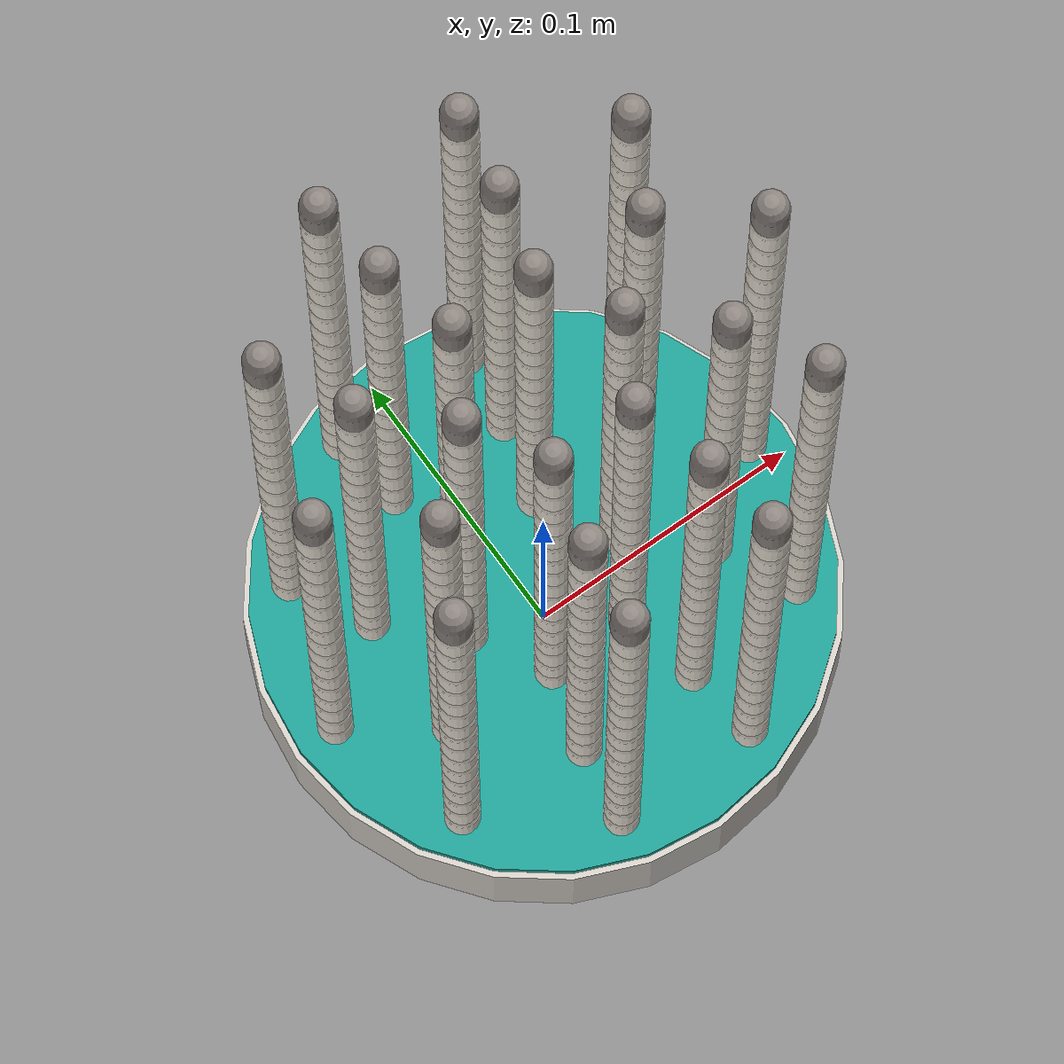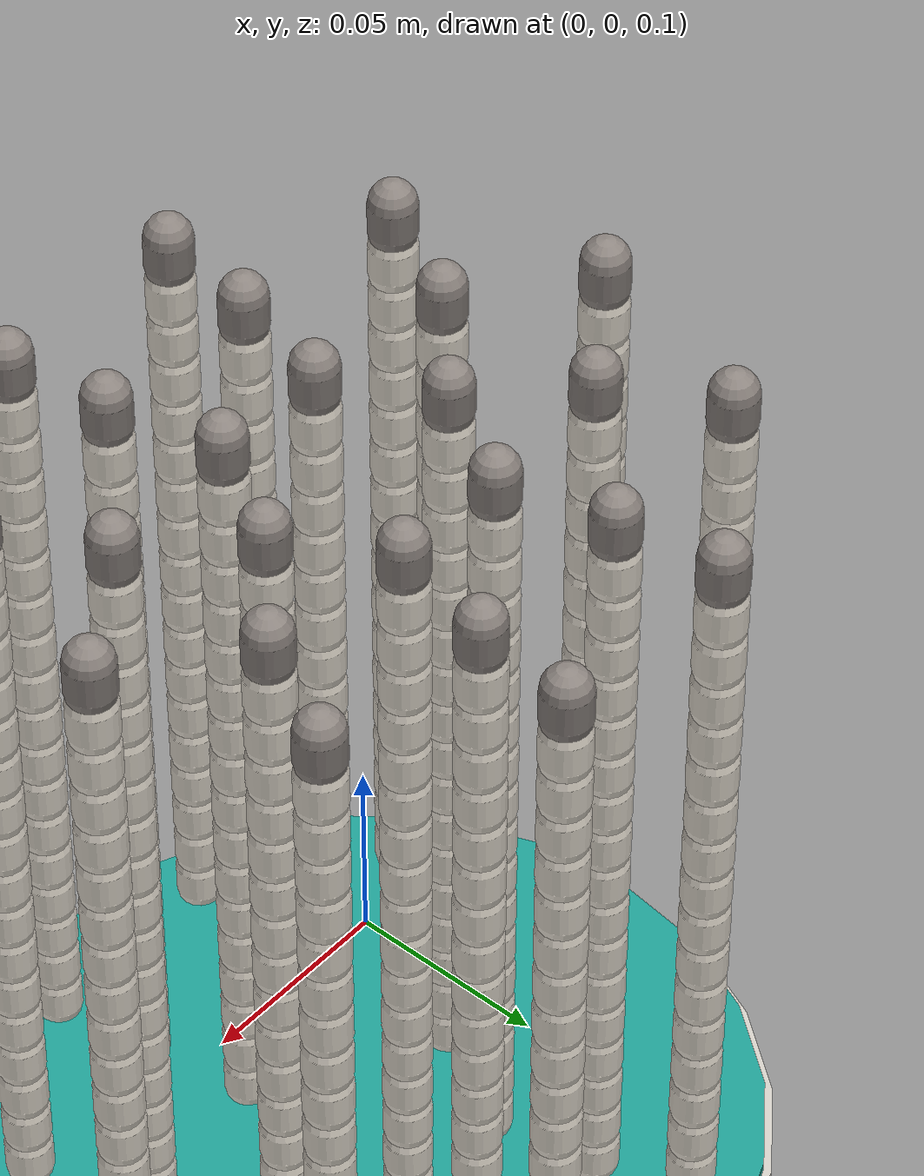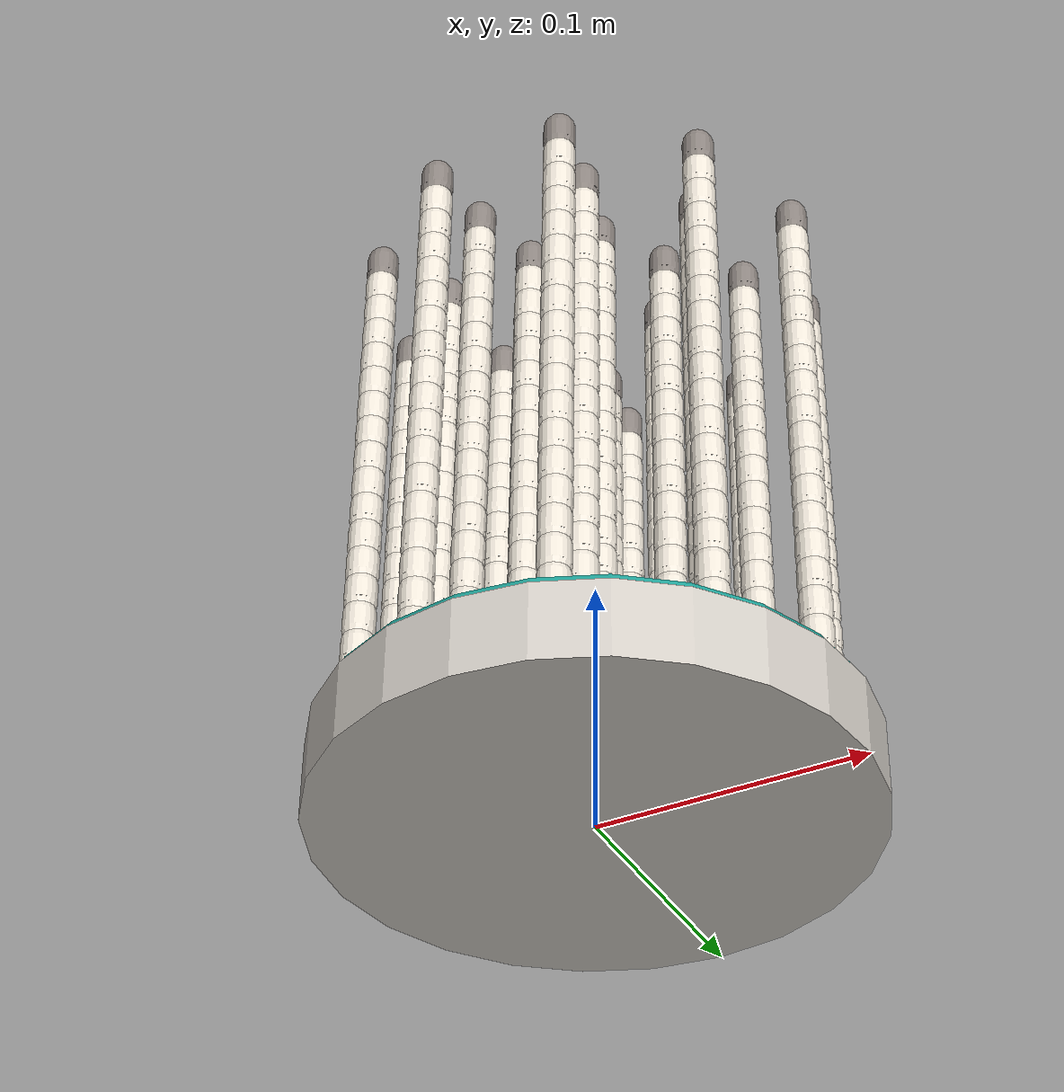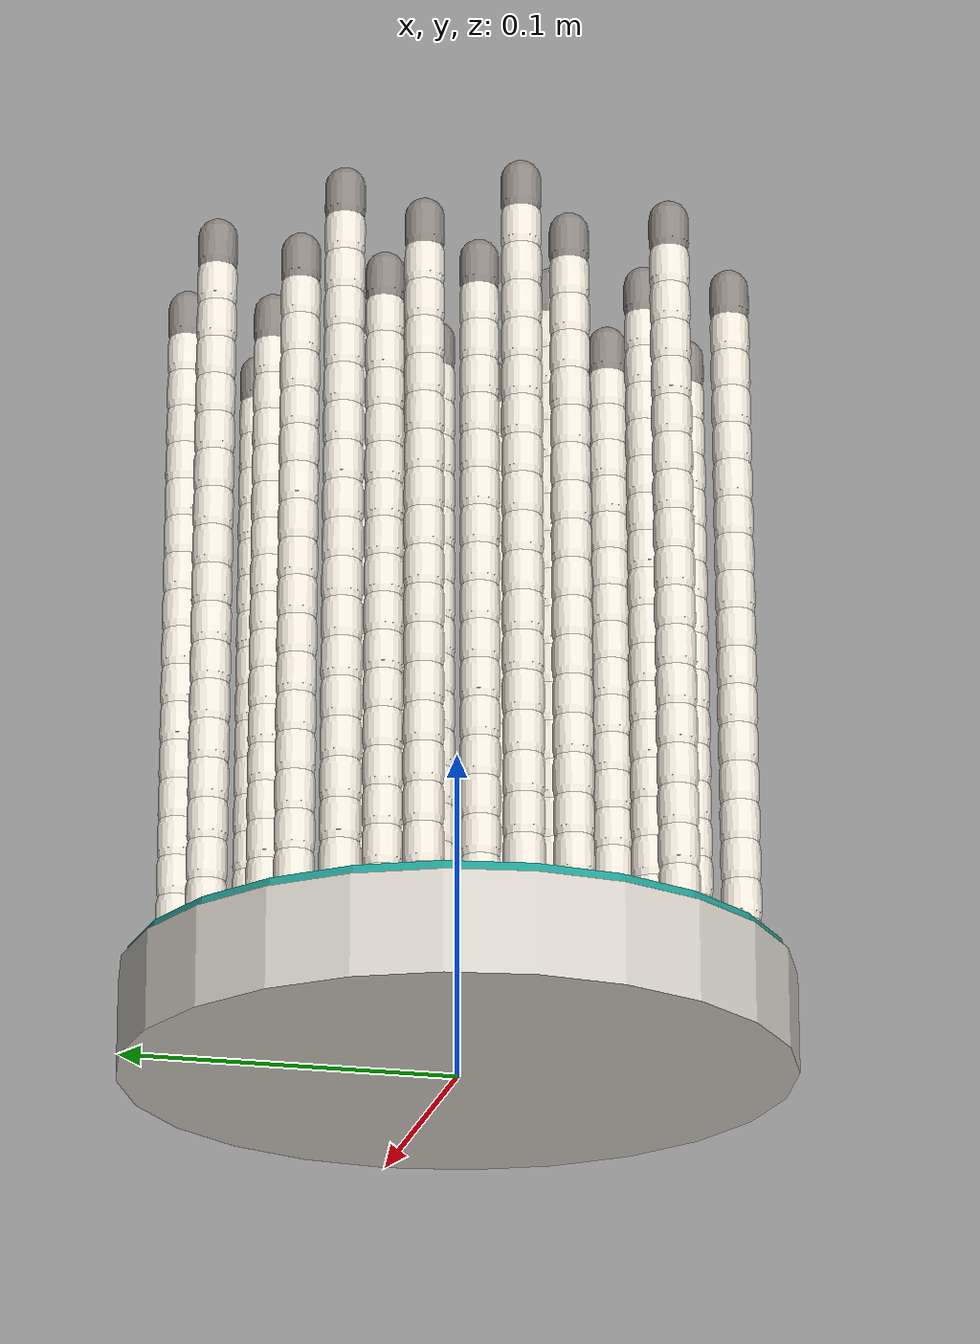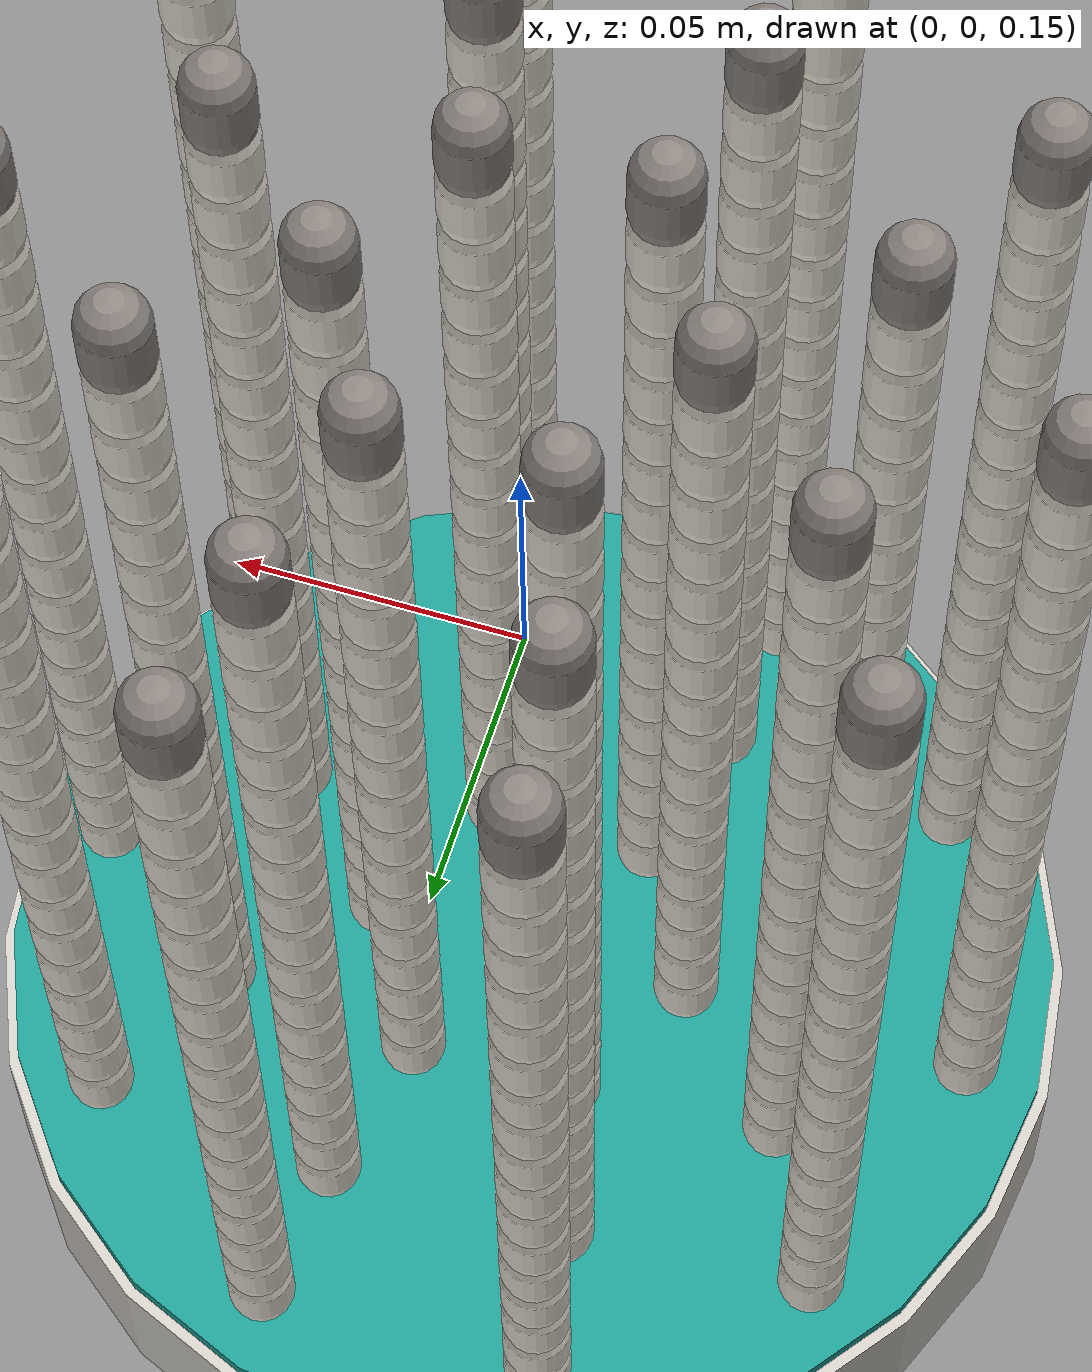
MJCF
<mujoco model="bundle24"><compiler angle="radian" autolimits="true"/>
<default><default class="tendril"><joint type="hinge" limited="true" range="-0.663 0.663" damping="0.01" stiffness="1.0" armature="1e-6"/>
<geom condim="4" contype="1" conaffinity="2" friction="0.9 0.02 0.001" solref="0.004 1" solimp="0.92 0.97 0.001"/><site size="0.0005" rgba="0 0 0 0"/>
<tendon width="0.0005" rgba="0.85 0.57 0.16 0"/><position kp="60000" kv="120" ctrllimited="true" ctrlrange="0 0.5" forcelimited="true" forcerange="-100.0 0"/></default></default>
<worldbody><body name="mount" childclass="tendril">
<geom name="disc" type="cylinder" size="0.1 0.015" pos="0 0 0.015" rgba="0.82 0.80 0.77 1" mass="0.6"/>
<geom type="cylinder" size="0.098 0.002" pos="0 0 0.031" rgba="0.12 0.62 0.58 1" contype="0" conaffinity="0" mass="0.001"/>
<site name="t0_b_c0" pos="0.03420 0.00000 0.03"/>
<site name="t0_b_c1" pos="0.02790 0.00364 0.03"/>
<site name="t0_b_c2" pos="0.02790 -0.00364 0.03"/>
<site name="t1_b_c0" pos="0.01920 0.02598 0.03"/>
<site name="t1_b_c1" pos="0.01290 0.02962 0.03"/>
<site name="t1_b_c2" pos="0.01290 0.02234 0.03"/>
<site name="t2_b_c0" pos="-0.01080 0.02598 0.03"/>
<site name="t2_b_c1" pos="-0.01710 0.02962 0.03"/>
<site name="t2_b_c2" pos="-0.01710 0.02234 0.03"/>
<site name="t3_b_c0" pos="-0.02580 0.00000 0.03"/>
<site name="t3_b_c1" pos="-0.03210 0.00364 0.03"/>
<site name="t3_b_c2" pos="-0.03210 -0.00364 0.03"/>
<site name="t4_b_c0" pos="-0.01080 -0.02598 0.03"/>
<site name="t4_b_c1" pos="-0.01710 -0.02234 0.03"/>
<site name="t4_b_c2" pos="-0.01710 -0.02962 0.03"/>
<site name="t5_b_c0" pos="0.01920 -0.02598 0.03"/>
<site name="t5_b_c1" pos="0.01290 -0.02234 0.03"/>
<site name="t5_b_c2" pos="0.01290 -0.02962 0.03"/>
<site name="t6_b_c0" pos="0.05779 0.02220 0.03"/>
<site name="t6_b_c1" pos="0.05149 0.02583 0.03"/>
<site name="t6_b_c2" pos="0.05149 0.01856 0.03"/>
<site name="t7_b_c0" pos="0.02640 0.05359 0.03"/>
<site name="t7_b_c1" pos="0.02010 0.05722 0.03"/>
<site name="t7_b_c2" pos="0.02010 0.04995 0.03"/>
<site name="t8_b_c0" pos="-0.01800 0.05359 0.03"/>
<site name="t8_b_c1" pos="-0.02430 0.05722 0.03"/>
<site name="t8_b_c2" pos="-0.02430 0.04995 0.03"/>
<site name="t9_b_c0" pos="-0.04939 0.02220 0.03"/>
<site name="t9_b_c1" pos="-0.05569 0.02583 0.03"/>
<site name="t9_b_c2" pos="-0.05569 0.01856 0.03"/>
<site name="t10_b_c0" pos="-0.04939 -0.02220 0.03"/>
<site name="t10_b_c1" pos="-0.05569 -0.01856 0.03"/>
<site name="t10_b_c2" pos="-0.05569 -0.02583 0.03"/>
<site name="t11_b_c0" pos="-0.01800 -0.05359 0.03"/>
<site name="t11_b_c1" pos="-0.02430 -0.04995 0.03"/>
<site name="t11_b_c2" pos="-0.02430 -0.05722 0.03"/>
<site name="t12_b_c0" pos="0.02640 -0.05359 0.03"/>
<site name="t12_b_c1" pos="0.02010 -0.04995 0.03"/>
<site name="t12_b_c2" pos="0.02010 -0.05722 0.03"/>
<site name="t13_b_c0" pos="0.05779 -0.02220 0.03"/>
<site name="t13_b_c1" pos="0.05149 -0.01856 0.03"/>
<site name="t13_b_c2" pos="0.05149 -0.02583 0.03"/>
<site name="t14_b_c0" pos="0.08820 0.00000 0.03"/>
<site name="t14_b_c1" pos="0.08190 0.00364 0.03"/>
<site name="t14_b_c2" pos="0.08190 -0.00364 0.03"/>
<site name="t15_b_c0" pos="0.07216 0.04937 0.03"/>
<site name="t15_b_c1" pos="0.06586 0.05301 0.03"/>
<site name="t15_b_c2" pos="0.06586 0.04574 0.03"/>
<site name="t16_b_c0" pos="0.03016 0.07989 0.03"/>
<site name="t16_b_c1" pos="0.02386 0.08353 0.03"/>
<site name="t16_b_c2" pos="0.02386 0.07625 0.03"/>
<site name="t17_b_c0" pos="-0.02176 0.07989 0.03"/>
<site name="t17_b_c1" pos="-0.02806 0.08353 0.03"/>
<site name="t17_b_c2" pos="-0.02806 0.07625 0.03"/>
<site name="t18_b_c0" pos="-0.06376 0.04937 0.03"/>
<site name="t18_b_c1" pos="-0.07006 0.05301 0.03"/>
<site name="t18_b_c2" pos="-0.07006 0.04574 0.03"/>
<site name="t19_b_c0" pos="-0.07980 0.00000 0.03"/>
<site name="t19_b_c1" pos="-0.08610 0.00364 0.03"/>
<site name="t19_b_c2" pos="-0.08610 -0.00364 0.03"/>
<site name="t20_b_c0" pos="-0.06376 -0.04937 0.03"/>
<site name="t20_b_c1" pos="-0.07006 -0.04574 0.03"/>
<site name="t20_b_c2" pos="-0.07006 -0.05301 0.03"/>
<site name="t21_b_c0" pos="-0.02176 -0.07989 0.03"/>
<site name="t21_b_c1" pos="-0.02806 -0.07625 0.03"/>
<site name="t21_b_c2" pos="-0.02806 -0.08353 0.03"/>
<site name="t22_b_c0" pos="0.03016 -0.07989 0.03"/>
<site name="t22_b_c1" pos="0.02386 -0.07625 0.03"/>
<site name="t22_b_c2" pos="0.02386 -0.08353 0.03"/>
<site name="t23_b_c0" pos="0.07216 -0.04937 0.03"/>
<site name="t23_b_c1" pos="0.06586 -0.04574 0.03"/>
<site name="t23_b_c2" pos="0.06586 -0.05301 0.03"/>
<body name="t0_v0" pos="0.03000 0.00000 0.033">
<joint name="t0_v0_x" axis="1 0 0"/><joint name="t0_v0_y" axis="0 1 0"/>
<geom name="t0_g0" type="capsule" size="0.006 0.00400" pos="0 0 0.0061" mass="0.0015" rgba="0.93 0.90 0.85 1"/>
<site name="t0_v0_c0" pos="0.00420 0.00000 0.0061"/>
<site name="t0_v0_c1" pos="-0.00210 0.00364 0.0061"/>
<site name="t0_v0_c2" pos="-0.00210 -0.00364 0.0061"/>
<body name="t0_v1" pos="0 0 0.0122">
<joint name="t0_v1_x" axis="1 0 0"/><joint name="t0_v1_y" axis="0 1 0"/>
<geom name="t0_g1" type="capsule" size="0.006 0.00400" pos="0 0 0.0061" mass="0.0015" rgba="0.93 0.90 0.85 1"/>
<site name="t0_v1_c0" pos="0.00420 0.00000 0.0061"/>
<site name="t0_v1_c1" pos="-0.00210 0.00364 0.0061"/>
<site name="t0_v1_c2" pos="-0.00210 -0.00364 0.0061"/>
<body name="t0_v2" pos="0 0 0.0122">
<joint name="t0_v2_x" axis="1 0 0"/><joint name="t0_v2_y" axis="0 1 0"/>
<geom name="t0_g2" type="capsule" size="0.006 0.00400" pos="0 0 0.0061" mass="0.0015" rgba="0.93 0.90 0.85 1"/>
<site name="t0_v2_c0" pos="0.00420 0.00000 0.0061"/>
<site name="t0_v2_c1" pos="-0.00210 0.00364 0.0061"/>
<site name="t0_v2_c2" pos="-0.00210 -0.00364 0.0061"/>
<body name="t0_v3" pos="0 0 0.0122">
<joint name="t0_v3_x" axis="1 0 0"/><joint name="t0_v3_y" axis="0 1 0"/>
<geom name="t0_g3" type="capsule" size="0.006 0.00400" pos="0 0 0.0061" mass="0.0015" rgba="0.93 0.90 0.85 1"/>
<site name="t0_v3_c0" pos="0.00420 0.00000 0.0061"/>
<site name="t0_v3_c1" pos="-0.00210 0.00364 0.0061"/>
<site name="t0_v3_c2" pos="-0.00210 -0.00364 0.0061"/>
<body name="t0_v4" pos="0 0 0.0122">
<joint name="t0_v4_x" axis="1 0 0"/><joint name="t0_v4_y" axis="0 1 0"/>
<geom name="t0_g4" type="capsule" size="0.006 0.00400" pos="0 0 0.0061" mass="0.0015" rgba="0.93 0.90 0.85 1"/>
<site name="t0_v4_c0" pos="0.00420 0.00000 0.0061"/>
<site name="t0_v4_c1" pos="-0.00210 0.00364 0.0061"/>
<site name="t0_v4_c2" pos="-0.00210 -0.00364 0.0061"/>
<body name="t0_v5" pos="0 0 0.0122">
<joint name="t0_v5_x" axis="1 0 0"/><joint name="t0_v5_y" axis="0 1 0"/>
<geom name="t0_g5" type="capsule" size="0.006 0.00400" pos="0 0 0.0061" mass="0.0015" rgba="0.93 0.90 0.85 1"/>
<site name="t0_v5_c0" pos="0.00420 0.00000 0.0061"/>
<site name="t0_v5_c1" pos="-0.00210 0.00364 0.0061"/>
<site name="t0_v5_c2" pos="-0.00210 -0.00364 0.0061"/>
<body name="t0_v6" pos="0 0 0.0122">
<joint name="t0_v6_x" axis="1 0 0"/><joint name="t0_v6_y" axis="0 1 0"/>
<geom name="t0_g6" type="capsule" size="0.006 0.00400" pos="0 0 0.0061" mass="0.0015" rgba="0.93 0.90 0.85 1"/>
<site name="t0_v6_c0" pos="0.00420 0.00000 0.0061"/>
<site name="t0_v6_c1" pos="-0.00210 0.00364 0.0061"/>
<site name="t0_v6_c2" pos="-0.00210 -0.00364 0.0061"/>
<body name="t0_v7" pos="0 0 0.0122">
<joint name="t0_v7_x" axis="1 0 0"/><joint name="t0_v7_y" axis="0 1 0"/>
<geom name="t0_g7" type="capsule" size="0.006 0.00400" pos="0 0 0.0061" mass="0.0015" rgba="0.93 0.90 0.85 1"/>
<site name="t0_v7_c0" pos="0.00420 0.00000 0.0061"/>
<site name="t0_v7_c1" pos="-0.00210 0.00364 0.0061"/>
<site name="t0_v7_c2" pos="-0.00210 -0.00364 0.0061"/>
<body name="t0_v8" pos="0 0 0.0122">
<joint name="t0_v8_x" axis="1 0 0"/><joint name="t0_v8_y" axis="0 1 0"/>
<geom name="t0_g8" type="capsule" size="0.006 0.00400" pos="0 0 0.0061" mass="0.0015" rgba="0.93 0.90 0.85 1"/>
<site name="t0_v8_c0" pos="0.00420 0.00000 0.0061"/>
<site name="t0_v8_c1" pos="-0.00210 0.00364 0.0061"/>
<site name="t0_v8_c2" pos="-0.00210 -0.00364 0.0061"/>
<body name="t0_v9" pos="0 0 0.0122">
<joint name="t0_v9_x" axis="1 0 0"/><joint name="t0_v9_y" axis="0 1 0"/>
<geom name="t0_g9" type="capsule" size="0.006 0.00400" pos="0 0 0.0061" mass="0.0015" rgba="0.93 0.90 0.85 1"/>
<site name="t0_v9_c0" pos="0.00420 0.00000 0.0061"/>
<site name="t0_v9_c1" pos="-0.00210 0.00364 0.0061"/>
<site name="t0_v9_c2" pos="-0.00210 -0.00364 0.0061"/>
<body name="t0_v10" pos="0 0 0.0122">
<joint name="t0_v10_x" axis="1 0 0"/><joint name="t0_v10_y" axis="0 1 0"/>
<geom name="t0_g10" type="capsule" size="0.006 0.00400" pos="0 0 0.0061" mass="0.0015" rgba="0.93 0.90 0.85 1"/>
<site name="t0_v10_c0" pos="0.00420 0.00000 0.0061"/>
<site name="t0_v10_c1" pos="-0.00210 0.00364 0.0061"/>
<site name="t0_v10_c2" pos="-0.00210 -0.00364 0.0061"/>
<body name="t0_v11" pos="0 0 0.0122">
<joint name="t0_v11_x" axis="1 0 0"/><joint name="t0_v11_y" axis="0 1 0"/>
<geom name="t0_g11" type="capsule" size="0.006 0.00400" pos="0 0 0.0061" mass="0.0015" rgba="0.93 0.90 0.85 1"/>
<site name="t0_v11_c0" pos="0.00420 0.00000 0.0061"/>
<site name="t0_v11_c1" pos="-0.00210 0.00364 0.0061"/>
<site name="t0_v11_c2" pos="-0.00210 -0.00364 0.0061"/>
<body name="t0_v12" pos="0 0 0.0122">
<joint name="t0_v12_x" axis="1 0 0"/><joint name="t0_v12_y" axis="0 1 0"/>
<geom name="t0_g12" type="capsule" size="0.006 0.00400" pos="0 0 0.0061" mass="0.0015" rgba="0.93 0.90 0.85 1"/>
<site name="t0_v12_c0" pos="0.00420 0.00000 0.0061"/>
<site name="t0_v12_c1" pos="-0.00210 0.00364 0.0061"/>
<site name="t0_v12_c2" pos="-0.00210 -0.00364 0.0061"/>
<body name="t0_v13" pos="0 0 0.0122">
<joint name="t0_v13_x" axis="1 0 0"/><joint name="t0_v13_y" axis="0 1 0"/>
<geom name="t0_g13" type="capsule" size="0.006 0.00400" pos="0 0 0.0061" mass="0.0015" rgba="0.93 0.90 0.85 1"/>
<site name="t0_v13_c0" pos="0.00420 0.00000 0.0061"/>
<site name="t0_v13_c1" pos="-0.00210 0.00364 0.0061"/>
<site name="t0_v13_c2" pos="-0.00210 -0.00364 0.0061"/>
<body name="t0_v14" pos="0 0 0.0122">
<joint name="t0_v14_x" axis="1 0 0"/><joint name="t0_v14_y" axis="0 1 0"/>
<geom name="t0_g14" type="capsule" size="0.006 0.00400" pos="0 0 0.0061" mass="0.0015" rgba="0.93 0.90 0.85 1"/>
<site name="t0_v14_c0" pos="0.00420 0.00000 0.0061"/>
<site name="t0_v14_c1" pos="-0.00210 0.00364 0.0061"/>
<site name="t0_v14_c2" pos="-0.00210 -0.00364 0.0061"/>
<body name="t0_v15" pos="0 0 0.0122">
<joint name="t0_v15_x" axis="1 0 0"/><joint name="t0_v15_y" axis="0 1 0"/>
<geom name="t0_g15" type="capsule" size="0.006 0.00400" pos="0 0 0.0061" mass="0.0015" rgba="0.93 0.90 0.85 1"/>
<site name="t0_v15_c0" pos="0.00420 0.00000 0.0061"/>
<site name="t0_v15_c1" pos="-0.00210 0.00364 0.0061"/>
<site name="t0_v15_c2" pos="-0.00210 -0.00364 0.0061"/>
<body name="t0_v16" pos="0 0 0.0122">
<joint name="t0_v16_x" axis="1 0 0"/><joint name="t0_v16_y" axis="0 1 0"/>
<geom name="t0_g16" type="capsule" size="0.006 0.00400" pos="0 0 0.0061" mass="0.0015" rgba="0.93 0.90 0.85 1"/>
<site name="t0_v16_c0" pos="0.00420 0.00000 0.0061"/>
<site name="t0_v16_c1" pos="-0.00210 0.00364 0.0061"/>
<site name="t0_v16_c2" pos="-0.00210 -0.00364 0.0061"/>
<body name="t0_v17" pos="0 0 0.0122">
<joint name="t0_v17_x" axis="1 0 0"/><joint name="t0_v17_y" axis="0 1 0"/>
<geom name="t0_g17" type="capsule" size="0.006 0.00400" pos="0 0 0.0061" mass="0.0015" rgba="0.55 0.52 0.50 1"/>
<site name="t0_v17_c0" pos="0.00420 0.00000 0.0061"/>
<site name="t0_v17_c1" pos="-0.00210 0.00364 0.0061"/>
<site name="t0_v17_c2" pos="-0.00210 -0.00364 0.0061"/>
</body></body></body></body></body></body></body></body></body></body></body></body></body></body></body></body></body></body>
<body name="t1_v0" pos="0.01500 0.02598 0.033">
<joint name="t1_v0_x" axis="1 0 0"/><joint name="t1_v0_y" axis="0 1 0"/>
<geom name="t1_g0" type="capsule" size="0.006 0.00400" pos="0 0 0.0061" mass="0.0015" rgba="0.93 0.90 0.85 1"/>
<site name="t1_v0_c0" pos="0.00420 0.00000 0.0061"/>
<site name="t1_v0_c1" pos="-0.00210 0.00364 0.0061"/>
<site name="t1_v0_c2" pos="-0.00210 -0.00364 0.0061"/>
<body name="t1_v1" pos="0 0 0.0122">
<joint name="t1_v1_x" axis="1 0 0"/><joint name="t1_v1_y" axis="0 1 0"/>
<geom name="t1_g1" type="capsule" size="0.006 0.00400" pos="0 0 0.0061" mass="0.0015" rgba="0.93 0.90 0.85 1"/>
<site name="t1_v1_c0" pos="0.00420 0.00000 0.0061"/>
<site name="t1_v1_c1" pos="-0.00210 0.00364 0.0061"/>
<site name="t1_v1_c2" pos="-0.00210 -0.00364 0.0061"/>
<body name="t1_v2" pos="0 0 0.0122">
<joint name="t1_v2_x" axis="1 0 0"/><joint name="t1_v2_y" axis="0 1 0"/>
<geom name="t1_g2" type="capsule" size="0.006 0.00400" pos="0 0 0.0061" mass="0.0015" rgba="0.93 0.90 0.85 1"/>
<site name="t1_v2_c0" pos="0.00420 0.00000 0.0061"/>
<site name="t1_v2_c1" pos="-0.00210 0.00364 0.0061"/>
<site name="t1_v2_c2" pos="-0.00210 -0.00364 0.0061"/>
<body name="t1_v3" pos="0 0 0.0122">
<joint name="t1_v3_x" axis="1 0 0"/><joint name="t1_v3_y" axis="0 1 0"/>
<geom name="t1_g3" type="capsule" size="0.006 0.00400" pos="0 0 0.0061" mass="0.0015" rgba="0.93 0.90 0.85 1"/>
<site name="t1_v3_c0" pos="0.00420 0.00000 0.0061"/>
<site name="t1_v3_c1" pos="-0.00210 0.00364 0.0061"/>
<site name="t1_v3_c2" pos="-0.00210 -0.00364 0.0061"/>
<body name="t1_v4" pos="0 0 0.0122">
<joint name="t1_v4_x" axis="1 0 0"/><joint name="t1_v4_y" axis="0 1 0"/>
<geom name="t1_g4" type="capsule" size="0.006 0.00400" pos="0 0 0.0061" mass="0.0015" rgba="0.93 0.90 0.85 1"/>
<site name="t1_v4_c0" pos="0.00420 0.00000 0.0061"/>
<site name="t1_v4_c1" pos="-0.00210 0.00364 0.0061"/>
<site name="t1_v4_c2" pos="-0.00210 -0.00364 0.0061"/>
<body name="t1_v5" pos="0 0 0.0122">
<joint name="t1_v5_x" axis="1 0 0"/><joint name="t1_v5_y" axis="0 1 0"/>
<geom name="t1_g5" type="capsule" size="0.006 0.00400" pos="0 0 0.0061" mass="0.0015" rgba="0.93 0.90 0.85 1"/>
<site name="t1_v5_c0" pos="0.00420 0.00000 0.0061"/>
<site name="t1_v5_c1" pos="-0.00210 0.00364 0.0061"/>
<site name="t1_v5_c2" pos="-0.00210 -0.00364 0.0061"/>
<body name="t1_v6" pos="0 0 0.0122">
<joint name="t1_v6_x" axis="1 0 0"/><joint name="t1_v6_y" axis="0 1 0"/>
<geom name="t1_g6" type="capsule" size="0.006 0.00400" pos="0 0 0.0061" mass="0.0015" rgba="0.93 0.90 0.85 1"/>
<site name="t1_v6_c0" pos="0.00420 0.00000 0.0061"/>
<site name="t1_v6_c1" pos="-0.00210 0.00364 0.0061"/>
<site name="t1_v6_c2" pos="-0.00210 -0.00364 0.0061"/>
<body name="t1_v7" pos="0 0 0.0122">
<joint name="t1_v7_x" axis="1 0 0"/><joint name="t1_v7_y" axis="0 1 0"/>
<geom name="t1_g7" type="capsule" size="0.006 0.00400" pos="0 0 0.0061" mass="0.0015" rgba="0.93 0.90 0.85 1"/>
<site name="t1_v7_c0" pos="0.00420 0.00000 0.0061"/>
<site name="t1_v7_c1" pos="-0.00210 0.00364 0.0061"/>
<site name="t1_v7_c2" pos="-0.00210 -0.00364 0.0061"/>
<body name="t1_v8" pos="0 0 0.0122">
<joint name="t1_v8_x" axis="1 0 0"/><joint name="t1_v8_y" axis="0 1 0"/>
<geom name="t1_g8" type="capsule" size="0.006 0.00400" pos="0 0 0.0061" mass="0.0015" rgba="0.93 0.90 0.85 1"/>
<site name="t1_v8_c0" pos="0.00420 0.00000 0.0061"/>
<site name="t1_v8_c1" pos="-0.00210 0.00364 0.0061"/>
<site name="t1_v8_c2" pos="-0.00210 -0.00364 0.0061"/>
<body name="t1_v9" pos="0 0 0.0122">
<joint name="t1_v9_x" axis="1 0 0"/><joint name="t1_v9_y" axis="0 1 0"/>
<geom name="t1_g9" type="capsule" size="0.006 0.00400" pos="0 0 0.0061" mass="0.0015" rgba="0.93 0.90 0.85 1"/>
<site name="t1_v9_c0" pos="0.00420 0.00000 0.0061"/>
<site name="t1_v9_c1" pos="-0.00210 0.00364 0.0061"/>
<site name="t1_v9_c2" pos="-0.00210 -0.00364 0.0061"/>
<body name="t1_v10" pos="0 0 0.0122">
<joint name="t1_v10_x" axis="1 0 0"/><joint name="t1_v10_y" axis="0 1 0"/>
<geom name="t1_g10" type="capsule" size="0.006 0.00400" pos="0 0 0.0061" mass="0.0015" rgba="0.93 0.90 0.85 1"/>
<site name="t1_v10_c0" pos="0.00420 0.00000 0.0061"/>
<site name="t1_v10_c1" pos="-0.00210 0.00364 0.0061"/>
<site name="t1_v10_c2" pos="-0.00210 -0.00364 0.0061"/>
<body name="t1_v11" pos="0 0 0.0122">
<joint name="t1_v11_x" axis="1 0 0"/><joint name="t1_v11_y" axis="0 1 0"/>
<geom name="t1_g11" type="capsule" size="0.006 0.00400" pos="0 0 0.0061" mass="0.0015" rgba="0.93 0.90 0.85 1"/>
<site name="t1_v11_c0" pos="0.00420 0.00000 0.0061"/>
<site name="t1_v11_c1" pos="-0.00210 0.00364 0.0061"/>
<site name="t1_v11_c2" pos="-0.00210 -0.00364 0.0061"/>
<body name="t1_v12" pos="0 0 0.0122">
<joint name="t1_v12_x" axis="1 0 0"/><joint name="t1_v12_y" axis="0 1 0"/>
<geom name="t1_g12" type="capsule" size="0.006 0.00400" pos="0 0 0.0061" mass="0.0015" rgba="0.93 0.90 0.85 1"/>
<site name="t1_v12_c0" pos="0.00420 0.00000 0.0061"/>
<site name="t1_v12_c1" pos="-0.00210 0.00364 0.0061"/>
<site name="t1_v12_c2" pos="-0.00210 -0.00364 0.0061"/>
<body name="t1_v13" pos="0 0 0.0122">
<joint name="t1_v13_x" axis="1 0 0"/><joint name="t1_v13_y" axis="0 1 0"/>
<geom name="t1_g13" type="capsule" size="0.006 0.00400" pos="0 0 0.0061" mass="0.0015" rgba="0.93 0.90 0.85 1"/>
<site name="t1_v13_c0" pos="0.00420 0.00000 0.0061"/>
<site name="t1_v13_c1" pos="-0.00210 0.00364 0.0061"/>
<site name="t1_v13_c2" pos="-0.00210 -0.00364 0.0061"/>
<body name="t1_v14" pos="0 0 0.0122">
<joint name="t1_v14_x" axis="1 0 0"/><joint name="t1_v14_y" axis="0 1 0"/>
<geom name="t1_g14" type="capsule" size="0.006 0.00400" pos="0 0 0.0061" mass="0.0015" rgba="0.93 0.90 0.85 1"/>
<site name="t1_v14_c0" pos="0.00420 0.00000 0.0061"/>
<site name="t1_v14_c1" pos="-0.00210 0.00364 0.0061"/>
<site name="t1_v14_c2" pos="-0.00210 -0.00364 0.0061"/>
<body name="t1_v15" pos="0 0 0.0122">
<joint name="t1_v15_x" axis="1 0 0"/><joint name="t1_v15_y" axis="0 1 0"/>
<geom name="t1_g15" type="capsule" size="0.006 0.00400" pos="0 0 0.0061" mass="0.0015" rgba="0.93 0.90 0.85 1"/>
<site name="t1_v15_c0" pos="0.00420 0.00000 0.0061"/>
<site name="t1_v15_c1" pos="-0.00210 0.00364 0.0061"/>
<site name="t1_v15_c2" pos="-0.00210 -0.00364 0.0061"/>
<body name="t1_v16" pos="0 0 0.0122">
<joint name="t1_v16_x" axis="1 0 0"/><joint name="t1_v16_y" axis="0 1 0"/>
<geom name="t1_g16" type="capsule" size="0.006 0.00400" pos="0 0 0.0061" mass="0.0015" rgba="0.93 0.90 0.85 1"/>
<site name="t1_v16_c0" pos="0.00420 0.00000 0.0061"/>
<site name="t1_v16_c1" pos="-0.00210 0.00364 0.0061"/>
<site name="t1_v16_c2" pos="-0.00210 -0.00364 0.0061"/>
<body name="t1_v17" pos="0 0 0.0122">
<joint name="t1_v17_x" axis="1 0 0"/><joint name="t1_v17_y" axis="0 1 0"/>
<geom name="t1_g17" type="capsule" size="0.006 0.00400" pos="0 0 0.0061" mass="0.0015" rgba="0.55 0.52 0.50 1"/>
<site name="t1_v17_c0" pos="0.00420 0.00000 0.0061"/>
<site name="t1_v17_c1" pos="-0.00210 0.00364 0.0061"/>
<site name="t1_v17_c2" pos="-0.00210 -0.00364 0.0061"/>
</body></body></body></body></body></body></body></body></body></body></body></body></body></body></body></body></body></body>
<body name="t2_v0" pos="-0.01500 0.02598 0.033">
<joint name="t2_v0_x" axis="1 0 0"/><joint name="t2_v0_y" axis="0 1 0"/>
<geom name="t2_g0" type="capsule" size="0.006 0.00400" pos="0 0 0.0061" mass="0.0015" rgba="0.93 0.90 0.85 1"/>
<site name="t2_v0_c0" pos="0.00420 0.00000 0.0061"/>
<site name="t2_v0_c1" pos="-0.00210 0.00364 0.0061"/>
<site name="t2_v0_c2" pos="-0.00210 -0.00364 0.0061"/>
<body name="t2_v1" pos="0 0 0.0122">
<joint name="t2_v1_x" axis="1 0 0"/><joint name="t2_v1_y" axis="0 1 0"/>
<geom name="t2_g1" type="capsule" size="0.006 0.00400" pos="0 0 0.0061" mass="0.0015" rgba="0.93 0.90 0.85 1"/>
<site name="t2_v1_c0" pos="0.00420 0.00000 0.0061"/>
<site name="t2_v1_c1" pos="-0.00210 0.00364 0.0061"/>
<site name="t2_v1_c2" pos="-0.00210 -0.00364 0.0061"/>
<body name="t2_v2" pos="0 0 0.0122">
<joint name="t2_v2_x" axis="1 0 0"/><joint name="t2_v2_y" axis="0 1 0"/>
<geom name="t2_g2" type="capsule" size="0.006 0.00400" pos="0 0 0.0061" mass="0.0015" rgba="0.93 0.90 0.85 1"/>
<site name="t2_v2_c0" pos="0.00420 0.00000 0.0061"/>
<site name="t2_v2_c1" pos="-0.00210 0.00364 0.0061"/>
<site name="t2_v2_c2" pos="-0.00210 -0.00364 0.0061"/>
<body name="t2_v3" pos="0 0 0.0122">
<joint name="t2_v3_x" axis="1 0 0"/><joint name="t2_v3_y" axis="0 1 0"/>
<geom name="t2_g3" type="capsule" size="0.006 0.00400" pos="0 0 0.0061" mass="0.0015" rgba="0.93 0.90 0.85 1"/>
<site name="t2_v3_c0" pos="0.00420 0.00000 0.0061"/>
<site name="t2_v3_c1" pos="-0.00210 0.00364 0.0061"/>
<site name="t2_v3_c2" pos="-0.00210 -0.00364 0.0061"/>
<body name="t2_v4" pos="0 0 0.0122">
<joint name="t2_v4_x" axis="1 0 0"/><joint name="t2_v4_y" axis="0 1 0"/>
<geom name="t2_g4" type="capsule" size="0.006 0.00400" pos="0 0 0.0061" mass="0.0015" rgba="0.93 0.90 0.85 1"/>
<site name="t2_v4_c0" pos="0.00420 0.00000 0.0061"/>
<site name="t2_v4_c1" pos="-0.00210 0.00364 0.0061"/>
<site name="t2_v4_c2" pos="-0.00210 -0.00364 0.0061"/>
<body name="t2_v5" pos="0 0 0.0122">
<joint name="t2_v5_x" axis="1 0 0"/><joint name="t2_v5_y" axis="0 1 0"/>
<geom name="t2_g5" type="capsule" size="0.006 0.00400" pos="0 0 0.0061" mass="0.0015" rgba="0.93 0.90 0.85 1"/>
<site name="t2_v5_c0" pos="0.00420 0.00000 0.0061"/>
<site name="t2_v5_c1" pos="-0.00210 0.00364 0.0061"/>
<site name="t2_v5_c2" pos="-0.00210 -0.00364 0.0061"/>
<body name="t2_v6" pos="0 0 0.0122">
<joint name="t2_v6_x" axis="1 0 0"/><joint name="t2_v6_y" axis="0 1 0"/>
<geom name="t2_g6" type="capsule" size="0.006 0.00400" pos="0 0 0.0061" mass="0.0015" rgba="0.93 0.90 0.85 1"/>
<site name="t2_v6_c0" pos="0.00420 0.00000 0.0061"/>
<site name="t2_v6_c1" pos="-0.00210 0.00364 0.0061"/>
<site name="t2_v6_c2" pos="-0.00210 -0.00364 0.0061"/>
<body name="t2_v7" pos="0 0 0.0122">
<joint name="t2_v7_x" axis="1 0 0"/><joint name="t2_v7_y" axis="0 1 0"/>
<geom name="t2_g7" type="capsule" size="0.006 0.00400" pos="0 0 0.0061" mass="0.0015" rgba="0.93 0.90 0.85 1"/>
<site name="t2_v7_c0" pos="0.00420 0.00000 0.0061"/>
<site name="t2_v7_c1" pos="-0.00210 0.00364 0.0061"/>
<site name="t2_v7_c2" pos="-0.00210 -0.00364 0.0061"/>
<body name="t2_v8" pos="0 0 0.0122">
<joint name="t2_v8_x" axis="1 0 0"/><joint name="t2_v8_y" axis="0 1 0"/>
<geom name="t2_g8" type="capsule" size="0.006 0.00400" pos="0 0 0.0061" mass="0.0015" rgba="0.93 0.90 0.85 1"/>
<site name="t2_v8_c0" pos="0.00420 0.00000 0.0061"/>
<site name="t2_v8_c1" pos="-0.00210 0.00364 0.0061"/>
<site name="t2_v8_c2" pos="-0.00210 -0.00364 0.0061"/>
<body name="t2_v9" pos="0 0 0.0122">
<joint name="t2_v9_x" axis="1 0 0"/><joint name="t2_v9_y" axis="0 1 0"/>
<geom name="t2_g9" type="capsule" size="0.006 0.00400" pos="0 0 0.0061" mass="0.0015" rgba="0.93 0.90 0.85 1"/>
<site name="t2_v9_c0" pos="0.00420 0.00000 0.0061"/>
<site name="t2_v9_c1" pos="-0.00210 0.00364 0.0061"/>
<site name="t2_v9_c2" pos="-0.00210 -0.00364 0.0061"/>
<body name="t2_v10" pos="0 0 0.0122">
<joint name="t2_v10_x" axis="1 0 0"/><joint name="t2_v10_y" axis="0 1 0"/>
<geom name="t2_g10" type="capsule" size="0.006 0.00400" pos="0 0 0.0061" mass="0.0015" rgba="0.93 0.90 0.85 1"/>
<site name="t2_v10_c0" pos="0.00420 0.00000 0.0061"/>
<site name="t2_v10_c1" pos="-0.00210 0.00364 0.0061"/>
<site name="t2_v10_c2" pos="-0.00210 -0.00364 0.0061"/>
<body name="t2_v11" pos="0 0 0.0122">
<joint name="t2_v11_x" axis="1 0 0"/><joint name="t2_v11_y" axis="0 1 0"/>
<geom name="t2_g11" type="capsule" size="0.006 0.00400" pos="0 0 0.0061" mass="0.0015" rgba="0.93 0.90 0.85 1"/>
<site name="t2_v11_c0" pos="0.00420 0.00000 0.0061"/>
<site name="t2_v11_c1" pos="-0.00210 0.00364 0.0061"/>
<site name="t2_v11_c2" pos="-0.00210 -0.00364 0.0061"/>
<body name="t2_v12" pos="0 0 0.0122">
<joint name="t2_v12_x" axis="1 0 0"/><joint name="t2_v12_y" axis="0 1 0"/>
<geom name="t2_g12" type="capsule" size="0.006 0.00400" pos="0 0 0.0061" mass="0.0015" rgba="0.93 0.90 0.85 1"/>
<site name="t2_v12_c0" pos="0.00420 0.00000 0.0061"/>
<site name="t2_v12_c1" pos="-0.00210 0.00364 0.0061"/>
<site name="t2_v12_c2" pos="-0.00210 -0.00364 0.0061"/>
<body name="t2_v13" pos="0 0 0.0122">
<joint name="t2_v13_x" axis="1 0 0"/><joint name="t2_v13_y" axis="0 1 0"/>
<geom name="t2_g13" type="capsule" size="0.006 0.00400" pos="0 0 0.0061" mass="0.0015" rgba="0.93 0.90 0.85 1"/>
<site name="t2_v13_c0" pos="0.00420 0.00000 0.0061"/>
<site name="t2_v13_c1" pos="-0.00210 0.00364 0.0061"/>
<site name="t2_v13_c2" pos="-0.00210 -0.00364 0.0061"/>
<body name="t2_v14" pos="0 0 0.0122">
<joint name="t2_v14_x" axis="1 0 0"/><joint name="t2_v14_y" axis="0 1 0"/>
<geom name="t2_g14" type="capsule" size="0.006 0.00400" pos="0 0 0.0061" mass="0.0015" rgba="0.93 0.90 0.85 1"/>
<site name="t2_v14_c0" pos="0.00420 0.00000 0.0061"/>
<site name="t2_v14_c1" pos="-0.00210 0.00364 0.0061"/>
<site name="t2_v14_c2" pos="-0.00210 -0.00364 0.0061"/>
<body name="t2_v15" pos="0 0 0.0122">
<joint name="t2_v15_x" axis="1 0 0"/><joint name="t2_v15_y" axis="0 1 0"/>
<geom name="t2_g15" type="capsule" size="0.006 0.00400" pos="0 0 0.0061" mass="0.0015" rgba="0.93 0.90 0.85 1"/>
<site name="t2_v15_c0" pos="0.00420 0.00000 0.0061"/>
<site name="t2_v15_c1" pos="-0.00210 0.00364 0.0061"/>
<site name="t2_v15_c2" pos="-0.00210 -0.00364 0.0061"/>
<body name="t2_v16" pos="0 0 0.0122">
<joint name="t2_v16_x" axis="1 0 0"/><joint name="t2_v16_y" axis="0 1 0"/>
<geom name="t2_g16" type="capsule" size="0.006 0.00400" pos="0 0 0.0061" mass="0.0015" rgba="0.93 0.90 0.85 1"/>
<site name="t2_v16_c0" pos="0.00420 0.00000 0.0061"/>
<site name="t2_v16_c1" pos="-0.00210 0.00364 0.0061"/>
<site name="t2_v16_c2" pos="-0.00210 -0.00364 0.0061"/>
<body name="t2_v17" pos="0 0 0.0122">
<joint name="t2_v17_x" axis="1 0 0"/><joint name="t2_v17_y" axis="0 1 0"/>
<geom name="t2_g17" type="capsule" size="0.006 0.00400" pos="0 0 0.0061" mass="0.0015" rgba="0.55 0.52 0.50 1"/>
<site name="t2_v17_c0" pos="0.00420 0.00000 0.0061"/>
<site name="t2_v17_c1" pos="-0.00210 0.00364 0.0061"/>
<site name="t2_v17_c2" pos="-0.00210 -0.00364 0.0061"/>
</body></body></body></body></body></body></body></body></body></body></body></body></body></body></body></body></body></body>
<body name="t3_v0" pos="-0.03000 0.00000 0.033">
<joint name="t3_v0_x" axis="1 0 0"/><joint name="t3_v0_y" axis="0 1 0"/>
<geom name="t3_g0" type="capsule" size="0.006 0.00400" pos="0 0 0.0061" mass="0.0015" rgba="0.93 0.90 0.85 1"/>
<site name="t3_v0_c0" pos="0.00420 0.00000 0.0061"/>
<site name="t3_v0_c1" pos="-0.00210 0.00364 0.0061"/>
<site name="t3_v0_c2" pos="-0.00210 -0.00364 0.0061"/>
<body name="t3_v1" pos="0 0 0.0122">
<joint name="t3_v1_x" axis="1 0 0"/><joint name="t3_v1_y" axis="0 1 0"/>
<geom name="t3_g1" type="capsule" size="0.006 0.00400" pos="0 0 0.0061" mass="0.0015" rgba="0.93 0.90 0.85 1"/>
<site name="t3_v1_c0" pos="0.00420 0.00000 0.0061"/>
<site name="t3_v1_c1" pos="-0.00210 0.00364 0.0061"/>
<site name="t3_v1_c2" pos="-0.00210 -0.00364 0.0061"/>
<body name="t3_v2" pos="0 0 0.0122">
<joint name="t3_v2_x" axis="1 0 0"/><joint name="t3_v2_y" axis="0 1 0"/>
<geom name="t3_g2" type="capsule" size="0.006 0.00400" pos="0 0 0.0061" mass="0.0015" rgba="0.93 0.90 0.85 1"/>
<site name="t3_v2_c0" pos="0.00420 0.00000 0.0061"/>
<site name="t3_v2_c1" pos="-0.00210 0.00364 0.0061"/>
<site name="t3_v2_c2" pos="-0.00210 -0.00364 0.0061"/>
<body name="t3_v3" pos="0 0 0.0122">
<joint name="t3_v3_x" axis="1 0 0"/><joint name="t3_v3_y" axis="0 1 0"/>
<geom name="t3_g3" type="capsule" size="0.006 0.00400" pos="0 0 0.0061" mass="0.0015" rgba="0.93 0.90 0.85 1"/>
<site name="t3_v3_c0" pos="0.00420 0.00000 0.0061"/>
<site name="t3_v3_c1" pos="-0.00210 0.00364 0.0061"/>
<site name="t3_v3_c2" pos="-0.00210 -0.00364 0.0061"/>
<body name="t3_v4" pos="0 0 0.0122">
<joint name="t3_v4_x" axis="1 0 0"/><joint name="t3_v4_y" axis="0 1 0"/>
<geom name="t3_g4" type="capsule" size="0.006 0.00400" pos="0 0 0.0061" mass="0.0015" rgba="0.93 0.90 0.85 1"/>
<site name="t3_v4_c0" pos="0.00420 0.00000 0.0061"/>
<site name="t3_v4_c1" pos="-0.00210 0.00364 0.0061"/>
<site name="t3_v4_c2" pos="-0.00210 -0.00364 0.0061"/>
<body name="t3_v5" pos="0 0 0.0122">
<joint name="t3_v5_x" axis="1 0 0"/><joint name="t3_v5_y" axis="0 1 0"/>
<geom name="t3_g5" type="capsule" size="0.006 0.00400" pos="0 0 0.0061" mass="0.0015" rgba="0.93 0.90 0.85 1"/>
<site name="t3_v5_c0" pos="0.00420 0.00000 0.0061"/>
<site name="t3_v5_c1" pos="-0.00210 0.00364 0.0061"/>
<site name="t3_v5_c2" pos="-0.00210 -0.00364 0.0061"/>
<body name="t3_v6" pos="0 0 0.0122">
<joint name="t3_v6_x" axis="1 0 0"/><joint name="t3_v6_y" axis="0 1 0"/>
<geom name="t3_g6" type="capsule" size="0.006 0.00400" pos="0 0 0.0061" mass="0.0015" rgba="0.93 0.90 0.85 1"/>
<site name="t3_v6_c0" pos="0.00420 0.00000 0.0061"/>
<site name="t3_v6_c1" pos="-0.00210 0.00364 0.0061"/>
<site name="t3_v6_c2" pos="-0.00210 -0.00364 0.0061"/>
<body name="t3_v7" pos="0 0 0.0122">
<joint name="t3_v7_x" axis="1 0 0"/><joint name="t3_v7_y" axis="0 1 0"/>
<geom name="t3_g7" type="capsule" size="0.006 0.00400" pos="0 0 0.0061" mass="0.0015" rgba="0.93 0.90 0.85 1"/>
<site name="t3_v7_c0" pos="0.00420 0.00000 0.0061"/>
<site name="t3_v7_c1" pos="-0.00210 0.00364 0.0061"/>
<site name="t3_v7_c2" pos="-0.00210 -0.00364 0.0061"/>
<body name="t3_v8" pos="0 0 0.0122">
<joint name="t3_v8_x" axis="1 0 0"/><joint name="t3_v8_y" axis="0 1 0"/>
<geom name="t3_g8" type="capsule" size="0.006 0.00400" pos="0 0 0.0061" mass="0.0015" rgba="0.93 0.90 0.85 1"/>
<site name="t3_v8_c0" pos="0.00420 0.00000 0.0061"/>
<site name="t3_v8_c1" pos="-0.00210 0.00364 0.0061"/>
<site name="t3_v8_c2" pos="-0.00210 -0.00364 0.0061"/>
<body name="t3_v9" pos="0 0 0.0122">
<joint name="t3_v9_x" axis="1 0 0"/><joint name="t3_v9_y" axis="0 1 0"/>
<geom name="t3_g9" type="capsule" size="0.006 0.00400" pos="0 0 0.0061" mass="0.0015" rgba="0.93 0.90 0.85 1"/>
<site name="t3_v9_c0" pos="0.00420 0.00000 0.0061"/>
<site name="t3_v9_c1" pos="-0.00210 0.00364 0.0061"/>
<site name="t3_v9_c2" pos="-0.00210 -0.00364 0.0061"/>
<body name="t3_v10" pos="0 0 0.0122">
<joint name="t3_v10_x" axis="1 0 0"/><joint name="t3_v10_y" axis="0 1 0"/>
<geom name="t3_g10" type="capsule" size="0.006 0.00400" pos="0 0 0.0061" mass="0.0015" rgba="0.93 0.90 0.85 1"/>
<site name="t3_v10_c0" pos="0.00420 0.00000 0.0061"/>
<site name="t3_v10_c1" pos="-0.00210 0.00364 0.0061"/>
<site name="t3_v10_c2" pos="-0.00210 -0.00364 0.0061"/>
<body name="t3_v11" pos="0 0 0.0122">
<joint name="t3_v11_x" axis="1 0 0"/><joint name="t3_v11_y" axis="0 1 0"/>
<geom name="t3_g11" type="capsule" size="0.006 0.00400" pos="0 0 0.0061" mass="0.0015" rgba="0.93 0.90 0.85 1"/>
<site name="t3_v11_c0" pos="0.00420 0.00000 0.0061"/>
<site name="t3_v11_c1" pos="-0.00210 0.00364 0.0061"/>
<site name="t3_v11_c2" pos="-0.00210 -0.00364 0.0061"/>
<body name="t3_v12" pos="0 0 0.0122">
<joint name="t3_v12_x" axis="1 0 0"/><joint name="t3_v12_y" axis="0 1 0"/>
<geom name="t3_g12" type="capsule" size="0.006 0.00400" pos="0 0 0.0061" mass="0.0015" rgba="0.93 0.90 0.85 1"/>
<site name="t3_v12_c0" pos="0.00420 0.00000 0.0061"/>
<site name="t3_v12_c1" pos="-0.00210 0.00364 0.0061"/>
<site name="t3_v12_c2" pos="-0.00210 -0.00364 0.0061"/>
<body name="t3_v13" pos="0 0 0.0122">
<joint name="t3_v13_x" axis="1 0 0"/><joint name="t3_v13_y" axis="0 1 0"/>
<geom name="t3_g13" type="capsule" size="0.006 0.00400" pos="0 0 0.0061" mass="0.0015" rgba="0.93 0.90 0.85 1"/>
<site name="t3_v13_c0" pos="0.00420 0.00000 0.0061"/>
<site name="t3_v13_c1" pos="-0.00210 0.00364 0.0061"/>
<site name="t3_v13_c2" pos="-0.00210 -0.00364 0.0061"/>
<body name="t3_v14" pos="0 0 0.0122">
<joint name="t3_v14_x" axis="1 0 0"/><joint name="t3_v14_y" axis="0 1 0"/>
<geom name="t3_g14" type="capsule" size="0.006 0.00400" pos="0 0 0.0061" mass="0.0015" rgba="0.93 0.90 0.85 1"/>
<site name="t3_v14_c0" pos="0.00420 0.00000 0.0061"/>
<site name="t3_v14_c1" pos="-0.00210 0.00364 0.0061"/>
<site name="t3_v14_c2" pos="-0.00210 -0.00364 0.0061"/>
<body name="t3_v15" pos="0 0 0.0122">
<joint name="t3_v15_x" axis="1 0 0"/><joint name="t3_v15_y" axis="0 1 0"/>
<geom name="t3_g15" type="capsule" size="0.006 0.00400" pos="0 0 0.0061" mass="0.0015" rgba="0.93 0.90 0.85 1"/>
<site name="t3_v15_c0" pos="0.00420 0.00000 0.0061"/>
<site name="t3_v15_c1" pos="-0.00210 0.00364 0.0061"/>
<site name="t3_v15_c2" pos="-0.00210 -0.00364 0.0061"/>
<body name="t3_v16" pos="0 0 0.0122">
<joint name="t3_v16_x" axis="1 0 0"/><joint name="t3_v16_y" axis="0 1 0"/>
<geom name="t3_g16" type="capsule" size="0.006 0.00400" pos="0 0 0.0061" mass="0.0015" rgba="0.93 0.90 0.85 1"/>
<site name="t3_v16_c0" pos="0.00420 0.00000 0.0061"/>
<site name="t3_v16_c1" pos="-0.00210 0.00364 0.0061"/>
<site name="t3_v16_c2" pos="-0.00210 -0.00364 0.0061"/>
<body name="t3_v17" pos="0 0 0.0122">
<joint name="t3_v17_x" axis="1 0 0"/><joint name="t3_v17_y" axis="0 1 0"/>
<geom name="t3_g17" type="capsule" size="0.006 0.00400" pos="0 0 0.0061" mass="0.0015" rgba="0.55 0.52 0.50 1"/>
<site name="t3_v17_c0" pos="0.00420 0.00000 0.0061"/>
<site name="t3_v17_c1" pos="-0.00210 0.00364 0.0061"/>
<site name="t3_v17_c2" pos="-0.00210 -0.00364 0.0061"/>
</body></body></body></body></body></body></body></body></body></body></body></body></body></body></body></body></body></body>
<body name="t4_v0" pos="-0.01500 -0.02598 0.033">
<joint name="t4_v0_x" axis="1 0 0"/><joint name="t4_v0_y" axis="0 1 0"/>
<geom name="t4_g0" type="capsule" size="0.006 0.00400" pos="0 0 0.0061" mass="0.0015" rgba="0.93 0.90 0.85 1"/>
<site name="t4_v0_c0" pos="0.00420 0.00000 0.0061"/>
<site name="t4_v0_c1" pos="-0.00210 0.00364 0.0061"/>
<site name="t4_v0_c2" pos="-0.00210 -0.00364 0.0061"/>
<body name="t4_v1" pos="0 0 0.0122">
<joint name="t4_v1_x" axis="1 0 0"/><joint name="t4_v1_y" axis="0 1 0"/>
<geom name="t4_g1" type="capsule" size="0.006 0.00400" pos="0 0 0.0061" mass="0.0015" rgba="0.93 0.90 0.85 1"/>
<site name="t4_v1_c0" pos="0.00420 0.00000 0.0061"/>
<site name="t4_v1_c1" pos="-0.00210 0.00364 0.0061"/>
<site name="t4_v1_c2" pos="-0.00210 -0.00364 0.0061"/>
<body name="t4_v2" pos="0 0 0.0122">
<joint name="t4_v2_x" axis="1 0 0"/><joint name="t4_v2_y" axis="0 1 0"/>
<geom name="t4_g2" type="capsule" size="0.006 0.00400" pos="0 0 0.0061" mass="0.0015" rgba="0.93 0.90 0.85 1"/>
<site name="t4_v2_c0" pos="0.00420 0.00000 0.0061"/>
<site name="t4_v2_c1" pos="-0.00210 0.00364 0.0061"/>
<site name="t4_v2_c2" pos="-0.00210 -0.00364 0.0061"/>
<body name="t4_v3" pos="0 0 0.0122">
<joint name="t4_v3_x" axis="1 0 0"/><joint name="t4_v3_y" axis="0 1 0"/>
<geom name="t4_g3" type="capsule" size="0.006 0.00400" pos="0 0 0.0061" mass="0.0015" rgba="0.93 0.90 0.85 1"/>
<site name="t4_v3_c0" pos="0.00420 0.00000 0.0061"/>
<site name="t4_v3_c1" pos="-0.00210 0.00364 0.0061"/>
<site name="t4_v3_c2" pos="-0.00210 -0.00364 0.0061"/>
<body name="t4_v4" pos="0 0 0.0122">
<joint name="t4_v4_x" axis="1 0 0"/><joint name="t4_v4_y" axis="0 1 0"/>
<geom name="t4_g4" type="capsule" size="0.006 0.00400" pos="0 0 0.0061" mass="0.0015" rgba="0.93 0.90 0.85 1"/>
<site name="t4_v4_c0" pos="0.00420 0.00000 0.0061"/>
<site name="t4_v4_c1" pos="-0.00210 0.00364 0.0061"/>
<site name="t4_v4_c2" pos="-0.00210 -0.00364 0.0061"/>
<body name="t4_v5" pos="0 0 0.0122">
<joint name="t4_v5_x" axis="1 0 0"/><joint name="t4_v5_y" axis="0 1 0"/>
<geom name="t4_g5" type="capsule" size="0.006 0.00400" pos="0 0 0.0061" mass="0.0015" rgba="0.93 0.90 0.85 1"/>
<site name="t4_v5_c0" pos="0.00420 0.00000 0.0061"/>
<site name="t4_v5_c1" pos="-0.00210 0.00364 0.0061"/>
<site name="t4_v5_c2" pos="-0.00210 -0.00364 0.0061"/>
<body name="t4_v6" pos="0 0 0.0122">
<joint name="t4_v6_x" axis="1 0 0"/><joint name="t4_v6_y" axis="0 1 0"/>
<geom name="t4_g6" type="capsule" size="0.006 0.00400" pos="0 0 0.0061" mass="0.0015" rgba="0.93 0.90 0.85 1"/>
<site name="t4_v6_c0" pos="0.00420 0.00000 0.0061"/>
<site name="t4_v6_c1" pos="-0.00210 0.00364 0.0061"/>
<site name="t4_v6_c2" pos="-0.00210 -0.00364 0.0061"/>
<body name="t4_v7" pos="0 0 0.0122">
<joint name="t4_v7_x" axis="1 0 0"/><joint name="t4_v7_y" axis="0 1 0"/>
<geom name="t4_g7" type="capsule" size="0.006 0.00400" pos="0 0 0.0061" mass="0.0015" rgba="0.93 0.90 0.85 1"/>
<site name="t4_v7_c0" pos="0.00420 0.00000 0.0061"/>
<site name="t4_v7_c1" pos="-0.00210 0.00364 0.0061"/>
<site name="t4_v7_c2" pos="-0.00210 -0.00364 0.0061"/>
<body name="t4_v8" pos="0 0 0.0122">
<joint name="t4_v8_x" axis="1 0 0"/><joint name="t4_v8_y" axis="0 1 0"/>
<geom name="t4_g8" type="capsule" size="0.006 0.00400" pos="0 0 0.0061" mass="0.0015" rgba="0.93 0.90 0.85 1"/>
<site name="t4_v8_c0" pos="0.00420 0.00000 0.0061"/>
<site name="t4_v8_c1" pos="-0.00210 0.00364 0.0061"/>
<site name="t4_v8_c2" pos="-0.00210 -0.00364 0.0061"/>
<body name="t4_v9" pos="0 0 0.0122">
<joint name="t4_v9_x" axis="1 0 0"/><joint name="t4_v9_y" axis="0 1 0"/>
<geom name="t4_g9" type="capsule" size="0.006 0.00400" pos="0 0 0.0061" mass="0.0015" rgba="0.93 0.90 0.85 1"/>
<site name="t4_v9_c0" pos="0.00420 0.00000 0.0061"/>
<site name="t4_v9_c1" pos="-0.00210 0.00364 0.0061"/>
<site name="t4_v9_c2" pos="-0.00210 -0.00364 0.0061"/>
<body name="t4_v10" pos="0 0 0.0122">
<joint name="t4_v10_x" axis="1 0 0"/><joint name="t4_v10_y" axis="0 1 0"/>
<geom name="t4_g10" type="capsule" size="0.006 0.00400" pos="0 0 0.0061" mass="0.0015" rgba="0.93 0.90 0.85 1"/>
<site name="t4_v10_c0" pos="0.00420 0.00000 0.0061"/>
<site name="t4_v10_c1" pos="-0.00210 0.00364 0.0061"/>
<site name="t4_v10_c2" pos="-0.00210 -0.00364 0.0061"/>
<body name="t4_v11" pos="0 0 0.0122">
<joint name="t4_v11_x" axis="1 0 0"/><joint name="t4_v11_y" axis="0 1 0"/>
<geom name="t4_g11" type="capsule" size="0.006 0.00400" pos="0 0 0.0061" mass="0.0015" rgba="0.93 0.90 0.85 1"/>
<site name="t4_v11_c0" pos="0.00420 0.00000 0.0061"/>
<site name="t4_v11_c1" pos="-0.00210 0.00364 0.0061"/>
<site name="t4_v11_c2" pos="-0.00210 -0.00364 0.0061"/>
<body name="t4_v12" pos="0 0 0.0122">
<joint name="t4_v12_x" axis="1 0 0"/><joint name="t4_v12_y" axis="0 1 0"/>
<geom name="t4_g12" type="capsule" size="0.006 0.00400" pos="0 0 0.0061" mass="0.0015" rgba="0.93 0.90 0.85 1"/>
<site name="t4_v12_c0" pos="0.00420 0.00000 0.0061"/>
<site name="t4_v12_c1" pos="-0.00210 0.00364 0.0061"/>
<site name="t4_v12_c2" pos="-0.00210 -0.00364 0.0061"/>
<body name="t4_v13" pos="0 0 0.0122">
<joint name="t4_v13_x" axis="1 0 0"/><joint name="t4_v13_y" axis="0 1 0"/>
<geom name="t4_g13" type="capsule" size="0.006 0.00400" pos="0 0 0.0061" mass="0.0015" rgba="0.93 0.90 0.85 1"/>
<site name="t4_v13_c0" pos="0.00420 0.00000 0.0061"/>
<site name="t4_v13_c1" pos="-0.00210 0.00364 0.0061"/>
<site name="t4_v13_c2" pos="-0.00210 -0.00364 0.0061"/>
<body name="t4_v14" pos="0 0 0.0122">
<joint name="t4_v14_x" axis="1 0 0"/><joint name="t4_v14_y" axis="0 1 0"/>
<geom name="t4_g14" type="capsule" size="0.006 0.00400" pos="0 0 0.0061" mass="0.0015" rgba="0.93 0.90 0.85 1"/>
<site name="t4_v14_c0" pos="0.00420 0.00000 0.0061"/>
<site name="t4_v14_c1" pos="-0.00210 0.00364 0.0061"/>
<site name="t4_v14_c2" pos="-0.00210 -0.00364 0.0061"/>
<body name="t4_v15" pos="0 0 0.0122">
<joint name="t4_v15_x" axis="1 0 0"/><joint name="t4_v15_y" axis="0 1 0"/>
<geom name="t4_g15" type="capsule" size="0.006 0.00400" pos="0 0 0.0061" mass="0.0015" rgba="0.93 0.90 0.85 1"/>
<site name="t4_v15_c0" pos="0.00420 0.00000 0.0061"/>
<site name="t4_v15_c1" pos="-0.00210 0.00364 0.0061"/>
<site name="t4_v15_c2" pos="-0.00210 -0.00364 0.0061"/>
<body name="t4_v16" pos="0 0 0.0122">
<joint name="t4_v16_x" axis="1 0 0"/><joint name="t4_v16_y" axis="0 1 0"/>
<geom name="t4_g16" type="capsule" size="0.006 0.00400" pos="0 0 0.0061" mass="0.0015" rgba="0.93 0.90 0.85 1"/>
<site name="t4_v16_c0" pos="0.00420 0.00000 0.0061"/>
<site name="t4_v16_c1" pos="-0.00210 0.00364 0.0061"/>
<site name="t4_v16_c2" pos="-0.00210 -0.00364 0.0061"/>
<body name="t4_v17" pos="0 0 0.0122">
<joint name="t4_v17_x" axis="1 0 0"/><joint name="t4_v17_y" axis="0 1 0"/>
<geom name="t4_g17" type="capsule" size="0.006 0.00400" pos="0 0 0.0061" mass="0.0015" rgba="0.55 0.52 0.50 1"/>
<site name="t4_v17_c0" pos="0.00420 0.00000 0.0061"/>
<site name="t4_v17_c1" pos="-0.00210 0.00364 0.0061"/>
<site name="t4_v17_c2" pos="-0.00210 -0.00364 0.0061"/>
</body></body></body></body></body></body></body></body></body></body></body></body></body></body></body></body></body></body>
<body name="t5_v0" pos="0.01500 -0.02598 0.033">
<joint name="t5_v0_x" axis="1 0 0"/><joint name="t5_v0_y" axis="0 1 0"/>
<geom name="t5_g0" type="capsule" size="0.006 0.00400" pos="0 0 0.0061" mass="0.0015" rgba="0.93 0.90 0.85 1"/>
<site name="t5_v0_c0" pos="0.00420 0.00000 0.0061"/>
<site name="t5_v0_c1" pos="-0.00210 0.00364 0.0061"/>
<site name="t5_v0_c2" pos="-0.00210 -0.00364 0.0061"/>
<body name="t5_v1" pos="0 0 0.0122">
<joint name="t5_v1_x" axis="1 0 0"/><joint name="t5_v1_y" axis="0 1 0"/>
<geom name="t5_g1" type="capsule" size="0.006 0.00400" pos="0 0 0.0061" mass="0.0015" rgba="0.93 0.90 0.85 1"/>
<site name="t5_v1_c0" pos="0.00420 0.00000 0.0061"/>
<site name="t5_v1_c1" pos="-0.00210 0.00364 0.0061"/>
<site name="t5_v1_c2" pos="-0.00210 -0.00364 0.0061"/>
<body name="t5_v2" pos="0 0 0.0122">
<joint name="t5_v2_x" axis="1 0 0"/><joint name="t5_v2_y" axis="0 1 0"/>
<geom name="t5_g2" type="capsule" size="0.006 0.00400" pos="0 0 0.0061" mass="0.0015" rgba="0.93 0.90 0.85 1"/>
<site name="t5_v2_c0" pos="0.00420 0.00000 0.0061"/>
<site name="t5_v2_c1" pos="-0.00210 0.00364 0.0061"/>
<site name="t5_v2_c2" pos="-0.00210 -0.00364 0.0061"/>
<body name="t5_v3" pos="0 0 0.0122">
<joint name="t5_v3_x" axis="1 0 0"/><joint name="t5_v3_y" axis="0 1 0"/>
<geom name="t5_g3" type="capsule" size="0.006 0.00400" pos="0 0 0.0061" mass="0.0015" rgba="0.93 0.90 0.85 1"/>
<site name="t5_v3_c0" pos="0.00420 0.00000 0.0061"/>
<site name="t5_v3_c1" pos="-0.00210 0.00364 0.0061"/>
<site name="t5_v3_c2" pos="-0.00210 -0.00364 0.0061"/>
<body name="t5_v4" pos="0 0 0.0122">
<joint name="t5_v4_x" axis="1 0 0"/><joint name="t5_v4_y" axis="0 1 0"/>
<geom name="t5_g4" type="capsule" size="0.006 0.00400" pos="0 0 0.0061" mass="0.0015" rgba="0.93 0.90 0.85 1"/>
<site name="t5_v4_c0" pos="0.00420 0.00000 0.0061"/>
<site name="t5_v4_c1" pos="-0.00210 0.00364 0.0061"/>
<site name="t5_v4_c2" pos="-0.00210 -0.00364 0.0061"/>
<body name="t5_v5" pos="0 0 0.0122">
<joint name="t5_v5_x" axis="1 0 0"/><joint name="t5_v5_y" axis="0 1 0"/>
<geom name="t5_g5" type="capsule" size="0.006 0.00400" pos="0 0 0.0061" mass="0.0015" rgba="0.93 0.90 0.85 1"/>
<site name="t5_v5_c0" pos="0.00420 0.00000 0.0061"/>
<site name="t5_v5_c1" pos="-0.00210 0.00364 0.0061"/>
<site name="t5_v5_c2" pos="-0.00210 -0.00364 0.0061"/>
<body name="t5_v6" pos="0 0 0.0122">
<joint name="t5_v6_x" axis="1 0 0"/><joint name="t5_v6_y" axis="0 1 0"/>
<geom name="t5_g6" type="capsule" size="0.006 0.00400" pos="0 0 0.0061" mass="0.0015" rgba="0.93 0.90 0.85 1"/>
<site name="t5_v6_c0" pos="0.00420 0.00000 0.0061"/>
<site name="t5_v6_c1" pos="-0.00210 0.00364 0.0061"/>
<site name="t5_v6_c2" pos="-0.00210 -0.00364 0.0061"/>
<body name="t5_v7" pos="0 0 0.0122">
<joint name="t5_v7_x" axis="1 0 0"/><joint name="t5_v7_y" axis="0 1 0"/>
<geom name="t5_g7" type="capsule" size="0.006 0.00400" pos="0 0 0.0061" mass="0.0015" rgba="0.93 0.90 0.85 1"/>
<site name="t5_v7_c0" pos="0.00420 0.00000 0.0061"/>
<site name="t5_v7_c1" pos="-0.00210 0.00364 0.0061"/>
<site name="t5_v7_c2" pos="-0.00210 -0.00364 0.0061"/>
<body name="t5_v8" pos="0 0 0.0122">
<joint name="t5_v8_x" axis="1 0 0"/><joint name="t5_v8_y" axis="0 1 0"/>
<geom name="t5_g8" type="capsule" size="0.006 0.00400" pos="0 0 0.0061" mass="0.0015" rgba="0.93 0.90 0.85 1"/>
<site name="t5_v8_c0" pos="0.00420 0.00000 0.0061"/>
<site name="t5_v8_c1" pos="-0.00210 0.00364 0.0061"/>
<site name="t5_v8_c2" pos="-0.00210 -0.00364 0.0061"/>
<body name="t5_v9" pos="0 0 0.0122">
<joint name="t5_v9_x" axis="1 0 0"/><joint name="t5_v9_y" axis="0 1 0"/>
<geom name="t5_g9" type="capsule" size="0.006 0.00400" pos="0 0 0.0061" mass="0.0015" rgba="0.93 0.90 0.85 1"/>
<site name="t5_v9_c0" pos="0.00420 0.00000 0.0061"/>
<site name="t5_v9_c1" pos="-0.00210 0.00364 0.0061"/>
<site name="t5_v9_c2" pos="-0.00210 -0.00364 0.0061"/>
<body name="t5_v10" pos="0 0 0.0122">
<joint name="t5_v10_x" axis="1 0 0"/><joint name="t5_v10_y" axis="0 1 0"/>
<geom name="t5_g10" type="capsule" size="0.006 0.00400" pos="0 0 0.0061" mass="0.0015" rgba="0.93 0.90 0.85 1"/>
<site name="t5_v10_c0" pos="0.00420 0.00000 0.0061"/>
<site name="t5_v10_c1" pos="-0.00210 0.00364 0.0061"/>
<site name="t5_v10_c2" pos="-0.00210 -0.00364 0.0061"/>
<body name="t5_v11" pos="0 0 0.0122">
<joint name="t5_v11_x" axis="1 0 0"/><joint name="t5_v11_y" axis="0 1 0"/>
<geom name="t5_g11" type="capsule" size="0.006 0.00400" pos="0 0 0.0061" mass="0.0015" rgba="0.93 0.90 0.85 1"/>
<site name="t5_v11_c0" pos="0.00420 0.00000 0.0061"/>
<site name="t5_v11_c1" pos="-0.00210 0.00364 0.0061"/>
<site name="t5_v11_c2" pos="-0.00210 -0.00364 0.0061"/>
<body name="t5_v12" pos="0 0 0.0122">
<joint name="t5_v12_x" axis="1 0 0"/><joint name="t5_v12_y" axis="0 1 0"/>
<geom name="t5_g12" type="capsule" size="0.006 0.00400" pos="0 0 0.0061" mass="0.0015" rgba="0.93 0.90 0.85 1"/>
<site name="t5_v12_c0" pos="0.00420 0.00000 0.0061"/>
<site name="t5_v12_c1" pos="-0.00210 0.00364 0.0061"/>
<site name="t5_v12_c2" pos="-0.00210 -0.00364 0.0061"/>
<body name="t5_v13" pos="0 0 0.0122">
<joint name="t5_v13_x" axis="1 0 0"/><joint name="t5_v13_y" axis="0 1 0"/>
<geom name="t5_g13" type="capsule" size="0.006 0.00400" pos="0 0 0.0061" mass="0.0015" rgba="0.93 0.90 0.85 1"/>
<site name="t5_v13_c0" pos="0.00420 0.00000 0.0061"/>
<site name="t5_v13_c1" pos="-0.00210 0.00364 0.0061"/>
<site name="t5_v13_c2" pos="-0.00210 -0.00364 0.0061"/>
<body name="t5_v14" pos="0 0 0.0122">
<joint name="t5_v14_x" axis="1 0 0"/><joint name="t5_v14_y" axis="0 1 0"/>
<geom name="t5_g14" type="capsule" size="0.006 0.00400" pos="0 0 0.0061" mass="0.0015" rgba="0.93 0.90 0.85 1"/>
<site name="t5_v14_c0" pos="0.00420 0.00000 0.0061"/>
<site name="t5_v14_c1" pos="-0.00210 0.00364 0.0061"/>
<site name="t5_v14_c2" pos="-0.00210 -0.00364 0.0061"/>
<body name="t5_v15" pos="0 0 0.0122">
<joint name="t5_v15_x" axis="1 0 0"/><joint name="t5_v15_y" axis="0 1 0"/>
<geom name="t5_g15" type="capsule" size="0.006 0.00400" pos="0 0 0.0061" mass="0.0015" rgba="0.93 0.90 0.85 1"/>
<site name="t5_v15_c0" pos="0.00420 0.00000 0.0061"/>
<site name="t5_v15_c1" pos="-0.00210 0.00364 0.0061"/>
<site name="t5_v15_c2" pos="-0.00210 -0.00364 0.0061"/>
<body name="t5_v16" pos="0 0 0.0122">
<joint name="t5_v16_x" axis="1 0 0"/><joint name="t5_v16_y" axis="0 1 0"/>
<geom name="t5_g16" type="capsule" size="0.006 0.00400" pos="0 0 0.0061" mass="0.0015" rgba="0.93 0.90 0.85 1"/>
<site name="t5_v16_c0" pos="0.00420 0.00000 0.0061"/>
<site name="t5_v16_c1" pos="-0.00210 0.00364 0.0061"/>
<site name="t5_v16_c2" pos="-0.00210 -0.00364 0.0061"/>
<body name="t5_v17" pos="0 0 0.0122">
<joint name="t5_v17_x" axis="1 0 0"/><joint name="t5_v17_y" axis="0 1 0"/>
<geom name="t5_g17" type="capsule" size="0.006 0.00400" pos="0 0 0.0061" mass="0.0015" rgba="0.55 0.52 0.50 1"/>
<site name="t5_v17_c0" pos="0.00420 0.00000 0.0061"/>
<site name="t5_v17_c1" pos="-0.00210 0.00364 0.0061"/>
<site name="t5_v17_c2" pos="-0.00210 -0.00364 0.0061"/>
</body></body></body></body></body></body></body></body></body></body></body></body></body></body></body></body></body></body>
<body name="t6_v0" pos="0.05359 0.02220 0.033">
<joint name="t6_v0_x" axis="1 0 0"/><joint name="t6_v0_y" axis="0 1 0"/>
<geom name="t6_g0" type="capsule" size="0.006 0.00400" pos="0 0 0.0061" mass="0.0015" rgba="0.93 0.90 0.85 1"/>
<site name="t6_v0_c0" pos="0.00420 0.00000 0.0061"/>
<site name="t6_v0_c1" pos="-0.00210 0.00364 0.0061"/>
<site name="t6_v0_c2" pos="-0.00210 -0.00364 0.0061"/>
<body name="t6_v1" pos="0 0 0.0122">
<joint name="t6_v1_x" axis="1 0 0"/><joint name="t6_v1_y" axis="0 1 0"/>
<geom name="t6_g1" type="capsule" size="0.006 0.00400" pos="0 0 0.0061" mass="0.0015" rgba="0.93 0.90 0.85 1"/>
<site name="t6_v1_c0" pos="0.00420 0.00000 0.0061"/>
<site name="t6_v1_c1" pos="-0.00210 0.00364 0.0061"/>
<site name="t6_v1_c2" pos="-0.00210 -0.00364 0.0061"/>
<body name="t6_v2" pos="0 0 0.0122">
<joint name="t6_v2_x" axis="1 0 0"/><joint name="t6_v2_y" axis="0 1 0"/>
<geom name="t6_g2" type="capsule" size="0.006 0.00400" pos="0 0 0.0061" mass="0.0015" rgba="0.93 0.90 0.85 1"/>
<site name="t6_v2_c0" pos="0.00420 0.00000 0.0061"/>
<site name="t6_v2_c1" pos="-0.00210 0.00364 0.0061"/>
<site name="t6_v2_c2" pos="-0.00210 -0.00364 0.0061"/>
<body name="t6_v3" pos="0 0 0.0122">
<joint name="t6_v3_x" axis="1 0 0"/><joint name="t6_v3_y" axis="0 1 0"/>
<geom name="t6_g3" type="capsule" size="0.006 0.00400" pos="0 0 0.0061" mass="0.0015" rgba="0.93 0.90 0.85 1"/>
<site name="t6_v3_c0" pos="0.00420 0.00000 0.0061"/>
<site name="t6_v3_c1" pos="-0.00210 0.00364 0.0061"/>
<site name="t6_v3_c2" pos="-0.00210 -0.00364 0.0061"/>
<body name="t6_v4" pos="0 0 0.0122">
<joint name="t6_v4_x" axis="1 0 0"/><joint name="t6_v4_y" axis="0 1 0"/>
<geom name="t6_g4" type="capsule" size="0.006 0.00400" pos="0 0 0.0061" mass="0.0015" rgba="0.93 0.90 0.85 1"/>
<site name="t6_v4_c0" pos="0.00420 0.00000 0.0061"/>
<site name="t6_v4_c1" pos="-0.00210 0.00364 0.0061"/>
<site name="t6_v4_c2" pos="-0.00210 -0.00364 0.0061"/>
<body name="t6_v5" pos="0 0 0.0122">
<joint name="t6_v5_x" axis="1 0 0"/><joint name="t6_v5_y" axis="0 1 0"/>
<geom name="t6_g5" type="capsule" size="0.006 0.00400" pos="0 0 0.0061" mass="0.0015" rgba="0.93 0.90 0.85 1"/>
<site name="t6_v5_c0" pos="0.00420 0.00000 0.0061"/>
<site name="t6_v5_c1" pos="-0.00210 0.00364 0.0061"/>
<site name="t6_v5_c2" pos="-0.00210 -0.00364 0.0061"/>
<body name="t6_v6" pos="0 0 0.0122">
<joint name="t6_v6_x" axis="1 0 0"/><joint name="t6_v6_y" axis="0 1 0"/>
<geom name="t6_g6" type="capsule" size="0.006 0.00400" pos="0 0 0.0061" mass="0.0015" rgba="0.93 0.90 0.85 1"/>
<site name="t6_v6_c0" pos="0.00420 0.00000 0.0061"/>
<site name="t6_v6_c1" pos="-0.00210 0.00364 0.0061"/>
<site name="t6_v6_c2" pos="-0.00210 -0.00364 0.0061"/>
<body name="t6_v7" pos="0 0 0.0122">
<joint name="t6_v7_x" axis="1 0 0"/><joint name="t6_v7_y" axis="0 1 0"/>
<geom name="t6_g7" type="capsule" size="0.006 0.00400" pos="0 0 0.0061" mass="0.0015" rgba="0.93 0.90 0.85 1"/>
<site name="t6_v7_c0" pos="0.00420 0.00000 0.0061"/>
<site name="t6_v7_c1" pos="-0.00210 0.00364 0.0061"/>
<site name="t6_v7_c2" pos="-0.00210 -0.00364 0.0061"/>
<body name="t6_v8" pos="0 0 0.0122">
<joint name="t6_v8_x" axis="1 0 0"/><joint name="t6_v8_y" axis="0 1 0"/>
<geom name="t6_g8" type="capsule" size="0.006 0.00400" pos="0 0 0.0061" mass="0.0015" rgba="0.93 0.90 0.85 1"/>
<site name="t6_v8_c0" pos="0.00420 0.00000 0.0061"/>
<site name="t6_v8_c1" pos="-0.00210 0.00364 0.0061"/>
<site name="t6_v8_c2" pos="-0.00210 -0.00364 0.0061"/>
<body name="t6_v9" pos="0 0 0.0122">
<joint name="t6_v9_x" axis="1 0 0"/><joint name="t6_v9_y" axis="0 1 0"/>
<geom name="t6_g9" type="capsule" size="0.006 0.00400" pos="0 0 0.0061" mass="0.0015" rgba="0.93 0.90 0.85 1"/>
<site name="t6_v9_c0" pos="0.00420 0.00000 0.0061"/>
<site name="t6_v9_c1" pos="-0.00210 0.00364 0.0061"/>
<site name="t6_v9_c2" pos="-0.00210 -0.00364 0.0061"/>
<body name="t6_v10" pos="0 0 0.0122">
<joint name="t6_v10_x" axis="1 0 0"/><joint name="t6_v10_y" axis="0 1 0"/>
<geom name="t6_g10" type="capsule" size="0.006 0.00400" pos="0 0 0.0061" mass="0.0015" rgba="0.93 0.90 0.85 1"/>
<site name="t6_v10_c0" pos="0.00420 0.00000 0.0061"/>
<site name="t6_v10_c1" pos="-0.00210 0.00364 0.0061"/>
<site name="t6_v10_c2" pos="-0.00210 -0.00364 0.0061"/>
<body name="t6_v11" pos="0 0 0.0122">
<joint name="t6_v11_x" axis="1 0 0"/><joint name="t6_v11_y" axis="0 1 0"/>
<geom name="t6_g11" type="capsule" size="0.006 0.00400" pos="0 0 0.0061" mass="0.0015" rgba="0.93 0.90 0.85 1"/>
<site name="t6_v11_c0" pos="0.00420 0.00000 0.0061"/>
<site name="t6_v11_c1" pos="-0.00210 0.00364 0.0061"/>
<site name="t6_v11_c2" pos="-0.00210 -0.00364 0.0061"/>
<body name="t6_v12" pos="0 0 0.0122">
<joint name="t6_v12_x" axis="1 0 0"/><joint name="t6_v12_y" axis="0 1 0"/>
<geom name="t6_g12" type="capsule" size="0.006 0.00400" pos="0 0 0.0061" mass="0.0015" rgba="0.93 0.90 0.85 1"/>
<site name="t6_v12_c0" pos="0.00420 0.00000 0.0061"/>
<site name="t6_v12_c1" pos="-0.00210 0.00364 0.0061"/>
<site name="t6_v12_c2" pos="-0.00210 -0.00364 0.0061"/>
<body name="t6_v13" pos="0 0 0.0122">
<joint name="t6_v13_x" axis="1 0 0"/><joint name="t6_v13_y" axis="0 1 0"/>
<geom name="t6_g13" type="capsule" size="0.006 0.00400" pos="0 0 0.0061" mass="0.0015" rgba="0.93 0.90 0.85 1"/>
<site name="t6_v13_c0" pos="0.00420 0.00000 0.0061"/>
<site name="t6_v13_c1" pos="-0.00210 0.00364 0.0061"/>
<site name="t6_v13_c2" pos="-0.00210 -0.00364 0.0061"/>
<body name="t6_v14" pos="0 0 0.0122">
<joint name="t6_v14_x" axis="1 0 0"/><joint name="t6_v14_y" axis="0 1 0"/>
<geom name="t6_g14" type="capsule" size="0.006 0.00400" pos="0 0 0.0061" mass="0.0015" rgba="0.93 0.90 0.85 1"/>
<site name="t6_v14_c0" pos="0.00420 0.00000 0.0061"/>
<site name="t6_v14_c1" pos="-0.00210 0.00364 0.0061"/>
<site name="t6_v14_c2" pos="-0.00210 -0.00364 0.0061"/>
<body name="t6_v15" pos="0 0 0.0122">
<joint name="t6_v15_x" axis="1 0 0"/><joint name="t6_v15_y" axis="0 1 0"/>
<geom name="t6_g15" type="capsule" size="0.006 0.00400" pos="0 0 0.0061" mass="0.0015" rgba="0.93 0.90 0.85 1"/>
<site name="t6_v15_c0" pos="0.00420 0.00000 0.0061"/>
<site name="t6_v15_c1" pos="-0.00210 0.00364 0.0061"/>
<site name="t6_v15_c2" pos="-0.00210 -0.00364 0.0061"/>
<body name="t6_v16" pos="0 0 0.0122">
<joint name="t6_v16_x" axis="1 0 0"/><joint name="t6_v16_y" axis="0 1 0"/>
<geom name="t6_g16" type="capsule" size="0.006 0.00400" pos="0 0 0.0061" mass="0.0015" rgba="0.93 0.90 0.85 1"/>
<site name="t6_v16_c0" pos="0.00420 0.00000 0.0061"/>
<site name="t6_v16_c1" pos="-0.00210 0.00364 0.0061"/>
<site name="t6_v16_c2" pos="-0.00210 -0.00364 0.0061"/>
<body name="t6_v17" pos="0 0 0.0122">
<joint name="t6_v17_x" axis="1 0 0"/><joint name="t6_v17_y" axis="0 1 0"/>
<geom name="t6_g17" type="capsule" size="0.006 0.00400" pos="0 0 0.0061" mass="0.0015" rgba="0.55 0.52 0.50 1"/>
<site name="t6_v17_c0" pos="0.00420 0.00000 0.0061"/>
<site name="t6_v17_c1" pos="-0.00210 0.00364 0.0061"/>
<site name="t6_v17_c2" pos="-0.00210 -0.00364 0.0061"/>
</body></body></body></body></body></body></body></body></body></body></body></body></body></body></body></body></body></body>
<body name="t7_v0" pos="0.02220 0.05359 0.033">
<joint name="t7_v0_x" axis="1 0 0"/><joint name="t7_v0_y" axis="0 1 0"/>
<geom name="t7_g0" type="capsule" size="0.006 0.00400" pos="0 0 0.0061" mass="0.0015" rgba="0.93 0.90 0.85 1"/>
<site name="t7_v0_c0" pos="0.00420 0.00000 0.0061"/>
<site name="t7_v0_c1" pos="-0.00210 0.00364 0.0061"/>
<site name="t7_v0_c2" pos="-0.00210 -0.00364 0.0061"/>
<body name="t7_v1" pos="0 0 0.0122">
<joint name="t7_v1_x" axis="1 0 0"/><joint name="t7_v1_y" axis="0 1 0"/>
<geom name="t7_g1" type="capsule" size="0.006 0.00400" pos="0 0 0.0061" mass="0.0015" rgba="0.93 0.90 0.85 1"/>
<site name="t7_v1_c0" pos="0.00420 0.00000 0.0061"/>
<site name="t7_v1_c1" pos="-0.00210 0.00364 0.0061"/>
<site name="t7_v1_c2" pos="-0.00210 -0.00364 0.0061"/>
<body name="t7_v2" pos="0 0 0.0122">
<joint name="t7_v2_x" axis="1 0 0"/><joint name="t7_v2_y" axis="0 1 0"/>
<geom name="t7_g2" type="capsule" size="0.006 0.00400" pos="0 0 0.0061" mass="0.0015" rgba="0.93 0.90 0.85 1"/>
<site name="t7_v2_c0" pos="0.00420 0.00000 0.0061"/>
<site name="t7_v2_c1" pos="-0.00210 0.00364 0.0061"/>
<site name="t7_v2_c2" pos="-0.00210 -0.00364 0.0061"/>
<body name="t7_v3" pos="0 0 0.0122">
<joint name="t7_v3_x" axis="1 0 0"/><joint name="t7_v3_y" axis="0 1 0"/>
<geom name="t7_g3" type="capsule" size="0.006 0.00400" pos="0 0 0.0061" mass="0.0015" rgba="0.93 0.90 0.85 1"/>
<site name="t7_v3_c0" pos="0.00420 0.00000 0.0061"/>
<site name="t7_v3_c1" pos="-0.00210 0.00364 0.0061"/>
<site name="t7_v3_c2" pos="-0.00210 -0.00364 0.0061"/>
<body name="t7_v4" pos="0 0 0.0122">
<joint name="t7_v4_x" axis="1 0 0"/><joint name="t7_v4_y" axis="0 1 0"/>
<geom name="t7_g4" type="capsule" size="0.006 0.00400" pos="0 0 0.0061" mass="0.0015" rgba="0.93 0.90 0.85 1"/>
<site name="t7_v4_c0" pos="0.00420 0.00000 0.0061"/>
<site name="t7_v4_c1" pos="-0.00210 0.00364 0.0061"/>
<site name="t7_v4_c2" pos="-0.00210 -0.00364 0.0061"/>
<body name="t7_v5" pos="0 0 0.0122">
<joint name="t7_v5_x" axis="1 0 0"/><joint name="t7_v5_y" axis="0 1 0"/>
<geom name="t7_g5" type="capsule" size="0.006 0.00400" pos="0 0 0.0061" mass="0.0015" rgba="0.93 0.90 0.85 1"/>
<site name="t7_v5_c0" pos="0.00420 0.00000 0.0061"/>
<site name="t7_v5_c1" pos="-0.00210 0.00364 0.0061"/>
<site name="t7_v5_c2" pos="-0.00210 -0.00364 0.0061"/>
<body name="t7_v6" pos="0 0 0.0122">
<joint name="t7_v6_x" axis="1 0 0"/><joint name="t7_v6_y" axis="0 1 0"/>
<geom name="t7_g6" type="capsule" size="0.006 0.00400" pos="0 0 0.0061" mass="0.0015" rgba="0.93 0.90 0.85 1"/>
<site name="t7_v6_c0" pos="0.00420 0.00000 0.0061"/>
<site name="t7_v6_c1" pos="-0.00210 0.00364 0.0061"/>
<site name="t7_v6_c2" pos="-0.00210 -0.00364 0.0061"/>
<body name="t7_v7" pos="0 0 0.0122">
<joint name="t7_v7_x" axis="1 0 0"/><joint name="t7_v7_y" axis="0 1 0"/>
<geom name="t7_g7" type="capsule" size="0.006 0.00400" pos="0 0 0.0061" mass="0.0015" rgba="0.93 0.90 0.85 1"/>
<site name="t7_v7_c0" pos="0.00420 0.00000 0.0061"/>
<site name="t7_v7_c1" pos="-0.00210 0.00364 0.0061"/>
<site name="t7_v7_c2" pos="-0.00210 -0.00364 0.0061"/>
<body name="t7_v8" pos="0 0 0.0122">
<joint name="t7_v8_x" axis="1 0 0"/><joint name="t7_v8_y" axis="0 1 0"/>
<geom name="t7_g8" type="capsule" size="0.006 0.00400" pos="0 0 0.0061" mass="0.0015" rgba="0.93 0.90 0.85 1"/>
<site name="t7_v8_c0" pos="0.00420 0.00000 0.0061"/>
<site name="t7_v8_c1" pos="-0.00210 0.00364 0.0061"/>
<site name="t7_v8_c2" pos="-0.00210 -0.00364 0.0061"/>
<body name="t7_v9" pos="0 0 0.0122">
<joint name="t7_v9_x" axis="1 0 0"/><joint name="t7_v9_y" axis="0 1 0"/>
<geom name="t7_g9" type="capsule" size="0.006 0.00400" pos="0 0 0.0061" mass="0.0015" rgba="0.93 0.90 0.85 1"/>
<site name="t7_v9_c0" pos="0.00420 0.00000 0.0061"/>
<site name="t7_v9_c1" pos="-0.00210 0.00364 0.0061"/>
<site name="t7_v9_c2" pos="-0.00210 -0.00364 0.0061"/>
<body name="t7_v10" pos="0 0 0.0122">
<joint name="t7_v10_x" axis="1 0 0"/><joint name="t7_v10_y" axis="0 1 0"/>
<geom name="t7_g10" type="capsule" size="0.006 0.00400" pos="0 0 0.0061" mass="0.0015" rgba="0.93 0.90 0.85 1"/>
<site name="t7_v10_c0" pos="0.00420 0.00000 0.0061"/>
<site name="t7_v10_c1" pos="-0.00210 0.00364 0.0061"/>
<site name="t7_v10_c2" pos="-0.00210 -0.00364 0.0061"/>
<body name="t7_v11" pos="0 0 0.0122">
<joint name="t7_v11_x" axis="1 0 0"/><joint name="t7_v11_y" axis="0 1 0"/>
<geom name="t7_g11" type="capsule" size="0.006 0.00400" pos="0 0 0.0061" mass="0.0015" rgba="0.93 0.90 0.85 1"/>
<site name="t7_v11_c0" pos="0.00420 0.00000 0.0061"/>
<site name="t7_v11_c1" pos="-0.00210 0.00364 0.0061"/>
<site name="t7_v11_c2" pos="-0.00210 -0.00364 0.0061"/>
<body name="t7_v12" pos="0 0 0.0122">
<joint name="t7_v12_x" axis="1 0 0"/><joint name="t7_v12_y" axis="0 1 0"/>
<geom name="t7_g12" type="capsule" size="0.006 0.00400" pos="0 0 0.0061" mass="0.0015" rgba="0.93 0.90 0.85 1"/>
<site name="t7_v12_c0" pos="0.00420 0.00000 0.0061"/>
<site name="t7_v12_c1" pos="-0.00210 0.00364 0.0061"/>
<site name="t7_v12_c2" pos="-0.00210 -0.00364 0.0061"/>
<body name="t7_v13" pos="0 0 0.0122">
<joint name="t7_v13_x" axis="1 0 0"/><joint name="t7_v13_y" axis="0 1 0"/>
<geom name="t7_g13" type="capsule" size="0.006 0.00400" pos="0 0 0.0061" mass="0.0015" rgba="0.93 0.90 0.85 1"/>
<site name="t7_v13_c0" pos="0.00420 0.00000 0.0061"/>
<site name="t7_v13_c1" pos="-0.00210 0.00364 0.0061"/>
<site name="t7_v13_c2" pos="-0.00210 -0.00364 0.0061"/>
<body name="t7_v14" pos="0 0 0.0122">
<joint name="t7_v14_x" axis="1 0 0"/><joint name="t7_v14_y" axis="0 1 0"/>
<geom name="t7_g14" type="capsule" size="0.006 0.00400" pos="0 0 0.0061" mass="0.0015" rgba="0.93 0.90 0.85 1"/>
<site name="t7_v14_c0" pos="0.00420 0.00000 0.0061"/>
<site name="t7_v14_c1" pos="-0.00210 0.00364 0.0061"/>
<site name="t7_v14_c2" pos="-0.00210 -0.00364 0.0061"/>
<body name="t7_v15" pos="0 0 0.0122">
<joint name="t7_v15_x" axis="1 0 0"/><joint name="t7_v15_y" axis="0 1 0"/>
<geom name="t7_g15" type="capsule" size="0.006 0.00400" pos="0 0 0.0061" mass="0.0015" rgba="0.93 0.90 0.85 1"/>
<site name="t7_v15_c0" pos="0.00420 0.00000 0.0061"/>
<site name="t7_v15_c1" pos="-0.00210 0.00364 0.0061"/>
<site name="t7_v15_c2" pos="-0.00210 -0.00364 0.0061"/>
<body name="t7_v16" pos="0 0 0.0122">
<joint name="t7_v16_x" axis="1 0 0"/><joint name="t7_v16_y" axis="0 1 0"/>
<geom name="t7_g16" type="capsule" size="0.006 0.00400" pos="0 0 0.0061" mass="0.0015" rgba="0.93 0.90 0.85 1"/>
<site name="t7_v16_c0" pos="0.00420 0.00000 0.0061"/>
<site name="t7_v16_c1" pos="-0.00210 0.00364 0.0061"/>
<site name="t7_v16_c2" pos="-0.00210 -0.00364 0.0061"/>
<body name="t7_v17" pos="0 0 0.0122">
<joint name="t7_v17_x" axis="1 0 0"/><joint name="t7_v17_y" axis="0 1 0"/>
<geom name="t7_g17" type="capsule" size="0.006 0.00400" pos="0 0 0.0061" mass="0.0015" rgba="0.55 0.52 0.50 1"/>
<site name="t7_v17_c0" pos="0.00420 0.00000 0.0061"/>
<site name="t7_v17_c1" pos="-0.00210 0.00364 0.0061"/>
<site name="t7_v17_c2" pos="-0.00210 -0.00364 0.0061"/>
</body></body></body></body></body></body></body></body></body></body></body></body></body></body></body></body></body></body>
<body name="t8_v0" pos="-0.02220 0.05359 0.033">
<joint name="t8_v0_x" axis="1 0 0"/><joint name="t8_v0_y" axis="0 1 0"/>
<geom name="t8_g0" type="capsule" size="0.006 0.00400" pos="0 0 0.0061" mass="0.0015" rgba="0.93 0.90 0.85 1"/>
<site name="t8_v0_c0" pos="0.00420 0.00000 0.0061"/>
<site name="t8_v0_c1" pos="-0.00210 0.00364 0.0061"/>
<site name="t8_v0_c2" pos="-0.00210 -0.00364 0.0061"/>
<body name="t8_v1" pos="0 0 0.0122">
<joint name="t8_v1_x" axis="1 0 0"/><joint name="t8_v1_y" axis="0 1 0"/>
<geom name="t8_g1" type="capsule" size="0.006 0.00400" pos="0 0 0.0061" mass="0.0015" rgba="0.93 0.90 0.85 1"/>
<site name="t8_v1_c0" pos="0.00420 0.00000 0.0061"/>
<site name="t8_v1_c1" pos="-0.00210 0.00364 0.0061"/>
<site name="t8_v1_c2" pos="-0.00210 -0.00364 0.0061"/>
<body name="t8_v2" pos="0 0 0.0122">
<joint name="t8_v2_x" axis="1 0 0"/><joint name="t8_v2_y" axis="0 1 0"/>
<geom name="t8_g2" type="capsule" size="0.006 0.00400" pos="0 0 0.0061" mass="0.0015" rgba="0.93 0.90 0.85 1"/>
<site name="t8_v2_c0" pos="0.00420 0.00000 0.0061"/>
<site name="t8_v2_c1" pos="-0.00210 0.00364 0.0061"/>
<site name="t8_v2_c2" pos="-0.00210 -0.00364 0.0061"/>
<body name="t8_v3" pos="0 0 0.0122">
<joint name="t8_v3_x" axis="1 0 0"/><joint name="t8_v3_y" axis="0 1 0"/>
<geom name="t8_g3" type="capsule" size="0.006 0.00400" pos="0 0 0.0061" mass="0.0015" rgba="0.93 0.90 0.85 1"/>
<site name="t8_v3_c0" pos="0.00420 0.00000 0.0061"/>
<site name="t8_v3_c1" pos="-0.00210 0.00364 0.0061"/>
<site name="t8_v3_c2" pos="-0.00210 -0.00364 0.0061"/>
<body name="t8_v4" pos="0 0 0.0122">
<joint name="t8_v4_x" axis="1 0 0"/><joint name="t8_v4_y" axis="0 1 0"/>
<geom name="t8_g4" type="capsule" size="0.006 0.00400" pos="0 0 0.0061" mass="0.0015" rgba="0.93 0.90 0.85 1"/>
<site name="t8_v4_c0" pos="0.00420 0.00000 0.0061"/>
<site name="t8_v4_c1" pos="-0.00210 0.00364 0.0061"/>
<site name="t8_v4_c2" pos="-0.00210 -0.00364 0.0061"/>
<body name="t8_v5" pos="0 0 0.0122">
<joint name="t8_v5_x" axis="1 0 0"/><joint name="t8_v5_y" axis="0 1 0"/>
<geom name="t8_g5" type="capsule" size="0.006 0.00400" pos="0 0 0.0061" mass="0.0015" rgba="0.93 0.90 0.85 1"/>
<site name="t8_v5_c0" pos="0.00420 0.00000 0.0061"/>
<site name="t8_v5_c1" pos="-0.00210 0.00364 0.0061"/>
<site name="t8_v5_c2" pos="-0.00210 -0.00364 0.0061"/>
<body name="t8_v6" pos="0 0 0.0122">
<joint name="t8_v6_x" axis="1 0 0"/><joint name="t8_v6_y" axis="0 1 0"/>
<geom name="t8_g6" type="capsule" size="0.006 0.00400" pos="0 0 0.0061" mass="0.0015" rgba="0.93 0.90 0.85 1"/>
<site name="t8_v6_c0" pos="0.00420 0.00000 0.0061"/>
<site name="t8_v6_c1" pos="-0.00210 0.00364 0.0061"/>
<site name="t8_v6_c2" pos="-0.00210 -0.00364 0.0061"/>
<body name="t8_v7" pos="0 0 0.0122">
<joint name="t8_v7_x" axis="1 0 0"/><joint name="t8_v7_y" axis="0 1 0"/>
<geom name="t8_g7" type="capsule" size="0.006 0.00400" pos="0 0 0.0061" mass="0.0015" rgba="0.93 0.90 0.85 1"/>
<site name="t8_v7_c0" pos="0.00420 0.00000 0.0061"/>
<site name="t8_v7_c1" pos="-0.00210 0.00364 0.0061"/>
<site name="t8_v7_c2" pos="-0.00210 -0.00364 0.0061"/>
<body name="t8_v8" pos="0 0 0.0122">
<joint name="t8_v8_x" axis="1 0 0"/><joint name="t8_v8_y" axis="0 1 0"/>
<geom name="t8_g8" type="capsule" size="0.006 0.00400" pos="0 0 0.0061" mass="0.0015" rgba="0.93 0.90 0.85 1"/>
<site name="t8_v8_c0" pos="0.00420 0.00000 0.0061"/>
<site name="t8_v8_c1" pos="-0.00210 0.00364 0.0061"/>
<site name="t8_v8_c2" pos="-0.00210 -0.00364 0.0061"/>
<body name="t8_v9" pos="0 0 0.0122">
<joint name="t8_v9_x" axis="1 0 0"/><joint name="t8_v9_y" axis="0 1 0"/>
<geom name="t8_g9" type="capsule" size="0.006 0.00400" pos="0 0 0.0061" mass="0.0015" rgba="0.93 0.90 0.85 1"/>
<site name="t8_v9_c0" pos="0.00420 0.00000 0.0061"/>
<site name="t8_v9_c1" pos="-0.00210 0.00364 0.0061"/>
<site name="t8_v9_c2" pos="-0.00210 -0.00364 0.0061"/>
<body name="t8_v10" pos="0 0 0.0122">
<joint name="t8_v10_x" axis="1 0 0"/><joint name="t8_v10_y" axis="0 1 0"/>
<geom name="t8_g10" type="capsule" size="0.006 0.00400" pos="0 0 0.0061" mass="0.0015" rgba="0.93 0.90 0.85 1"/>
<site name="t8_v10_c0" pos="0.00420 0.00000 0.0061"/>
<site name="t8_v10_c1" pos="-0.00210 0.00364 0.0061"/>
<site name="t8_v10_c2" pos="-0.00210 -0.00364 0.0061"/>
<body name="t8_v11" pos="0 0 0.0122">
<joint name="t8_v11_x" axis="1 0 0"/><joint name="t8_v11_y" axis="0 1 0"/>
<geom name="t8_g11" type="capsule" size="0.006 0.00400" pos="0 0 0.0061" mass="0.0015" rgba="0.93 0.90 0.85 1"/>
<site name="t8_v11_c0" pos="0.00420 0.00000 0.0061"/>
<site name="t8_v11_c1" pos="-0.00210 0.00364 0.0061"/>
<site name="t8_v11_c2" pos="-0.00210 -0.00364 0.0061"/>
<body name="t8_v12" pos="0 0 0.0122">
<joint name="t8_v12_x" axis="1 0 0"/><joint name="t8_v12_y" axis="0 1 0"/>
<geom name="t8_g12" type="capsule" size="0.006 0.00400" pos="0 0 0.0061" mass="0.0015" rgba="0.93 0.90 0.85 1"/>
<site name="t8_v12_c0" pos="0.00420 0.00000 0.0061"/>
<site name="t8_v12_c1" pos="-0.00210 0.00364 0.0061"/>
<site name="t8_v12_c2" pos="-0.00210 -0.00364 0.0061"/>
<body name="t8_v13" pos="0 0 0.0122">
<joint name="t8_v13_x" axis="1 0 0"/><joint name="t8_v13_y" axis="0 1 0"/>
<geom name="t8_g13" type="capsule" size="0.006 0.00400" pos="0 0 0.0061" mass="0.0015" rgba="0.93 0.90 0.85 1"/>
<site name="t8_v13_c0" pos="0.00420 0.00000 0.0061"/>
<site name="t8_v13_c1" pos="-0.00210 0.00364 0.0061"/>
<site name="t8_v13_c2" pos="-0.00210 -0.00364 0.0061"/>
<body name="t8_v14" pos="0 0 0.0122">
<joint name="t8_v14_x" axis="1 0 0"/><joint name="t8_v14_y" axis="0 1 0"/>
<geom name="t8_g14" type="capsule" size="0.006 0.00400" pos="0 0 0.0061" mass="0.0015" rgba="0.93 0.90 0.85 1"/>
<site name="t8_v14_c0" pos="0.00420 0.00000 0.0061"/>
<site name="t8_v14_c1" pos="-0.00210 0.00364 0.0061"/>
<site name="t8_v14_c2" pos="-0.00210 -0.00364 0.0061"/>
<body name="t8_v15" pos="0 0 0.0122">
<joint name="t8_v15_x" axis="1 0 0"/><joint name="t8_v15_y" axis="0 1 0"/>
<geom name="t8_g15" type="capsule" size="0.006 0.00400" pos="0 0 0.0061" mass="0.0015" rgba="0.93 0.90 0.85 1"/>
<site name="t8_v15_c0" pos="0.00420 0.00000 0.0061"/>
<site name="t8_v15_c1" pos="-0.00210 0.00364 0.0061"/>
<site name="t8_v15_c2" pos="-0.00210 -0.00364 0.0061"/>
<body name="t8_v16" pos="0 0 0.0122">
<joint name="t8_v16_x" axis="1 0 0"/><joint name="t8_v16_y" axis="0 1 0"/>
<geom name="t8_g16" type="capsule" size="0.006 0.00400" pos="0 0 0.0061" mass="0.0015" rgba="0.93 0.90 0.85 1"/>
<site name="t8_v16_c0" pos="0.00420 0.00000 0.0061"/>
<site name="t8_v16_c1" pos="-0.00210 0.00364 0.0061"/>
<site name="t8_v16_c2" pos="-0.00210 -0.00364 0.0061"/>
<body name="t8_v17" pos="0 0 0.0122">
<joint name="t8_v17_x" axis="1 0 0"/><joint name="t8_v17_y" axis="0 1 0"/>
<geom name="t8_g17" type="capsule" size="0.006 0.00400" pos="0 0 0.0061" mass="0.0015" rgba="0.55 0.52 0.50 1"/>
<site name="t8_v17_c0" pos="0.00420 0.00000 0.0061"/>
<site name="t8_v17_c1" pos="-0.00210 0.00364 0.0061"/>
<site name="t8_v17_c2" pos="-0.00210 -0.00364 0.0061"/>
</body></body></body></body></body></body></body></body></body></body></body></body></body></body></body></body></body></body>
<body name="t9_v0" pos="-0.05359 0.02220 0.033">
<joint name="t9_v0_x" axis="1 0 0"/><joint name="t9_v0_y" axis="0 1 0"/>
<geom name="t9_g0" type="capsule" size="0.006 0.00400" pos="0 0 0.0061" mass="0.0015" rgba="0.93 0.90 0.85 1"/>
<site name="t9_v0_c0" pos="0.00420 0.00000 0.0061"/>
<site name="t9_v0_c1" pos="-0.00210 0.00364 0.0061"/>
<site name="t9_v0_c2" pos="-0.00210 -0.00364 0.0061"/>
<body name="t9_v1" pos="0 0 0.0122">
<joint name="t9_v1_x" axis="1 0 0"/><joint name="t9_v1_y" axis="0 1 0"/>
<geom name="t9_g1" type="capsule" size="0.006 0.00400" pos="0 0 0.0061" mass="0.0015" rgba="0.93 0.90 0.85 1"/>
<site name="t9_v1_c0" pos="0.00420 0.00000 0.0061"/>
<site name="t9_v1_c1" pos="-0.00210 0.00364 0.0061"/>
<site name="t9_v1_c2" pos="-0.00210 -0.00364 0.0061"/>
<body name="t9_v2" pos="0 0 0.0122">
<joint name="t9_v2_x" axis="1 0 0"/><joint name="t9_v2_y" axis="0 1 0"/>
<geom name="t9_g2" type="capsule" size="0.006 0.00400" pos="0 0 0.0061" mass="0.0015" rgba="0.93 0.90 0.85 1"/>
<site name="t9_v2_c0" pos="0.00420 0.00000 0.0061"/>
<site name="t9_v2_c1" pos="-0.00210 0.00364 0.0061"/>
<site name="t9_v2_c2" pos="-0.00210 -0.00364 0.0061"/>
<body name="t9_v3" pos="0 0 0.0122">
<joint name="t9_v3_x" axis="1 0 0"/><joint name="t9_v3_y" axis="0 1 0"/>
<geom name="t9_g3" type="capsule" size="0.006 0.00400" pos="0 0 0.0061" mass="0.0015" rgba="0.93 0.90 0.85 1"/>
<site name="t9_v3_c0" pos="0.00420 0.00000 0.0061"/>
<site name="t9_v3_c1" pos="-0.00210 0.00364 0.0061"/>
<site name="t9_v3_c2" pos="-0.00210 -0.00364 0.0061"/>
<body name="t9_v4" pos="0 0 0.0122">
<joint name="t9_v4_x" axis="1 0 0"/><joint name="t9_v4_y" axis="0 1 0"/>
<geom name="t9_g4" type="capsule" size="0.006 0.00400" pos="0 0 0.0061" mass="0.0015" rgba="0.93 0.90 0.85 1"/>
<site name="t9_v4_c0" pos="0.00420 0.00000 0.0061"/>
<site name="t9_v4_c1" pos="-0.00210 0.00364 0.0061"/>
<site name="t9_v4_c2" pos="-0.00210 -0.00364 0.0061"/>
<body name="t9_v5" pos="0 0 0.0122">
<joint name="t9_v5_x" axis="1 0 0"/><joint name="t9_v5_y" axis="0 1 0"/>
<geom name="t9_g5" type="capsule" size="0.006 0.00400" pos="0 0 0.0061" mass="0.0015" rgba="0.93 0.90 0.85 1"/>
<site name="t9_v5_c0" pos="0.00420 0.00000 0.0061"/>
<site name="t9_v5_c1" pos="-0.00210 0.00364 0.0061"/>
<site name="t9_v5_c2" pos="-0.00210 -0.00364 0.0061"/>
<body name="t9_v6" pos="0 0 0.0122">
<joint name="t9_v6_x" axis="1 0 0"/><joint name="t9_v6_y" axis="0 1 0"/>
<geom name="t9_g6" type="capsule" size="0.006 0.00400" pos="0 0 0.0061" mass="0.0015" rgba="0.93 0.90 0.85 1"/>
<site name="t9_v6_c0" pos="0.00420 0.00000 0.0061"/>
<site name="t9_v6_c1" pos="-0.00210 0.00364 0.0061"/>
<site name="t9_v6_c2" pos="-0.00210 -0.00364 0.0061"/>
<body name="t9_v7" pos="0 0 0.0122">
<joint name="t9_v7_x" axis="1 0 0"/><joint name="t9_v7_y" axis="0 1 0"/>
<geom name="t9_g7" type="capsule" size="0.006 0.00400" pos="0 0 0.0061" mass="0.0015" rgba="0.93 0.90 0.85 1"/>
<site name="t9_v7_c0" pos="0.00420 0.00000 0.0061"/>
<site name="t9_v7_c1" pos="-0.00210 0.00364 0.0061"/>
<site name="t9_v7_c2" pos="-0.00210 -0.00364 0.0061"/>
<body name="t9_v8" pos="0 0 0.0122">
<joint name="t9_v8_x" axis="1 0 0"/><joint name="t9_v8_y" axis="0 1 0"/>
<geom name="t9_g8" type="capsule" size="0.006 0.00400" pos="0 0 0.0061" mass="0.0015" rgba="0.93 0.90 0.85 1"/>
<site name="t9_v8_c0" pos="0.00420 0.00000 0.0061"/>
<site name="t9_v8_c1" pos="-0.00210 0.00364 0.0061"/>
<site name="t9_v8_c2" pos="-0.00210 -0.00364 0.0061"/>
<body name="t9_v9" pos="0 0 0.0122">
<joint name="t9_v9_x" axis="1 0 0"/><joint name="t9_v9_y" axis="0 1 0"/>
<geom name="t9_g9" type="capsule" size="0.006 0.00400" pos="0 0 0.0061" mass="0.0015" rgba="0.93 0.90 0.85 1"/>
<site name="t9_v9_c0" pos="0.00420 0.00000 0.0061"/>
<site name="t9_v9_c1" pos="-0.00210 0.00364 0.0061"/>
<site name="t9_v9_c2" pos="-0.00210 -0.00364 0.0061"/>
<body name="t9_v10" pos="0 0 0.0122">
<joint name="t9_v10_x" axis="1 0 0"/><joint name="t9_v10_y" axis="0 1 0"/>
<geom name="t9_g10" type="capsule" size="0.006 0.00400" pos="0 0 0.0061" mass="0.0015" rgba="0.93 0.90 0.85 1"/>
<site name="t9_v10_c0" pos="0.00420 0.00000 0.0061"/>
<site name="t9_v10_c1" pos="-0.00210 0.00364 0.0061"/>
<site name="t9_v10_c2" pos="-0.00210 -0.00364 0.0061"/>
<body name="t9_v11" pos="0 0 0.0122">
<joint name="t9_v11_x" axis="1 0 0"/><joint name="t9_v11_y" axis="0 1 0"/>
<geom name="t9_g11" type="capsule" size="0.006 0.00400" pos="0 0 0.0061" mass="0.0015" rgba="0.93 0.90 0.85 1"/>
<site name="t9_v11_c0" pos="0.00420 0.00000 0.0061"/>
<site name="t9_v11_c1" pos="-0.00210 0.00364 0.0061"/>
<site name="t9_v11_c2" pos="-0.00210 -0.00364 0.0061"/>
<body name="t9_v12" pos="0 0 0.0122">
<joint name="t9_v12_x" axis="1 0 0"/><joint name="t9_v12_y" axis="0 1 0"/>
<geom name="t9_g12" type="capsule" size="0.006 0.00400" pos="0 0 0.0061" mass="0.0015" rgba="0.93 0.90 0.85 1"/>
<site name="t9_v12_c0" pos="0.00420 0.00000 0.0061"/>
<site name="t9_v12_c1" pos="-0.00210 0.00364 0.0061"/>
<site name="t9_v12_c2" pos="-0.00210 -0.00364 0.0061"/>
<body name="t9_v13" pos="0 0 0.0122">
<joint name="t9_v13_x" axis="1 0 0"/><joint name="t9_v13_y" axis="0 1 0"/>
<geom name="t9_g13" type="capsule" size="0.006 0.00400" pos="0 0 0.0061" mass="0.0015" rgba="0.93 0.90 0.85 1"/>
<site name="t9_v13_c0" pos="0.00420 0.00000 0.0061"/>
<site name="t9_v13_c1" pos="-0.00210 0.00364 0.0061"/>
<site name="t9_v13_c2" pos="-0.00210 -0.00364 0.0061"/>
<body name="t9_v14" pos="0 0 0.0122">
<joint name="t9_v14_x" axis="1 0 0"/><joint name="t9_v14_y" axis="0 1 0"/>
<geom name="t9_g14" type="capsule" size="0.006 0.00400" pos="0 0 0.0061" mass="0.0015" rgba="0.93 0.90 0.85 1"/>
<site name="t9_v14_c0" pos="0.00420 0.00000 0.0061"/>
<site name="t9_v14_c1" pos="-0.00210 0.00364 0.0061"/>
<site name="t9_v14_c2" pos="-0.00210 -0.00364 0.0061"/>
<body name="t9_v15" pos="0 0 0.0122">
<joint name="t9_v15_x" axis="1 0 0"/><joint name="t9_v15_y" axis="0 1 0"/>
<geom name="t9_g15" type="capsule" size="0.006 0.00400" pos="0 0 0.0061" mass="0.0015" rgba="0.93 0.90 0.85 1"/>
<site name="t9_v15_c0" pos="0.00420 0.00000 0.0061"/>
<site name="t9_v15_c1" pos="-0.00210 0.00364 0.0061"/>
<site name="t9_v15_c2" pos="-0.00210 -0.00364 0.0061"/>
<body name="t9_v16" pos="0 0 0.0122">
<joint name="t9_v16_x" axis="1 0 0"/><joint name="t9_v16_y" axis="0 1 0"/>
<geom name="t9_g16" type="capsule" size="0.006 0.00400" pos="0 0 0.0061" mass="0.0015" rgba="0.93 0.90 0.85 1"/>
<site name="t9_v16_c0" pos="0.00420 0.00000 0.0061"/>
<site name="t9_v16_c1" pos="-0.00210 0.00364 0.0061"/>
<site name="t9_v16_c2" pos="-0.00210 -0.00364 0.0061"/>
<body name="t9_v17" pos="0 0 0.0122">
<joint name="t9_v17_x" axis="1 0 0"/><joint name="t9_v17_y" axis="0 1 0"/>
<geom name="t9_g17" type="capsule" size="0.006 0.00400" pos="0 0 0.0061" mass="0.0015" rgba="0.55 0.52 0.50 1"/>
<site name="t9_v17_c0" pos="0.00420 0.00000 0.0061"/>
<site name="t9_v17_c1" pos="-0.00210 0.00364 0.0061"/>
<site name="t9_v17_c2" pos="-0.00210 -0.00364 0.0061"/>
</body></body></body></body></body></body></body></body></body></body></body></body></body></body></body></body></body></body>
<body name="t10_v0" pos="-0.05359 -0.02220 0.033">
<joint name="t10_v0_x" axis="1 0 0"/><joint name="t10_v0_y" axis="0 1 0"/>
<geom name="t10_g0" type="capsule" size="0.006 0.00400" pos="0 0 0.0061" mass="0.0015" rgba="0.93 0.90 0.85 1"/>
<site name="t10_v0_c0" pos="0.00420 0.00000 0.0061"/>
<site name="t10_v0_c1" pos="-0.00210 0.00364 0.0061"/>
<site name="t10_v0_c2" pos="-0.00210 -0.00364 0.0061"/>
<body name="t10_v1" pos="0 0 0.0122">
<joint name="t10_v1_x" axis="1 0 0"/><joint name="t10_v1_y" axis="0 1 0"/>
<geom name="t10_g1" type="capsule" size="0.006 0.00400" pos="0 0 0.0061" mass="0.0015" rgba="0.93 0.90 0.85 1"/>
<site name="t10_v1_c0" pos="0.00420 0.00000 0.0061"/>
<site name="t10_v1_c1" pos="-0.00210 0.00364 0.0061"/>
<site name="t10_v1_c2" pos="-0.00210 -0.00364 0.0061"/>
<body name="t10_v2" pos="0 0 0.0122">
<joint name="t10_v2_x" axis="1 0 0"/><joint name="t10_v2_y" axis="0 1 0"/>
<geom name="t10_g2" type="capsule" size="0.006 0.00400" pos="0 0 0.0061" mass="0.0015" rgba="0.93 0.90 0.85 1"/>
<site name="t10_v2_c0" pos="0.00420 0.00000 0.0061"/>
<site name="t10_v2_c1" pos="-0.00210 0.00364 0.0061"/>
<site name="t10_v2_c2" pos="-0.00210 -0.00364 0.0061"/>
<body name="t10_v3" pos="0 0 0.0122">
<joint name="t10_v3_x" axis="1 0 0"/><joint name="t10_v3_y" axis="0 1 0"/>
<geom name="t10_g3" type="capsule" size="0.006 0.00400" pos="0 0 0.0061" mass="0.0015" rgba="0.93 0.90 0.85 1"/>
<site name="t10_v3_c0" pos="0.00420 0.00000 0.0061"/>
<site name="t10_v3_c1" pos="-0.00210 0.00364 0.0061"/>
<site name="t10_v3_c2" pos="-0.00210 -0.00364 0.0061"/>
<body name="t10_v4" pos="0 0 0.0122">
<joint name="t10_v4_x" axis="1 0 0"/><joint name="t10_v4_y" axis="0 1 0"/>
<geom name="t10_g4" type="capsule" size="0.006 0.00400" pos="0 0 0.0061" mass="0.0015" rgba="0.93 0.90 0.85 1"/>
<site name="t10_v4_c0" pos="0.00420 0.00000 0.0061"/>
<site name="t10_v4_c1" pos="-0.00210 0.00364 0.0061"/>
<site name="t10_v4_c2" pos="-0.00210 -0.00364 0.0061"/>
<body name="t10_v5" pos="0 0 0.0122">
<joint name="t10_v5_x" axis="1 0 0"/><joint name="t10_v5_y" axis="0 1 0"/>
<geom name="t10_g5" type="capsule" size="0.006 0.00400" pos="0 0 0.0061" mass="0.0015" rgba="0.93 0.90 0.85 1"/>
<site name="t10_v5_c0" pos="0.00420 0.00000 0.0061"/>
<site name="t10_v5_c1" pos="-0.00210 0.00364 0.0061"/>
<site name="t10_v5_c2" pos="-0.00210 -0.00364 0.0061"/>
<body name="t10_v6" pos="0 0 0.0122">
<joint name="t10_v6_x" axis="1 0 0"/><joint name="t10_v6_y" axis="0 1 0"/>
<geom name="t10_g6" type="capsule" size="0.006 0.00400" pos="0 0 0.0061" mass="0.0015" rgba="0.93 0.90 0.85 1"/>
<site name="t10_v6_c0" pos="0.00420 0.00000 0.0061"/>
<site name="t10_v6_c1" pos="-0.00210 0.00364 0.0061"/>
<site name="t10_v6_c2" pos="-0.00210 -0.00364 0.0061"/>
<body name="t10_v7" pos="0 0 0.0122">
<joint name="t10_v7_x" axis="1 0 0"/><joint name="t10_v7_y" axis="0 1 0"/>
<geom name="t10_g7" type="capsule" size="0.006 0.00400" pos="0 0 0.0061" mass="0.0015" rgba="0.93 0.90 0.85 1"/>
<site name="t10_v7_c0" pos="0.00420 0.00000 0.0061"/>
<site name="t10_v7_c1" pos="-0.00210 0.00364 0.0061"/>
<site name="t10_v7_c2" pos="-0.00210 -0.00364 0.0061"/>
<body name="t10_v8" pos="0 0 0.0122">
<joint name="t10_v8_x" axis="1 0 0"/><joint name="t10_v8_y" axis="0 1 0"/>
<geom name="t10_g8" type="capsule" size="0.006 0.00400" pos="0 0 0.0061" mass="0.0015" rgba="0.93 0.90 0.85 1"/>
<site name="t10_v8_c0" pos="0.00420 0.00000 0.0061"/>
<site name="t10_v8_c1" pos="-0.00210 0.00364 0.0061"/>
<site name="t10_v8_c2" pos="-0.00210 -0.00364 0.0061"/>
<body name="t10_v9" pos="0 0 0.0122">
<joint name="t10_v9_x" axis="1 0 0"/><joint name="t10_v9_y" axis="0 1 0"/>
<geom name="t10_g9" type="capsule" size="0.006 0.00400" pos="0 0 0.0061" mass="0.0015" rgba="0.93 0.90 0.85 1"/>
<site name="t10_v9_c0" pos="0.00420 0.00000 0.0061"/>
<site name="t10_v9_c1" pos="-0.00210 0.00364 0.0061"/>
<site name="t10_v9_c2" pos="-0.00210 -0.00364 0.0061"/>
<body name="t10_v10" pos="0 0 0.0122">
<joint name="t10_v10_x" axis="1 0 0"/><joint name="t10_v10_y" axis="0 1 0"/>
<geom name="t10_g10" type="capsule" size="0.006 0.00400" pos="0 0 0.0061" mass="0.0015" rgba="0.93 0.90 0.85 1"/>
<site name="t10_v10_c0" pos="0.00420 0.00000 0.0061"/>
<site name="t10_v10_c1" pos="-0.00210 0.00364 0.0061"/>
<site name="t10_v10_c2" pos="-0.00210 -0.00364 0.0061"/>
<body name="t10_v11" pos="0 0 0.0122">
<joint name="t10_v11_x" axis="1 0 0"/><joint name="t10_v11_y" axis="0 1 0"/>
<geom name="t10_g11" type="capsule" size="0.006 0.00400" pos="0 0 0.0061" mass="0.0015" rgba="0.93 0.90 0.85 1"/>
<site name="t10_v11_c0" pos="0.00420 0.00000 0.0061"/>
<site name="t10_v11_c1" pos="-0.00210 0.00364 0.0061"/>
<site name="t10_v11_c2" pos="-0.00210 -0.00364 0.0061"/>
<body name="t10_v12" pos="0 0 0.0122">
<joint name="t10_v12_x" axis="1 0 0"/><joint name="t10_v12_y" axis="0 1 0"/>
<geom name="t10_g12" type="capsule" size="0.006 0.00400" pos="0 0 0.0061" mass="0.0015" rgba="0.93 0.90 0.85 1"/>
<site name="t10_v12_c0" pos="0.00420 0.00000 0.0061"/>
<site name="t10_v12_c1" pos="-0.00210 0.00364 0.0061"/>
<site name="t10_v12_c2" pos="-0.00210 -0.00364 0.0061"/>
<body name="t10_v13" pos="0 0 0.0122">
<joint name="t10_v13_x" axis="1 0 0"/><joint name="t10_v13_y" axis="0 1 0"/>
<geom name="t10_g13" type="capsule" size="0.006 0.00400" pos="0 0 0.0061" mass="0.0015" rgba="0.93 0.90 0.85 1"/>
<site name="t10_v13_c0" pos="0.00420 0.00000 0.0061"/>
<site name="t10_v13_c1" pos="-0.00210 0.00364 0.0061"/>
<site name="t10_v13_c2" pos="-0.00210 -0.00364 0.0061"/>
<body name="t10_v14" pos="0 0 0.0122">
<joint name="t10_v14_x" axis="1 0 0"/><joint name="t10_v14_y" axis="0 1 0"/>
<geom name="t10_g14" type="capsule" size="0.006 0.00400" pos="0 0 0.0061" mass="0.0015" rgba="0.93 0.90 0.85 1"/>
<site name="t10_v14_c0" pos="0.00420 0.00000 0.0061"/>
<site name="t10_v14_c1" pos="-0.00210 0.00364 0.0061"/>
<site name="t10_v14_c2" pos="-0.00210 -0.00364 0.0061"/>
<body name="t10_v15" pos="0 0 0.0122">
<joint name="t10_v15_x" axis="1 0 0"/><joint name="t10_v15_y" axis="0 1 0"/>
<geom name="t10_g15" type="capsule" size="0.006 0.00400" pos="0 0 0.0061" mass="0.0015" rgba="0.93 0.90 0.85 1"/>
<site name="t10_v15_c0" pos="0.00420 0.00000 0.0061"/>
<site name="t10_v15_c1" pos="-0.00210 0.00364 0.0061"/>
<site name="t10_v15_c2" pos="-0.00210 -0.00364 0.0061"/>
<body name="t10_v16" pos="0 0 0.0122">
<joint name="t10_v16_x" axis="1 0 0"/><joint name="t10_v16_y" axis="0 1 0"/>
<geom name="t10_g16" type="capsule" size="0.006 0.00400" pos="0 0 0.0061" mass="0.0015" rgba="0.93 0.90 0.85 1"/>
<site name="t10_v16_c0" pos="0.00420 0.00000 0.0061"/>
<site name="t10_v16_c1" pos="-0.00210 0.00364 0.0061"/>
<site name="t10_v16_c2" pos="-0.00210 -0.00364 0.0061"/>
<body name="t10_v17" pos="0 0 0.0122">
<joint name="t10_v17_x" axis="1 0 0"/><joint name="t10_v17_y" axis="0 1 0"/>
<geom name="t10_g17" type="capsule" size="0.006 0.00400" pos="0 0 0.0061" mass="0.0015" rgba="0.55 0.52 0.50 1"/>
<site name="t10_v17_c0" pos="0.00420 0.00000 0.0061"/>
<site name="t10_v17_c1" pos="-0.00210 0.00364 0.0061"/>
<site name="t10_v17_c2" pos="-0.00210 -0.00364 0.0061"/>
</body></body></body></body></body></body></body></body></body></body></body></body></body></body></body></body></body></body>
<body name="t11_v0" pos="-0.02220 -0.05359 0.033">
<joint name="t11_v0_x" axis="1 0 0"/><joint name="t11_v0_y" axis="0 1 0"/>
<geom name="t11_g0" type="capsule" size="0.006 0.00400" pos="0 0 0.0061" mass="0.0015" rgba="0.93 0.90 0.85 1"/>
<site name="t11_v0_c0" pos="0.00420 0.00000 0.0061"/>
<site name="t11_v0_c1" pos="-0.00210 0.00364 0.0061"/>
<site name="t11_v0_c2" pos="-0.00210 -0.00364 0.0061"/>
<body name="t11_v1" pos="0 0 0.0122">
<joint name="t11_v1_x" axis="1 0 0"/><joint name="t11_v1_y" axis="0 1 0"/>
<geom name="t11_g1" type="capsule" size="0.006 0.00400" pos="0 0 0.0061" mass="0.0015" rgba="0.93 0.90 0.85 1"/>
<site name="t11_v1_c0" pos="0.00420 0.00000 0.0061"/>
<site name="t11_v1_c1" pos="-0.00210 0.00364 0.0061"/>
<site name="t11_v1_c2" pos="-0.00210 -0.00364 0.0061"/>
<body name="t11_v2" pos="0 0 0.0122">
<joint name="t11_v2_x" axis="1 0 0"/><joint name="t11_v2_y" axis="0 1 0"/>
<geom name="t11_g2" type="capsule" size="0.006 0.00400" pos="0 0 0.0061" mass="0.0015" rgba="0.93 0.90 0.85 1"/>
<site name="t11_v2_c0" pos="0.00420 0.00000 0.0061"/>
<site name="t11_v2_c1" pos="-0.00210 0.00364 0.0061"/>
<site name="t11_v2_c2" pos="-0.00210 -0.00364 0.0061"/>
<body name="t11_v3" pos="0 0 0.0122">
<joint name="t11_v3_x" axis="1 0 0"/><joint name="t11_v3_y" axis="0 1 0"/>
<geom name="t11_g3" type="capsule" size="0.006 0.00400" pos="0 0 0.0061" mass="0.0015" rgba="0.93 0.90 0.85 1"/>
<site name="t11_v3_c0" pos="0.00420 0.00000 0.0061"/>
<site name="t11_v3_c1" pos="-0.00210 0.00364 0.0061"/>
<site name="t11_v3_c2" pos="-0.00210 -0.00364 0.0061"/>
<body name="t11_v4" pos="0 0 0.0122">
<joint name="t11_v4_x" axis="1 0 0"/><joint name="t11_v4_y" axis="0 1 0"/>
<geom name="t11_g4" type="capsule" size="0.006 0.00400" pos="0 0 0.0061" mass="0.0015" rgba="0.93 0.90 0.85 1"/>
<site name="t11_v4_c0" pos="0.00420 0.00000 0.0061"/>
<site name="t11_v4_c1" pos="-0.00210 0.00364 0.0061"/>
<site name="t11_v4_c2" pos="-0.00210 -0.00364 0.0061"/>
<body name="t11_v5" pos="0 0 0.0122">
<joint name="t11_v5_x" axis="1 0 0"/><joint name="t11_v5_y" axis="0 1 0"/>
<geom name="t11_g5" type="capsule" size="0.006 0.00400" pos="0 0 0.0061" mass="0.0015" rgba="0.93 0.90 0.85 1"/>
<site name="t11_v5_c0" pos="0.00420 0.00000 0.0061"/>
<site name="t11_v5_c1" pos="-0.00210 0.00364 0.0061"/>
<site name="t11_v5_c2" pos="-0.00210 -0.00364 0.0061"/>
<body name="t11_v6" pos="0 0 0.0122">
<joint name="t11_v6_x" axis="1 0 0"/><joint name="t11_v6_y" axis="0 1 0"/>
<geom name="t11_g6" type="capsule" size="0.006 0.00400" pos="0 0 0.0061" mass="0.0015" rgba="0.93 0.90 0.85 1"/>
<site name="t11_v6_c0" pos="0.00420 0.00000 0.0061"/>
<site name="t11_v6_c1" pos="-0.00210 0.00364 0.0061"/>
<site name="t11_v6_c2" pos="-0.00210 -0.00364 0.0061"/>
<body name="t11_v7" pos="0 0 0.0122">
<joint name="t11_v7_x" axis="1 0 0"/><joint name="t11_v7_y" axis="0 1 0"/>
<geom name="t11_g7" type="capsule" size="0.006 0.00400" pos="0 0 0.0061" mass="0.0015" rgba="0.93 0.90 0.85 1"/>
<site name="t11_v7_c0" pos="0.00420 0.00000 0.0061"/>
<site name="t11_v7_c1" pos="-0.00210 0.00364 0.0061"/>
<site name="t11_v7_c2" pos="-0.00210 -0.00364 0.0061"/>
<body name="t11_v8" pos="0 0 0.0122">
<joint name="t11_v8_x" axis="1 0 0"/><joint name="t11_v8_y" axis="0 1 0"/>
<geom name="t11_g8" type="capsule" size="0.006 0.00400" pos="0 0 0.0061" mass="0.0015" rgba="0.93 0.90 0.85 1"/>
<site name="t11_v8_c0" pos="0.00420 0.00000 0.0061"/>
<site name="t11_v8_c1" pos="-0.00210 0.00364 0.0061"/>
<site name="t11_v8_c2" pos="-0.00210 -0.00364 0.0061"/>
<body name="t11_v9" pos="0 0 0.0122">
<joint name="t11_v9_x" axis="1 0 0"/><joint name="t11_v9_y" axis="0 1 0"/>
<geom name="t11_g9" type="capsule" size="0.006 0.00400" pos="0 0 0.0061" mass="0.0015" rgba="0.93 0.90 0.85 1"/>
<site name="t11_v9_c0" pos="0.00420 0.00000 0.0061"/>
<site name="t11_v9_c1" pos="-0.00210 0.00364 0.0061"/>
<site name="t11_v9_c2" pos="-0.00210 -0.00364 0.0061"/>
<body name="t11_v10" pos="0 0 0.0122">
<joint name="t11_v10_x" axis="1 0 0"/><joint name="t11_v10_y" axis="0 1 0"/>
<geom name="t11_g10" type="capsule" size="0.006 0.00400" pos="0 0 0.0061" mass="0.0015" rgba="0.93 0.90 0.85 1"/>
<site name="t11_v10_c0" pos="0.00420 0.00000 0.0061"/>
<site name="t11_v10_c1" pos="-0.00210 0.00364 0.0061"/>
<site name="t11_v10_c2" pos="-0.00210 -0.00364 0.0061"/>
<body name="t11_v11" pos="0 0 0.0122">
<joint name="t11_v11_x" axis="1 0 0"/><joint name="t11_v11_y" axis="0 1 0"/>
<geom name="t11_g11" type="capsule" size="0.006 0.00400" pos="0 0 0.0061" mass="0.0015" rgba="0.93 0.90 0.85 1"/>
<site name="t11_v11_c0" pos="0.00420 0.00000 0.0061"/>
<site name="t11_v11_c1" pos="-0.00210 0.00364 0.0061"/>
<site name="t11_v11_c2" pos="-0.00210 -0.00364 0.0061"/>
<body name="t11_v12" pos="0 0 0.0122">
<joint name="t11_v12_x" axis="1 0 0"/><joint name="t11_v12_y" axis="0 1 0"/>
<geom name="t11_g12" type="capsule" size="0.006 0.00400" pos="0 0 0.0061" mass="0.0015" rgba="0.93 0.90 0.85 1"/>
<site name="t11_v12_c0" pos="0.00420 0.00000 0.0061"/>
<site name="t11_v12_c1" pos="-0.00210 0.00364 0.0061"/>
<site name="t11_v12_c2" pos="-0.00210 -0.00364 0.0061"/>
<body name="t11_v13" pos="0 0 0.0122">
<joint name="t11_v13_x" axis="1 0 0"/><joint name="t11_v13_y" axis="0 1 0"/>
<geom name="t11_g13" type="capsule" size="0.006 0.00400" pos="0 0 0.0061" mass="0.0015" rgba="0.93 0.90 0.85 1"/>
<site name="t11_v13_c0" pos="0.00420 0.00000 0.0061"/>
<site name="t11_v13_c1" pos="-0.00210 0.00364 0.0061"/>
<site name="t11_v13_c2" pos="-0.00210 -0.00364 0.0061"/>
<body name="t11_v14" pos="0 0 0.0122">
<joint name="t11_v14_x" axis="1 0 0"/><joint name="t11_v14_y" axis="0 1 0"/>
<geom name="t11_g14" type="capsule" size="0.006 0.00400" pos="0 0 0.0061" mass="0.0015" rgba="0.93 0.90 0.85 1"/>
<site name="t11_v14_c0" pos="0.00420 0.00000 0.0061"/>
<site name="t11_v14_c1" pos="-0.00210 0.00364 0.0061"/>
<site name="t11_v14_c2" pos="-0.00210 -0.00364 0.0061"/>
<body name="t11_v15" pos="0 0 0.0122">
<joint name="t11_v15_x" axis="1 0 0"/><joint name="t11_v15_y" axis="0 1 0"/>
<geom name="t11_g15" type="capsule" size="0.006 0.00400" pos="0 0 0.0061" mass="0.0015" rgba="0.93 0.90 0.85 1"/>
<site name="t11_v15_c0" pos="0.00420 0.00000 0.0061"/>
<site name="t11_v15_c1" pos="-0.00210 0.00364 0.0061"/>
<site name="t11_v15_c2" pos="-0.00210 -0.00364 0.0061"/>
<body name="t11_v16" pos="0 0 0.0122">
<joint name="t11_v16_x" axis="1 0 0"/><joint name="t11_v16_y" axis="0 1 0"/>
<geom name="t11_g16" type="capsule" size="0.006 0.00400" pos="0 0 0.0061" mass="0.0015" rgba="0.93 0.90 0.85 1"/>
<site name="t11_v16_c0" pos="0.00420 0.00000 0.0061"/>
<site name="t11_v16_c1" pos="-0.00210 0.00364 0.0061"/>
<site name="t11_v16_c2" pos="-0.00210 -0.00364 0.0061"/>
<body name="t11_v17" pos="0 0 0.0122">
<joint name="t11_v17_x" axis="1 0 0"/><joint name="t11_v17_y" axis="0 1 0"/>
<geom name="t11_g17" type="capsule" size="0.006 0.00400" pos="0 0 0.0061" mass="0.0015" rgba="0.55 0.52 0.50 1"/>
<site name="t11_v17_c0" pos="0.00420 0.00000 0.0061"/>
<site name="t11_v17_c1" pos="-0.00210 0.00364 0.0061"/>
<site name="t11_v17_c2" pos="-0.00210 -0.00364 0.0061"/>
</body></body></body></body></body></body></body></body></body></body></body></body></body></body></body></body></body></body>
<body name="t12_v0" pos="0.02220 -0.05359 0.033">
<joint name="t12_v0_x" axis="1 0 0"/><joint name="t12_v0_y" axis="0 1 0"/>
<geom name="t12_g0" type="capsule" size="0.006 0.00400" pos="0 0 0.0061" mass="0.0015" rgba="0.93 0.90 0.85 1"/>
<site name="t12_v0_c0" pos="0.00420 0.00000 0.0061"/>
<site name="t12_v0_c1" pos="-0.00210 0.00364 0.0061"/>
<site name="t12_v0_c2" pos="-0.00210 -0.00364 0.0061"/>
<body name="t12_v1" pos="0 0 0.0122">
<joint name="t12_v1_x" axis="1 0 0"/><joint name="t12_v1_y" axis="0 1 0"/>
<geom name="t12_g1" type="capsule" size="0.006 0.00400" pos="0 0 0.0061" mass="0.0015" rgba="0.93 0.90 0.85 1"/>
<site name="t12_v1_c0" pos="0.00420 0.00000 0.0061"/>
<site name="t12_v1_c1" pos="-0.00210 0.00364 0.0061"/>
<site name="t12_v1_c2" pos="-0.00210 -0.00364 0.0061"/>
<body name="t12_v2" pos="0 0 0.0122">
<joint name="t12_v2_x" axis="1 0 0"/><joint name="t12_v2_y" axis="0 1 0"/>
<geom name="t12_g2" type="capsule" size="0.006 0.00400" pos="0 0 0.0061" mass="0.0015" rgba="0.93 0.90 0.85 1"/>
<site name="t12_v2_c0" pos="0.00420 0.00000 0.0061"/>
<site name="t12_v2_c1" pos="-0.00210 0.00364 0.0061"/>
<site name="t12_v2_c2" pos="-0.00210 -0.00364 0.0061"/>
<body name="t12_v3" pos="0 0 0.0122">
<joint name="t12_v3_x" axis="1 0 0"/><joint name="t12_v3_y" axis="0 1 0"/>
<geom name="t12_g3" type="capsule" size="0.006 0.00400" pos="0 0 0.0061" mass="0.0015" rgba="0.93 0.90 0.85 1"/>
<site name="t12_v3_c0" pos="0.00420 0.00000 0.0061"/>
<site name="t12_v3_c1" pos="-0.00210 0.00364 0.0061"/>
<site name="t12_v3_c2" pos="-0.00210 -0.00364 0.0061"/>
<body name="t12_v4" pos="0 0 0.0122">
<joint name="t12_v4_x" axis="1 0 0"/><joint name="t12_v4_y" axis="0 1 0"/>
<geom name="t12_g4" type="capsule" size="0.006 0.00400" pos="0 0 0.0061" mass="0.0015" rgba="0.93 0.90 0.85 1"/>
<site name="t12_v4_c0" pos="0.00420 0.00000 0.0061"/>
<site name="t12_v4_c1" pos="-0.00210 0.00364 0.0061"/>
<site name="t12_v4_c2" pos="-0.00210 -0.00364 0.0061"/>
<body name="t12_v5" pos="0 0 0.0122">
<joint name="t12_v5_x" axis="1 0 0"/><joint name="t12_v5_y" axis="0 1 0"/>
<geom name="t12_g5" type="capsule" size="0.006 0.00400" pos="0 0 0.0061" mass="0.0015" rgba="0.93 0.90 0.85 1"/>
<site name="t12_v5_c0" pos="0.00420 0.00000 0.0061"/>
<site name="t12_v5_c1" pos="-0.00210 0.00364 0.0061"/>
<site name="t12_v5_c2" pos="-0.00210 -0.00364 0.0061"/>
<body name="t12_v6" pos="0 0 0.0122">
<joint name="t12_v6_x" axis="1 0 0"/><joint name="t12_v6_y" axis="0 1 0"/>
<geom name="t12_g6" type="capsule" size="0.006 0.00400" pos="0 0 0.0061" mass="0.0015" rgba="0.93 0.90 0.85 1"/>
<site name="t12_v6_c0" pos="0.00420 0.00000 0.0061"/>
<site name="t12_v6_c1" pos="-0.00210 0.00364 0.0061"/>
<site name="t12_v6_c2" pos="-0.00210 -0.00364 0.0061"/>
<body name="t12_v7" pos="0 0 0.0122">
<joint name="t12_v7_x" axis="1 0 0"/><joint name="t12_v7_y" axis="0 1 0"/>
<geom name="t12_g7" type="capsule" size="0.006 0.00400" pos="0 0 0.0061" mass="0.0015" rgba="0.93 0.90 0.85 1"/>
<site name="t12_v7_c0" pos="0.00420 0.00000 0.0061"/>
<site name="t12_v7_c1" pos="-0.00210 0.00364 0.0061"/>
<site name="t12_v7_c2" pos="-0.00210 -0.00364 0.0061"/>
<body name="t12_v8" pos="0 0 0.0122">
<joint name="t12_v8_x" axis="1 0 0"/><joint name="t12_v8_y" axis="0 1 0"/>
<geom name="t12_g8" type="capsule" size="0.006 0.00400" pos="0 0 0.0061" mass="0.0015" rgba="0.93 0.90 0.85 1"/>
<site name="t12_v8_c0" pos="0.00420 0.00000 0.0061"/>
<site name="t12_v8_c1" pos="-0.00210 0.00364 0.0061"/>
<site name="t12_v8_c2" pos="-0.00210 -0.00364 0.0061"/>
<body name="t12_v9" pos="0 0 0.0122">
<joint name="t12_v9_x" axis="1 0 0"/><joint name="t12_v9_y" axis="0 1 0"/>
<geom name="t12_g9" type="capsule" size="0.006 0.00400" pos="0 0 0.0061" mass="0.0015" rgba="0.93 0.90 0.85 1"/>
<site name="t12_v9_c0" pos="0.00420 0.00000 0.0061"/>
<site name="t12_v9_c1" pos="-0.00210 0.00364 0.0061"/>
<site name="t12_v9_c2" pos="-0.00210 -0.00364 0.0061"/>
<body name="t12_v10" pos="0 0 0.0122">
<joint name="t12_v10_x" axis="1 0 0"/><joint name="t12_v10_y" axis="0 1 0"/>
<geom name="t12_g10" type="capsule" size="0.006 0.00400" pos="0 0 0.0061" mass="0.0015" rgba="0.93 0.90 0.85 1"/>
<site name="t12_v10_c0" pos="0.00420 0.00000 0.0061"/>
<site name="t12_v10_c1" pos="-0.00210 0.00364 0.0061"/>
<site name="t12_v10_c2" pos="-0.00210 -0.00364 0.0061"/>
<body name="t12_v11" pos="0 0 0.0122">
<joint name="t12_v11_x" axis="1 0 0"/><joint name="t12_v11_y" axis="0 1 0"/>
<geom name="t12_g11" type="capsule" size="0.006 0.00400" pos="0 0 0.0061" mass="0.0015" rgba="0.93 0.90 0.85 1"/>
<site name="t12_v11_c0" pos="0.00420 0.00000 0.0061"/>
<site name="t12_v11_c1" pos="-0.00210 0.00364 0.0061"/>
<site name="t12_v11_c2" pos="-0.00210 -0.00364 0.0061"/>
<body name="t12_v12" pos="0 0 0.0122">
<joint name="t12_v12_x" axis="1 0 0"/><joint name="t12_v12_y" axis="0 1 0"/>
<geom name="t12_g12" type="capsule" size="0.006 0.00400" pos="0 0 0.0061" mass="0.0015" rgba="0.93 0.90 0.85 1"/>
<site name="t12_v12_c0" pos="0.00420 0.00000 0.0061"/>
<site name="t12_v12_c1" pos="-0.00210 0.00364 0.0061"/>
<site name="t12_v12_c2" pos="-0.00210 -0.00364 0.0061"/>
<body name="t12_v13" pos="0 0 0.0122">
<joint name="t12_v13_x" axis="1 0 0"/><joint name="t12_v13_y" axis="0 1 0"/>
<geom name="t12_g13" type="capsule" size="0.006 0.00400" pos="0 0 0.0061" mass="0.0015" rgba="0.93 0.90 0.85 1"/>
<site name="t12_v13_c0" pos="0.00420 0.00000 0.0061"/>
<site name="t12_v13_c1" pos="-0.00210 0.00364 0.0061"/>
<site name="t12_v13_c2" pos="-0.00210 -0.00364 0.0061"/>
<body name="t12_v14" pos="0 0 0.0122">
<joint name="t12_v14_x" axis="1 0 0"/><joint name="t12_v14_y" axis="0 1 0"/>
<geom name="t12_g14" type="capsule" size="0.006 0.00400" pos="0 0 0.0061" mass="0.0015" rgba="0.93 0.90 0.85 1"/>
<site name="t12_v14_c0" pos="0.00420 0.00000 0.0061"/>
<site name="t12_v14_c1" pos="-0.00210 0.00364 0.0061"/>
<site name="t12_v14_c2" pos="-0.00210 -0.00364 0.0061"/>
<body name="t12_v15" pos="0 0 0.0122">
<joint name="t12_v15_x" axis="1 0 0"/><joint name="t12_v15_y" axis="0 1 0"/>
<geom name="t12_g15" type="capsule" size="0.006 0.00400" pos="0 0 0.0061" mass="0.0015" rgba="0.93 0.90 0.85 1"/>
<site name="t12_v15_c0" pos="0.00420 0.00000 0.0061"/>
<site name="t12_v15_c1" pos="-0.00210 0.00364 0.0061"/>
<site name="t12_v15_c2" pos="-0.00210 -0.00364 0.0061"/>
<body name="t12_v16" pos="0 0 0.0122">
<joint name="t12_v16_x" axis="1 0 0"/><joint name="t12_v16_y" axis="0 1 0"/>
<geom name="t12_g16" type="capsule" size="0.006 0.00400" pos="0 0 0.0061" mass="0.0015" rgba="0.93 0.90 0.85 1"/>
<site name="t12_v16_c0" pos="0.00420 0.00000 0.0061"/>
<site name="t12_v16_c1" pos="-0.00210 0.00364 0.0061"/>
<site name="t12_v16_c2" pos="-0.00210 -0.00364 0.0061"/>
<body name="t12_v17" pos="0 0 0.0122">
<joint name="t12_v17_x" axis="1 0 0"/><joint name="t12_v17_y" axis="0 1 0"/>
<geom name="t12_g17" type="capsule" size="0.006 0.00400" pos="0 0 0.0061" mass="0.0015" rgba="0.55 0.52 0.50 1"/>
<site name="t12_v17_c0" pos="0.00420 0.00000 0.0061"/>
<site name="t12_v17_c1" pos="-0.00210 0.00364 0.0061"/>
<site name="t12_v17_c2" pos="-0.00210 -0.00364 0.0061"/>
</body></body></body></body></body></body></body></body></body></body></body></body></body></body></body></body></body></body>
<body name="t13_v0" pos="0.05359 -0.02220 0.033">
<joint name="t13_v0_x" axis="1 0 0"/><joint name="t13_v0_y" axis="0 1 0"/>
<geom name="t13_g0" type="capsule" size="0.006 0.00400" pos="0 0 0.0061" mass="0.0015" rgba="0.93 0.90 0.85 1"/>
<site name="t13_v0_c0" pos="0.00420 0.00000 0.0061"/>
<site name="t13_v0_c1" pos="-0.00210 0.00364 0.0061"/>
<site name="t13_v0_c2" pos="-0.00210 -0.00364 0.0061"/>
<body name="t13_v1" pos="0 0 0.0122">
<joint name="t13_v1_x" axis="1 0 0"/><joint name="t13_v1_y" axis="0 1 0"/>
<geom name="t13_g1" type="capsule" size="0.006 0.00400" pos="0 0 0.0061" mass="0.0015" rgba="0.93 0.90 0.85 1"/>
<site name="t13_v1_c0" pos="0.00420 0.00000 0.0061"/>
<site name="t13_v1_c1" pos="-0.00210 0.00364 0.0061"/>
<site name="t13_v1_c2" pos="-0.00210 -0.00364 0.0061"/>
<body name="t13_v2" pos="0 0 0.0122">
<joint name="t13_v2_x" axis="1 0 0"/><joint name="t13_v2_y" axis="0 1 0"/>
<geom name="t13_g2" type="capsule" size="0.006 0.00400" pos="0 0 0.0061" mass="0.0015" rgba="0.93 0.90 0.85 1"/>
<site name="t13_v2_c0" pos="0.00420 0.00000 0.0061"/>
<site name="t13_v2_c1" pos="-0.00210 0.00364 0.0061"/>
<site name="t13_v2_c2" pos="-0.00210 -0.00364 0.0061"/>
<body name="t13_v3" pos="0 0 0.0122">
<joint name="t13_v3_x" axis="1 0 0"/><joint name="t13_v3_y" axis="0 1 0"/>
<geom name="t13_g3" type="capsule" size="0.006 0.00400" pos="0 0 0.0061" mass="0.0015" rgba="0.93 0.90 0.85 1"/>
<site name="t13_v3_c0" pos="0.00420 0.00000 0.0061"/>
<site name="t13_v3_c1" pos="-0.00210 0.00364 0.0061"/>
<site name="t13_v3_c2" pos="-0.00210 -0.00364 0.0061"/>
<body name="t13_v4" pos="0 0 0.0122">
<joint name="t13_v4_x" axis="1 0 0"/><joint name="t13_v4_y" axis="0 1 0"/>
<geom name="t13_g4" type="capsule" size="0.006 0.00400" pos="0 0 0.0061" mass="0.0015" rgba="0.93 0.90 0.85 1"/>
<site name="t13_v4_c0" pos="0.00420 0.00000 0.0061"/>
<site name="t13_v4_c1" pos="-0.00210 0.00364 0.0061"/>
<site name="t13_v4_c2" pos="-0.00210 -0.00364 0.0061"/>
<body name="t13_v5" pos="0 0 0.0122">
<joint name="t13_v5_x" axis="1 0 0"/><joint name="t13_v5_y" axis="0 1 0"/>
<geom name="t13_g5" type="capsule" size="0.006 0.00400" pos="0 0 0.0061" mass="0.0015" rgba="0.93 0.90 0.85 1"/>
<site name="t13_v5_c0" pos="0.00420 0.00000 0.0061"/>
<site name="t13_v5_c1" pos="-0.00210 0.00364 0.0061"/>
<site name="t13_v5_c2" pos="-0.00210 -0.00364 0.0061"/>
<body name="t13_v6" pos="0 0 0.0122">
<joint name="t13_v6_x" axis="1 0 0"/><joint name="t13_v6_y" axis="0 1 0"/>
<geom name="t13_g6" type="capsule" size="0.006 0.00400" pos="0 0 0.0061" mass="0.0015" rgba="0.93 0.90 0.85 1"/>
<site name="t13_v6_c0" pos="0.00420 0.00000 0.0061"/>
<site name="t13_v6_c1" pos="-0.00210 0.00364 0.0061"/>
<site name="t13_v6_c2" pos="-0.00210 -0.00364 0.0061"/>
<body name="t13_v7" pos="0 0 0.0122">
<joint name="t13_v7_x" axis="1 0 0"/><joint name="t13_v7_y" axis="0 1 0"/>
<geom name="t13_g7" type="capsule" size="0.006 0.00400" pos="0 0 0.0061" mass="0.0015" rgba="0.93 0.90 0.85 1"/>
<site name="t13_v7_c0" pos="0.00420 0.00000 0.0061"/>
<site name="t13_v7_c1" pos="-0.00210 0.00364 0.0061"/>
<site name="t13_v7_c2" pos="-0.00210 -0.00364 0.0061"/>
<body name="t13_v8" pos="0 0 0.0122">
<joint name="t13_v8_x" axis="1 0 0"/><joint name="t13_v8_y" axis="0 1 0"/>
<geom name="t13_g8" type="capsule" size="0.006 0.00400" pos="0 0 0.0061" mass="0.0015" rgba="0.93 0.90 0.85 1"/>
<site name="t13_v8_c0" pos="0.00420 0.00000 0.0061"/>
<site name="t13_v8_c1" pos="-0.00210 0.00364 0.0061"/>
<site name="t13_v8_c2" pos="-0.00210 -0.00364 0.0061"/>
<body name="t13_v9" pos="0 0 0.0122">
<joint name="t13_v9_x" axis="1 0 0"/><joint name="t13_v9_y" axis="0 1 0"/>
<geom name="t13_g9" type="capsule" size="0.006 0.00400" pos="0 0 0.0061" mass="0.0015" rgba="0.93 0.90 0.85 1"/>
<site name="t13_v9_c0" pos="0.00420 0.00000 0.0061"/>
<site name="t13_v9_c1" pos="-0.00210 0.00364 0.0061"/>
<site name="t13_v9_c2" pos="-0.00210 -0.00364 0.0061"/>
<body name="t13_v10" pos="0 0 0.0122">
<joint name="t13_v10_x" axis="1 0 0"/><joint name="t13_v10_y" axis="0 1 0"/>
<geom name="t13_g10" type="capsule" size="0.006 0.00400" pos="0 0 0.0061" mass="0.0015" rgba="0.93 0.90 0.85 1"/>
<site name="t13_v10_c0" pos="0.00420 0.00000 0.0061"/>
<site name="t13_v10_c1" pos="-0.00210 0.00364 0.0061"/>
<site name="t13_v10_c2" pos="-0.00210 -0.00364 0.0061"/>
<body name="t13_v11" pos="0 0 0.0122">
<joint name="t13_v11_x" axis="1 0 0"/><joint name="t13_v11_y" axis="0 1 0"/>
<geom name="t13_g11" type="capsule" size="0.006 0.00400" pos="0 0 0.0061" mass="0.0015" rgba="0.93 0.90 0.85 1"/>
<site name="t13_v11_c0" pos="0.00420 0.00000 0.0061"/>
<site name="t13_v11_c1" pos="-0.00210 0.00364 0.0061"/>
<site name="t13_v11_c2" pos="-0.00210 -0.00364 0.0061"/>
<body name="t13_v12" pos="0 0 0.0122">
<joint name="t13_v12_x" axis="1 0 0"/><joint name="t13_v12_y" axis="0 1 0"/>
<geom name="t13_g12" type="capsule" size="0.006 0.00400" pos="0 0 0.0061" mass="0.0015" rgba="0.93 0.90 0.85 1"/>
<site name="t13_v12_c0" pos="0.00420 0.00000 0.0061"/>
<site name="t13_v12_c1" pos="-0.00210 0.00364 0.0061"/>
<site name="t13_v12_c2" pos="-0.00210 -0.00364 0.0061"/>
<body name="t13_v13" pos="0 0 0.0122">
<joint name="t13_v13_x" axis="1 0 0"/><joint name="t13_v13_y" axis="0 1 0"/>
<geom name="t13_g13" type="capsule" size="0.006 0.00400" pos="0 0 0.0061" mass="0.0015" rgba="0.93 0.90 0.85 1"/>
<site name="t13_v13_c0" pos="0.00420 0.00000 0.0061"/>
<site name="t13_v13_c1" pos="-0.00210 0.00364 0.0061"/>
<site name="t13_v13_c2" pos="-0.00210 -0.00364 0.0061"/>
<body name="t13_v14" pos="0 0 0.0122">
<joint name="t13_v14_x" axis="1 0 0"/><joint name="t13_v14_y" axis="0 1 0"/>
<geom name="t13_g14" type="capsule" size="0.006 0.00400" pos="0 0 0.0061" mass="0.0015" rgba="0.93 0.90 0.85 1"/>
<site name="t13_v14_c0" pos="0.00420 0.00000 0.0061"/>
<site name="t13_v14_c1" pos="-0.00210 0.00364 0.0061"/>
<site name="t13_v14_c2" pos="-0.00210 -0.00364 0.0061"/>
<body name="t13_v15" pos="0 0 0.0122">
<joint name="t13_v15_x" axis="1 0 0"/><joint name="t13_v15_y" axis="0 1 0"/>
<geom name="t13_g15" type="capsule" size="0.006 0.00400" pos="0 0 0.0061" mass="0.0015" rgba="0.93 0.90 0.85 1"/>
<site name="t13_v15_c0" pos="0.00420 0.00000 0.0061"/>
<site name="t13_v15_c1" pos="-0.00210 0.00364 0.0061"/>
<site name="t13_v15_c2" pos="-0.00210 -0.00364 0.0061"/>
<body name="t13_v16" pos="0 0 0.0122">
<joint name="t13_v16_x" axis="1 0 0"/><joint name="t13_v16_y" axis="0 1 0"/>
<geom name="t13_g16" type="capsule" size="0.006 0.00400" pos="0 0 0.0061" mass="0.0015" rgba="0.93 0.90 0.85 1"/>
<site name="t13_v16_c0" pos="0.00420 0.00000 0.0061"/>
<site name="t13_v16_c1" pos="-0.00210 0.00364 0.0061"/>
<site name="t13_v16_c2" pos="-0.00210 -0.00364 0.0061"/>
<body name="t13_v17" pos="0 0 0.0122">
<joint name="t13_v17_x" axis="1 0 0"/><joint name="t13_v17_y" axis="0 1 0"/>
<geom name="t13_g17" type="capsule" size="0.006 0.00400" pos="0 0 0.0061" mass="0.0015" rgba="0.55 0.52 0.50 1"/>
<site name="t13_v17_c0" pos="0.00420 0.00000 0.0061"/>
<site name="t13_v17_c1" pos="-0.00210 0.00364 0.0061"/>
<site name="t13_v17_c2" pos="-0.00210 -0.00364 0.0061"/>
</body></body></body></body></body></body></body></body></body></body></body></body></body></body></body></body></body></body>
<body name="t14_v0" pos="0.08400 0.00000 0.033">
<joint name="t14_v0_x" axis="1 0 0"/><joint name="t14_v0_y" axis="0 1 0"/>
<geom name="t14_g0" type="capsule" size="0.006 0.00400" pos="0 0 0.0061" mass="0.0015" rgba="0.93 0.90 0.85 1"/>
<site name="t14_v0_c0" pos="0.00420 0.00000 0.0061"/>
<site name="t14_v0_c1" pos="-0.00210 0.00364 0.0061"/>
<site name="t14_v0_c2" pos="-0.00210 -0.00364 0.0061"/>
<body name="t14_v1" pos="0 0 0.0122">
<joint name="t14_v1_x" axis="1 0 0"/><joint name="t14_v1_y" axis="0 1 0"/>
<geom name="t14_g1" type="capsule" size="0.006 0.00400" pos="0 0 0.0061" mass="0.0015" rgba="0.93 0.90 0.85 1"/>
<site name="t14_v1_c0" pos="0.00420 0.00000 0.0061"/>
<site name="t14_v1_c1" pos="-0.00210 0.00364 0.0061"/>
<site name="t14_v1_c2" pos="-0.00210 -0.00364 0.0061"/>
<body name="t14_v2" pos="0 0 0.0122">
<joint name="t14_v2_x" axis="1 0 0"/><joint name="t14_v2_y" axis="0 1 0"/>
<geom name="t14_g2" type="capsule" size="0.006 0.00400" pos="0 0 0.0061" mass="0.0015" rgba="0.93 0.90 0.85 1"/>
<site name="t14_v2_c0" pos="0.00420 0.00000 0.0061"/>
<site name="t14_v2_c1" pos="-0.00210 0.00364 0.0061"/>
<site name="t14_v2_c2" pos="-0.00210 -0.00364 0.0061"/>
<body name="t14_v3" pos="0 0 0.0122">
<joint name="t14_v3_x" axis="1 0 0"/><joint name="t14_v3_y" axis="0 1 0"/>
<geom name="t14_g3" type="capsule" size="0.006 0.00400" pos="0 0 0.0061" mass="0.0015" rgba="0.93 0.90 0.85 1"/>
<site name="t14_v3_c0" pos="0.00420 0.00000 0.0061"/>
<site name="t14_v3_c1" pos="-0.00210 0.00364 0.0061"/>
<site name="t14_v3_c2" pos="-0.00210 -0.00364 0.0061"/>
<body name="t14_v4" pos="0 0 0.0122">
<joint name="t14_v4_x" axis="1 0 0"/><joint name="t14_v4_y" axis="0 1 0"/>
<geom name="t14_g4" type="capsule" size="0.006 0.00400" pos="0 0 0.0061" mass="0.0015" rgba="0.93 0.90 0.85 1"/>
<site name="t14_v4_c0" pos="0.00420 0.00000 0.0061"/>
<site name="t14_v4_c1" pos="-0.00210 0.00364 0.0061"/>
<site name="t14_v4_c2" pos="-0.00210 -0.00364 0.0061"/>
<body name="t14_v5" pos="0 0 0.0122">
<joint name="t14_v5_x" axis="1 0 0"/><joint name="t14_v5_y" axis="0 1 0"/>
<geom name="t14_g5" type="capsule" size="0.006 0.00400" pos="0 0 0.0061" mass="0.0015" rgba="0.93 0.90 0.85 1"/>
<site name="t14_v5_c0" pos="0.00420 0.00000 0.0061"/>
<site name="t14_v5_c1" pos="-0.00210 0.00364 0.0061"/>
<site name="t14_v5_c2" pos="-0.00210 -0.00364 0.0061"/>
<body name="t14_v6" pos="0 0 0.0122">
<joint name="t14_v6_x" axis="1 0 0"/><joint name="t14_v6_y" axis="0 1 0"/>
<geom name="t14_g6" type="capsule" size="0.006 0.00400" pos="0 0 0.0061" mass="0.0015" rgba="0.93 0.90 0.85 1"/>
<site name="t14_v6_c0" pos="0.00420 0.00000 0.0061"/>
<site name="t14_v6_c1" pos="-0.00210 0.00364 0.0061"/>
<site name="t14_v6_c2" pos="-0.00210 -0.00364 0.0061"/>
<body name="t14_v7" pos="0 0 0.0122">
<joint name="t14_v7_x" axis="1 0 0"/><joint name="t14_v7_y" axis="0 1 0"/>
<geom name="t14_g7" type="capsule" size="0.006 0.00400" pos="0 0 0.0061" mass="0.0015" rgba="0.93 0.90 0.85 1"/>
<site name="t14_v7_c0" pos="0.00420 0.00000 0.0061"/>
<site name="t14_v7_c1" pos="-0.00210 0.00364 0.0061"/>
<site name="t14_v7_c2" pos="-0.00210 -0.00364 0.0061"/>
<body name="t14_v8" pos="0 0 0.0122">
<joint name="t14_v8_x" axis="1 0 0"/><joint name="t14_v8_y" axis="0 1 0"/>
<geom name="t14_g8" type="capsule" size="0.006 0.00400" pos="0 0 0.0061" mass="0.0015" rgba="0.93 0.90 0.85 1"/>
<site name="t14_v8_c0" pos="0.00420 0.00000 0.0061"/>
<site name="t14_v8_c1" pos="-0.00210 0.00364 0.0061"/>
<site name="t14_v8_c2" pos="-0.00210 -0.00364 0.0061"/>
<body name="t14_v9" pos="0 0 0.0122">
<joint name="t14_v9_x" axis="1 0 0"/><joint name="t14_v9_y" axis="0 1 0"/>
<geom name="t14_g9" type="capsule" size="0.006 0.00400" pos="0 0 0.0061" mass="0.0015" rgba="0.93 0.90 0.85 1"/>
<site name="t14_v9_c0" pos="0.00420 0.00000 0.0061"/>
<site name="t14_v9_c1" pos="-0.00210 0.00364 0.0061"/>
<site name="t14_v9_c2" pos="-0.00210 -0.00364 0.0061"/>
<body name="t14_v10" pos="0 0 0.0122">
<joint name="t14_v10_x" axis="1 0 0"/><joint name="t14_v10_y" axis="0 1 0"/>
<geom name="t14_g10" type="capsule" size="0.006 0.00400" pos="0 0 0.0061" mass="0.0015" rgba="0.93 0.90 0.85 1"/>
<site name="t14_v10_c0" pos="0.00420 0.00000 0.0061"/>
<site name="t14_v10_c1" pos="-0.00210 0.00364 0.0061"/>
<site name="t14_v10_c2" pos="-0.00210 -0.00364 0.0061"/>
<body name="t14_v11" pos="0 0 0.0122">
<joint name="t14_v11_x" axis="1 0 0"/><joint name="t14_v11_y" axis="0 1 0"/>
<geom name="t14_g11" type="capsule" size="0.006 0.00400" pos="0 0 0.0061" mass="0.0015" rgba="0.93 0.90 0.85 1"/>
<site name="t14_v11_c0" pos="0.00420 0.00000 0.0061"/>
<site name="t14_v11_c1" pos="-0.00210 0.00364 0.0061"/>
<site name="t14_v11_c2" pos="-0.00210 -0.00364 0.0061"/>
<body name="t14_v12" pos="0 0 0.0122">
<joint name="t14_v12_x" axis="1 0 0"/><joint name="t14_v12_y" axis="0 1 0"/>
<geom name="t14_g12" type="capsule" size="0.006 0.00400" pos="0 0 0.0061" mass="0.0015" rgba="0.93 0.90 0.85 1"/>
<site name="t14_v12_c0" pos="0.00420 0.00000 0.0061"/>
<site name="t14_v12_c1" pos="-0.00210 0.00364 0.0061"/>
<site name="t14_v12_c2" pos="-0.00210 -0.00364 0.0061"/>
<body name="t14_v13" pos="0 0 0.0122">
<joint name="t14_v13_x" axis="1 0 0"/><joint name="t14_v13_y" axis="0 1 0"/>
<geom name="t14_g13" type="capsule" size="0.006 0.00400" pos="0 0 0.0061" mass="0.0015" rgba="0.93 0.90 0.85 1"/>
<site name="t14_v13_c0" pos="0.00420 0.00000 0.0061"/>
<site name="t14_v13_c1" pos="-0.00210 0.00364 0.0061"/>
<site name="t14_v13_c2" pos="-0.00210 -0.00364 0.0061"/>
<body name="t14_v14" pos="0 0 0.0122">
<joint name="t14_v14_x" axis="1 0 0"/><joint name="t14_v14_y" axis="0 1 0"/>
<geom name="t14_g14" type="capsule" size="0.006 0.00400" pos="0 0 0.0061" mass="0.0015" rgba="0.93 0.90 0.85 1"/>
<site name="t14_v14_c0" pos="0.00420 0.00000 0.0061"/>
<site name="t14_v14_c1" pos="-0.00210 0.00364 0.0061"/>
<site name="t14_v14_c2" pos="-0.00210 -0.00364 0.0061"/>
<body name="t14_v15" pos="0 0 0.0122">
<joint name="t14_v15_x" axis="1 0 0"/><joint name="t14_v15_y" axis="0 1 0"/>
<geom name="t14_g15" type="capsule" size="0.006 0.00400" pos="0 0 0.0061" mass="0.0015" rgba="0.93 0.90 0.85 1"/>
<site name="t14_v15_c0" pos="0.00420 0.00000 0.0061"/>
<site name="t14_v15_c1" pos="-0.00210 0.00364 0.0061"/>
<site name="t14_v15_c2" pos="-0.00210 -0.00364 0.0061"/>
<body name="t14_v16" pos="0 0 0.0122">
<joint name="t14_v16_x" axis="1 0 0"/><joint name="t14_v16_y" axis="0 1 0"/>
<geom name="t14_g16" type="capsule" size="0.006 0.00400" pos="0 0 0.0061" mass="0.0015" rgba="0.93 0.90 0.85 1"/>
<site name="t14_v16_c0" pos="0.00420 0.00000 0.0061"/>
<site name="t14_v16_c1" pos="-0.00210 0.00364 0.0061"/>
<site name="t14_v16_c2" pos="-0.00210 -0.00364 0.0061"/>
<body name="t14_v17" pos="0 0 0.0122">
<joint name="t14_v17_x" axis="1 0 0"/><joint name="t14_v17_y" axis="0 1 0"/>
<geom name="t14_g17" type="capsule" size="0.006 0.00400" pos="0 0 0.0061" mass="0.0015" rgba="0.55 0.52 0.50 1"/>
<site name="t14_v17_c0" pos="0.00420 0.00000 0.0061"/>
<site name="t14_v17_c1" pos="-0.00210 0.00364 0.0061"/>
<site name="t14_v17_c2" pos="-0.00210 -0.00364 0.0061"/>
</body></body></body></body></body></body></body></body></body></body></body></body></body></body></body></body></body></body>
<body name="t15_v0" pos="0.06796 0.04937 0.033">
<joint name="t15_v0_x" axis="1 0 0"/><joint name="t15_v0_y" axis="0 1 0"/>
<geom name="t15_g0" type="capsule" size="0.006 0.00400" pos="0 0 0.0061" mass="0.0015" rgba="0.93 0.90 0.85 1"/>
<site name="t15_v0_c0" pos="0.00420 0.00000 0.0061"/>
<site name="t15_v0_c1" pos="-0.00210 0.00364 0.0061"/>
<site name="t15_v0_c2" pos="-0.00210 -0.00364 0.0061"/>
<body name="t15_v1" pos="0 0 0.0122">
<joint name="t15_v1_x" axis="1 0 0"/><joint name="t15_v1_y" axis="0 1 0"/>
<geom name="t15_g1" type="capsule" size="0.006 0.00400" pos="0 0 0.0061" mass="0.0015" rgba="0.93 0.90 0.85 1"/>
<site name="t15_v1_c0" pos="0.00420 0.00000 0.0061"/>
<site name="t15_v1_c1" pos="-0.00210 0.00364 0.0061"/>
<site name="t15_v1_c2" pos="-0.00210 -0.00364 0.0061"/>
<body name="t15_v2" pos="0 0 0.0122">
<joint name="t15_v2_x" axis="1 0 0"/><joint name="t15_v2_y" axis="0 1 0"/>
<geom name="t15_g2" type="capsule" size="0.006 0.00400" pos="0 0 0.0061" mass="0.0015" rgba="0.93 0.90 0.85 1"/>
<site name="t15_v2_c0" pos="0.00420 0.00000 0.0061"/>
<site name="t15_v2_c1" pos="-0.00210 0.00364 0.0061"/>
<site name="t15_v2_c2" pos="-0.00210 -0.00364 0.0061"/>
<body name="t15_v3" pos="0 0 0.0122">
<joint name="t15_v3_x" axis="1 0 0"/><joint name="t15_v3_y" axis="0 1 0"/>
<geom name="t15_g3" type="capsule" size="0.006 0.00400" pos="0 0 0.0061" mass="0.0015" rgba="0.93 0.90 0.85 1"/>
<site name="t15_v3_c0" pos="0.00420 0.00000 0.0061"/>
<site name="t15_v3_c1" pos="-0.00210 0.00364 0.0061"/>
<site name="t15_v3_c2" pos="-0.00210 -0.00364 0.0061"/>
<body name="t15_v4" pos="0 0 0.0122">
<joint name="t15_v4_x" axis="1 0 0"/><joint name="t15_v4_y" axis="0 1 0"/>
<geom name="t15_g4" type="capsule" size="0.006 0.00400" pos="0 0 0.0061" mass="0.0015" rgba="0.93 0.90 0.85 1"/>
<site name="t15_v4_c0" pos="0.00420 0.00000 0.0061"/>
<site name="t15_v4_c1" pos="-0.00210 0.00364 0.0061"/>
<site name="t15_v4_c2" pos="-0.00210 -0.00364 0.0061"/>
<body name="t15_v5" pos="0 0 0.0122">
<joint name="t15_v5_x" axis="1 0 0"/><joint name="t15_v5_y" axis="0 1 0"/>
<geom name="t15_g5" type="capsule" size="0.006 0.00400" pos="0 0 0.0061" mass="0.0015" rgba="0.93 0.90 0.85 1"/>
<site name="t15_v5_c0" pos="0.00420 0.00000 0.0061"/>
<site name="t15_v5_c1" pos="-0.00210 0.00364 0.0061"/>
<site name="t15_v5_c2" pos="-0.00210 -0.00364 0.0061"/>
<body name="t15_v6" pos="0 0 0.0122">
<joint name="t15_v6_x" axis="1 0 0"/><joint name="t15_v6_y" axis="0 1 0"/>
<geom name="t15_g6" type="capsule" size="0.006 0.00400" pos="0 0 0.0061" mass="0.0015" rgba="0.93 0.90 0.85 1"/>
<site name="t15_v6_c0" pos="0.00420 0.00000 0.0061"/>
<site name="t15_v6_c1" pos="-0.00210 0.00364 0.0061"/>
<site name="t15_v6_c2" pos="-0.00210 -0.00364 0.0061"/>
<body name="t15_v7" pos="0 0 0.0122">
<joint name="t15_v7_x" axis="1 0 0"/><joint name="t15_v7_y" axis="0 1 0"/>
<geom name="t15_g7" type="capsule" size="0.006 0.00400" pos="0 0 0.0061" mass="0.0015" rgba="0.93 0.90 0.85 1"/>
<site name="t15_v7_c0" pos="0.00420 0.00000 0.0061"/>
<site name="t15_v7_c1" pos="-0.00210 0.00364 0.0061"/>
<site name="t15_v7_c2" pos="-0.00210 -0.00364 0.0061"/>
<body name="t15_v8" pos="0 0 0.0122">
<joint name="t15_v8_x" axis="1 0 0"/><joint name="t15_v8_y" axis="0 1 0"/>
<geom name="t15_g8" type="capsule" size="0.006 0.00400" pos="0 0 0.0061" mass="0.0015" rgba="0.93 0.90 0.85 1"/>
<site name="t15_v8_c0" pos="0.00420 0.00000 0.0061"/>
<site name="t15_v8_c1" pos="-0.00210 0.00364 0.0061"/>
<site name="t15_v8_c2" pos="-0.00210 -0.00364 0.0061"/>
<body name="t15_v9" pos="0 0 0.0122">
<joint name="t15_v9_x" axis="1 0 0"/><joint name="t15_v9_y" axis="0 1 0"/>
<geom name="t15_g9" type="capsule" size="0.006 0.00400" pos="0 0 0.0061" mass="0.0015" rgba="0.93 0.90 0.85 1"/>
<site name="t15_v9_c0" pos="0.00420 0.00000 0.0061"/>
<site name="t15_v9_c1" pos="-0.00210 0.00364 0.0061"/>
<site name="t15_v9_c2" pos="-0.00210 -0.00364 0.0061"/>
<body name="t15_v10" pos="0 0 0.0122">
<joint name="t15_v10_x" axis="1 0 0"/><joint name="t15_v10_y" axis="0 1 0"/>
<geom name="t15_g10" type="capsule" size="0.006 0.00400" pos="0 0 0.0061" mass="0.0015" rgba="0.93 0.90 0.85 1"/>
<site name="t15_v10_c0" pos="0.00420 0.00000 0.0061"/>
<site name="t15_v10_c1" pos="-0.00210 0.00364 0.0061"/>
<site name="t15_v10_c2" pos="-0.00210 -0.00364 0.0061"/>
<body name="t15_v11" pos="0 0 0.0122">
<joint name="t15_v11_x" axis="1 0 0"/><joint name="t15_v11_y" axis="0 1 0"/>
<geom name="t15_g11" type="capsule" size="0.006 0.00400" pos="0 0 0.0061" mass="0.0015" rgba="0.93 0.90 0.85 1"/>
<site name="t15_v11_c0" pos="0.00420 0.00000 0.0061"/>
<site name="t15_v11_c1" pos="-0.00210 0.00364 0.0061"/>
<site name="t15_v11_c2" pos="-0.00210 -0.00364 0.0061"/>
<body name="t15_v12" pos="0 0 0.0122">
<joint name="t15_v12_x" axis="1 0 0"/><joint name="t15_v12_y" axis="0 1 0"/>
<geom name="t15_g12" type="capsule" size="0.006 0.00400" pos="0 0 0.0061" mass="0.0015" rgba="0.93 0.90 0.85 1"/>
<site name="t15_v12_c0" pos="0.00420 0.00000 0.0061"/>
<site name="t15_v12_c1" pos="-0.00210 0.00364 0.0061"/>
<site name="t15_v12_c2" pos="-0.00210 -0.00364 0.0061"/>
<body name="t15_v13" pos="0 0 0.0122">
<joint name="t15_v13_x" axis="1 0 0"/><joint name="t15_v13_y" axis="0 1 0"/>
<geom name="t15_g13" type="capsule" size="0.006 0.00400" pos="0 0 0.0061" mass="0.0015" rgba="0.93 0.90 0.85 1"/>
<site name="t15_v13_c0" pos="0.00420 0.00000 0.0061"/>
<site name="t15_v13_c1" pos="-0.00210 0.00364 0.0061"/>
<site name="t15_v13_c2" pos="-0.00210 -0.00364 0.0061"/>
<body name="t15_v14" pos="0 0 0.0122">
<joint name="t15_v14_x" axis="1 0 0"/><joint name="t15_v14_y" axis="0 1 0"/>
<geom name="t15_g14" type="capsule" size="0.006 0.00400" pos="0 0 0.0061" mass="0.0015" rgba="0.93 0.90 0.85 1"/>
<site name="t15_v14_c0" pos="0.00420 0.00000 0.0061"/>
<site name="t15_v14_c1" pos="-0.00210 0.00364 0.0061"/>
<site name="t15_v14_c2" pos="-0.00210 -0.00364 0.0061"/>
<body name="t15_v15" pos="0 0 0.0122">
<joint name="t15_v15_x" axis="1 0 0"/><joint name="t15_v15_y" axis="0 1 0"/>
<geom name="t15_g15" type="capsule" size="0.006 0.00400" pos="0 0 0.0061" mass="0.0015" rgba="0.93 0.90 0.85 1"/>
<site name="t15_v15_c0" pos="0.00420 0.00000 0.0061"/>
<site name="t15_v15_c1" pos="-0.00210 0.00364 0.0061"/>
<site name="t15_v15_c2" pos="-0.00210 -0.00364 0.0061"/>
<body name="t15_v16" pos="0 0 0.0122">
<joint name="t15_v16_x" axis="1 0 0"/><joint name="t15_v16_y" axis="0 1 0"/>
<geom name="t15_g16" type="capsule" size="0.006 0.00400" pos="0 0 0.0061" mass="0.0015" rgba="0.93 0.90 0.85 1"/>
<site name="t15_v16_c0" pos="0.00420 0.00000 0.0061"/>
<site name="t15_v16_c1" pos="-0.00210 0.00364 0.0061"/>
<site name="t15_v16_c2" pos="-0.00210 -0.00364 0.0061"/>
<body name="t15_v17" pos="0 0 0.0122">
<joint name="t15_v17_x" axis="1 0 0"/><joint name="t15_v17_y" axis="0 1 0"/>
<geom name="t15_g17" type="capsule" size="0.006 0.00400" pos="0 0 0.0061" mass="0.0015" rgba="0.55 0.52 0.50 1"/>
<site name="t15_v17_c0" pos="0.00420 0.00000 0.0061"/>
<site name="t15_v17_c1" pos="-0.00210 0.00364 0.0061"/>
<site name="t15_v17_c2" pos="-0.00210 -0.00364 0.0061"/>
</body></body></body></body></body></body></body></body></body></body></body></body></body></body></body></body></body></body>
<body name="t16_v0" pos="0.02596 0.07989 0.033">
<joint name="t16_v0_x" axis="1 0 0"/><joint name="t16_v0_y" axis="0 1 0"/>
<geom name="t16_g0" type="capsule" size="0.006 0.00400" pos="0 0 0.0061" mass="0.0015" rgba="0.93 0.90 0.85 1"/>
<site name="t16_v0_c0" pos="0.00420 0.00000 0.0061"/>
<site name="t16_v0_c1" pos="-0.00210 0.00364 0.0061"/>
<site name="t16_v0_c2" pos="-0.00210 -0.00364 0.0061"/>
<body name="t16_v1" pos="0 0 0.0122">
<joint name="t16_v1_x" axis="1 0 0"/><joint name="t16_v1_y" axis="0 1 0"/>
<geom name="t16_g1" type="capsule" size="0.006 0.00400" pos="0 0 0.0061" mass="0.0015" rgba="0.93 0.90 0.85 1"/>
<site name="t16_v1_c0" pos="0.00420 0.00000 0.0061"/>
<site name="t16_v1_c1" pos="-0.00210 0.00364 0.0061"/>
<site name="t16_v1_c2" pos="-0.00210 -0.00364 0.0061"/>
<body name="t16_v2" pos="0 0 0.0122">
<joint name="t16_v2_x" axis="1 0 0"/><joint name="t16_v2_y" axis="0 1 0"/>
<geom name="t16_g2" type="capsule" size="0.006 0.00400" pos="0 0 0.0061" mass="0.0015" rgba="0.93 0.90 0.85 1"/>
<site name="t16_v2_c0" pos="0.00420 0.00000 0.0061"/>
<site name="t16_v2_c1" pos="-0.00210 0.00364 0.0061"/>
<site name="t16_v2_c2" pos="-0.00210 -0.00364 0.0061"/>
<body name="t16_v3" pos="0 0 0.0122">
<joint name="t16_v3_x" axis="1 0 0"/><joint name="t16_v3_y" axis="0 1 0"/>
<geom name="t16_g3" type="capsule" size="0.006 0.00400" pos="0 0 0.0061" mass="0.0015" rgba="0.93 0.90 0.85 1"/>
<site name="t16_v3_c0" pos="0.00420 0.00000 0.0061"/>
<site name="t16_v3_c1" pos="-0.00210 0.00364 0.0061"/>
<site name="t16_v3_c2" pos="-0.00210 -0.00364 0.0061"/>
<body name="t16_v4" pos="0 0 0.0122">
<joint name="t16_v4_x" axis="1 0 0"/><joint name="t16_v4_y" axis="0 1 0"/>
<geom name="t16_g4" type="capsule" size="0.006 0.00400" pos="0 0 0.0061" mass="0.0015" rgba="0.93 0.90 0.85 1"/>
<site name="t16_v4_c0" pos="0.00420 0.00000 0.0061"/>
<site name="t16_v4_c1" pos="-0.00210 0.00364 0.0061"/>
<site name="t16_v4_c2" pos="-0.00210 -0.00364 0.0061"/>
<body name="t16_v5" pos="0 0 0.0122">
<joint name="t16_v5_x" axis="1 0 0"/><joint name="t16_v5_y" axis="0 1 0"/>
<geom name="t16_g5" type="capsule" size="0.006 0.00400" pos="0 0 0.0061" mass="0.0015" rgba="0.93 0.90 0.85 1"/>
<site name="t16_v5_c0" pos="0.00420 0.00000 0.0061"/>
<site name="t16_v5_c1" pos="-0.00210 0.00364 0.0061"/>
<site name="t16_v5_c2" pos="-0.00210 -0.00364 0.0061"/>
<body name="t16_v6" pos="0 0 0.0122">
<joint name="t16_v6_x" axis="1 0 0"/><joint name="t16_v6_y" axis="0 1 0"/>
<geom name="t16_g6" type="capsule" size="0.006 0.00400" pos="0 0 0.0061" mass="0.0015" rgba="0.93 0.90 0.85 1"/>
<site name="t16_v6_c0" pos="0.00420 0.00000 0.0061"/>
<site name="t16_v6_c1" pos="-0.00210 0.00364 0.0061"/>
<site name="t16_v6_c2" pos="-0.00210 -0.00364 0.0061"/>
<body name="t16_v7" pos="0 0 0.0122">
<joint name="t16_v7_x" axis="1 0 0"/><joint name="t16_v7_y" axis="0 1 0"/>
<geom name="t16_g7" type="capsule" size="0.006 0.00400" pos="0 0 0.0061" mass="0.0015" rgba="0.93 0.90 0.85 1"/>
<site name="t16_v7_c0" pos="0.00420 0.00000 0.0061"/>
<site name="t16_v7_c1" pos="-0.00210 0.00364 0.0061"/>
<site name="t16_v7_c2" pos="-0.00210 -0.00364 0.0061"/>
<body name="t16_v8" pos="0 0 0.0122">
<joint name="t16_v8_x" axis="1 0 0"/><joint name="t16_v8_y" axis="0 1 0"/>
<geom name="t16_g8" type="capsule" size="0.006 0.00400" pos="0 0 0.0061" mass="0.0015" rgba="0.93 0.90 0.85 1"/>
<site name="t16_v8_c0" pos="0.00420 0.00000 0.0061"/>
<site name="t16_v8_c1" pos="-0.00210 0.00364 0.0061"/>
<site name="t16_v8_c2" pos="-0.00210 -0.00364 0.0061"/>
<body name="t16_v9" pos="0 0 0.0122">
<joint name="t16_v9_x" axis="1 0 0"/><joint name="t16_v9_y" axis="0 1 0"/>
<geom name="t16_g9" type="capsule" size="0.006 0.00400" pos="0 0 0.0061" mass="0.0015" rgba="0.93 0.90 0.85 1"/>
<site name="t16_v9_c0" pos="0.00420 0.00000 0.0061"/>
<site name="t16_v9_c1" pos="-0.00210 0.00364 0.0061"/>
<site name="t16_v9_c2" pos="-0.00210 -0.00364 0.0061"/>
<body name="t16_v10" pos="0 0 0.0122">
<joint name="t16_v10_x" axis="1 0 0"/><joint name="t16_v10_y" axis="0 1 0"/>
<geom name="t16_g10" type="capsule" size="0.006 0.00400" pos="0 0 0.0061" mass="0.0015" rgba="0.93 0.90 0.85 1"/>
<site name="t16_v10_c0" pos="0.00420 0.00000 0.0061"/>
<site name="t16_v10_c1" pos="-0.00210 0.00364 0.0061"/>
<site name="t16_v10_c2" pos="-0.00210 -0.00364 0.0061"/>
<body name="t16_v11" pos="0 0 0.0122">
<joint name="t16_v11_x" axis="1 0 0"/><joint name="t16_v11_y" axis="0 1 0"/>
<geom name="t16_g11" type="capsule" size="0.006 0.00400" pos="0 0 0.0061" mass="0.0015" rgba="0.93 0.90 0.85 1"/>
<site name="t16_v11_c0" pos="0.00420 0.00000 0.0061"/>
<site name="t16_v11_c1" pos="-0.00210 0.00364 0.0061"/>
<site name="t16_v11_c2" pos="-0.00210 -0.00364 0.0061"/>
<body name="t16_v12" pos="0 0 0.0122">
<joint name="t16_v12_x" axis="1 0 0"/><joint name="t16_v12_y" axis="0 1 0"/>
<geom name="t16_g12" type="capsule" size="0.006 0.00400" pos="0 0 0.0061" mass="0.0015" rgba="0.93 0.90 0.85 1"/>
<site name="t16_v12_c0" pos="0.00420 0.00000 0.0061"/>
<site name="t16_v12_c1" pos="-0.00210 0.00364 0.0061"/>
<site name="t16_v12_c2" pos="-0.00210 -0.00364 0.0061"/>
<body name="t16_v13" pos="0 0 0.0122">
<joint name="t16_v13_x" axis="1 0 0"/><joint name="t16_v13_y" axis="0 1 0"/>
<geom name="t16_g13" type="capsule" size="0.006 0.00400" pos="0 0 0.0061" mass="0.0015" rgba="0.93 0.90 0.85 1"/>
<site name="t16_v13_c0" pos="0.00420 0.00000 0.0061"/>
<site name="t16_v13_c1" pos="-0.00210 0.00364 0.0061"/>
<site name="t16_v13_c2" pos="-0.00210 -0.00364 0.0061"/>
<body name="t16_v14" pos="0 0 0.0122">
<joint name="t16_v14_x" axis="1 0 0"/><joint name="t16_v14_y" axis="0 1 0"/>
<geom name="t16_g14" type="capsule" size="0.006 0.00400" pos="0 0 0.0061" mass="0.0015" rgba="0.93 0.90 0.85 1"/>
<site name="t16_v14_c0" pos="0.00420 0.00000 0.0061"/>
<site name="t16_v14_c1" pos="-0.00210 0.00364 0.0061"/>
<site name="t16_v14_c2" pos="-0.00210 -0.00364 0.0061"/>
<body name="t16_v15" pos="0 0 0.0122">
<joint name="t16_v15_x" axis="1 0 0"/><joint name="t16_v15_y" axis="0 1 0"/>
<geom name="t16_g15" type="capsule" size="0.006 0.00400" pos="0 0 0.0061" mass="0.0015" rgba="0.93 0.90 0.85 1"/>
<site name="t16_v15_c0" pos="0.00420 0.00000 0.0061"/>
<site name="t16_v15_c1" pos="-0.00210 0.00364 0.0061"/>
<site name="t16_v15_c2" pos="-0.00210 -0.00364 0.0061"/>
<body name="t16_v16" pos="0 0 0.0122">
<joint name="t16_v16_x" axis="1 0 0"/><joint name="t16_v16_y" axis="0 1 0"/>
<geom name="t16_g16" type="capsule" size="0.006 0.00400" pos="0 0 0.0061" mass="0.0015" rgba="0.93 0.90 0.85 1"/>
<site name="t16_v16_c0" pos="0.00420 0.00000 0.0061"/>
<site name="t16_v16_c1" pos="-0.00210 0.00364 0.0061"/>
<site name="t16_v16_c2" pos="-0.00210 -0.00364 0.0061"/>
<body name="t16_v17" pos="0 0 0.0122">
<joint name="t16_v17_x" axis="1 0 0"/><joint name="t16_v17_y" axis="0 1 0"/>
<geom name="t16_g17" type="capsule" size="0.006 0.00400" pos="0 0 0.0061" mass="0.0015" rgba="0.55 0.52 0.50 1"/>
<site name="t16_v17_c0" pos="0.00420 0.00000 0.0061"/>
<site name="t16_v17_c1" pos="-0.00210 0.00364 0.0061"/>
<site name="t16_v17_c2" pos="-0.00210 -0.00364 0.0061"/>
</body></body></body></body></body></body></body></body></body></body></body></body></body></body></body></body></body></body>
<body name="t17_v0" pos="-0.02596 0.07989 0.033">
<joint name="t17_v0_x" axis="1 0 0"/><joint name="t17_v0_y" axis="0 1 0"/>
<geom name="t17_g0" type="capsule" size="0.006 0.00400" pos="0 0 0.0061" mass="0.0015" rgba="0.93 0.90 0.85 1"/>
<site name="t17_v0_c0" pos="0.00420 0.00000 0.0061"/>
<site name="t17_v0_c1" pos="-0.00210 0.00364 0.0061"/>
<site name="t17_v0_c2" pos="-0.00210 -0.00364 0.0061"/>
<body name="t17_v1" pos="0 0 0.0122">
<joint name="t17_v1_x" axis="1 0 0"/><joint name="t17_v1_y" axis="0 1 0"/>
<geom name="t17_g1" type="capsule" size="0.006 0.00400" pos="0 0 0.0061" mass="0.0015" rgba="0.93 0.90 0.85 1"/>
<site name="t17_v1_c0" pos="0.00420 0.00000 0.0061"/>
<site name="t17_v1_c1" pos="-0.00210 0.00364 0.0061"/>
<site name="t17_v1_c2" pos="-0.00210 -0.00364 0.0061"/>
<body name="t17_v2" pos="0 0 0.0122">
<joint name="t17_v2_x" axis="1 0 0"/><joint name="t17_v2_y" axis="0 1 0"/>
<geom name="t17_g2" type="capsule" size="0.006 0.00400" pos="0 0 0.0061" mass="0.0015" rgba="0.93 0.90 0.85 1"/>
<site name="t17_v2_c0" pos="0.00420 0.00000 0.0061"/>
<site name="t17_v2_c1" pos="-0.00210 0.00364 0.0061"/>
<site name="t17_v2_c2" pos="-0.00210 -0.00364 0.0061"/>
<body name="t17_v3" pos="0 0 0.0122">
<joint name="t17_v3_x" axis="1 0 0"/><joint name="t17_v3_y" axis="0 1 0"/>
<geom name="t17_g3" type="capsule" size="0.006 0.00400" pos="0 0 0.0061" mass="0.0015" rgba="0.93 0.90 0.85 1"/>
<site name="t17_v3_c0" pos="0.00420 0.00000 0.0061"/>
<site name="t17_v3_c1" pos="-0.00210 0.00364 0.0061"/>
<site name="t17_v3_c2" pos="-0.00210 -0.00364 0.0061"/>
<body name="t17_v4" pos="0 0 0.0122">
<joint name="t17_v4_x" axis="1 0 0"/><joint name="t17_v4_y" axis="0 1 0"/>
<geom name="t17_g4" type="capsule" size="0.006 0.00400" pos="0 0 0.0061" mass="0.0015" rgba="0.93 0.90 0.85 1"/>
<site name="t17_v4_c0" pos="0.00420 0.00000 0.0061"/>
<site name="t17_v4_c1" pos="-0.00210 0.00364 0.0061"/>
<site name="t17_v4_c2" pos="-0.00210 -0.00364 0.0061"/>
<body name="t17_v5" pos="0 0 0.0122">
<joint name="t17_v5_x" axis="1 0 0"/><joint name="t17_v5_y" axis="0 1 0"/>
<geom name="t17_g5" type="capsule" size="0.006 0.00400" pos="0 0 0.0061" mass="0.0015" rgba="0.93 0.90 0.85 1"/>
<site name="t17_v5_c0" pos="0.00420 0.00000 0.0061"/>
<site name="t17_v5_c1" pos="-0.00210 0.00364 0.0061"/>
<site name="t17_v5_c2" pos="-0.00210 -0.00364 0.0061"/>
<body name="t17_v6" pos="0 0 0.0122">
<joint name="t17_v6_x" axis="1 0 0"/><joint name="t17_v6_y" axis="0 1 0"/>
<geom name="t17_g6" type="capsule" size="0.006 0.00400" pos="0 0 0.0061" mass="0.0015" rgba="0.93 0.90 0.85 1"/>
<site name="t17_v6_c0" pos="0.00420 0.00000 0.0061"/>
<site name="t17_v6_c1" pos="-0.00210 0.00364 0.0061"/>
<site name="t17_v6_c2" pos="-0.00210 -0.00364 0.0061"/>
<body name="t17_v7" pos="0 0 0.0122">
<joint name="t17_v7_x" axis="1 0 0"/><joint name="t17_v7_y" axis="0 1 0"/>
<geom name="t17_g7" type="capsule" size="0.006 0.00400" pos="0 0 0.0061" mass="0.0015" rgba="0.93 0.90 0.85 1"/>
<site name="t17_v7_c0" pos="0.00420 0.00000 0.0061"/>
<site name="t17_v7_c1" pos="-0.00210 0.00364 0.0061"/>
<site name="t17_v7_c2" pos="-0.00210 -0.00364 0.0061"/>
<body name="t17_v8" pos="0 0 0.0122">
<joint name="t17_v8_x" axis="1 0 0"/><joint name="t17_v8_y" axis="0 1 0"/>
<geom name="t17_g8" type="capsule" size="0.006 0.00400" pos="0 0 0.0061" mass="0.0015" rgba="0.93 0.90 0.85 1"/>
<site name="t17_v8_c0" pos="0.00420 0.00000 0.0061"/>
<site name="t17_v8_c1" pos="-0.00210 0.00364 0.0061"/>
<site name="t17_v8_c2" pos="-0.00210 -0.00364 0.0061"/>
<body name="t17_v9" pos="0 0 0.0122">
<joint name="t17_v9_x" axis="1 0 0"/><joint name="t17_v9_y" axis="0 1 0"/>
<geom name="t17_g9" type="capsule" size="0.006 0.00400" pos="0 0 0.0061" mass="0.0015" rgba="0.93 0.90 0.85 1"/>
<site name="t17_v9_c0" pos="0.00420 0.00000 0.0061"/>
<site name="t17_v9_c1" pos="-0.00210 0.00364 0.0061"/>
<site name="t17_v9_c2" pos="-0.00210 -0.00364 0.0061"/>
<body name="t17_v10" pos="0 0 0.0122">
<joint name="t17_v10_x" axis="1 0 0"/><joint name="t17_v10_y" axis="0 1 0"/>
<geom name="t17_g10" type="capsule" size="0.006 0.00400" pos="0 0 0.0061" mass="0.0015" rgba="0.93 0.90 0.85 1"/>
<site name="t17_v10_c0" pos="0.00420 0.00000 0.0061"/>
<site name="t17_v10_c1" pos="-0.00210 0.00364 0.0061"/>
<site name="t17_v10_c2" pos="-0.00210 -0.00364 0.0061"/>
<body name="t17_v11" pos="0 0 0.0122">
<joint name="t17_v11_x" axis="1 0 0"/><joint name="t17_v11_y" axis="0 1 0"/>
<geom name="t17_g11" type="capsule" size="0.006 0.00400" pos="0 0 0.0061" mass="0.0015" rgba="0.93 0.90 0.85 1"/>
<site name="t17_v11_c0" pos="0.00420 0.00000 0.0061"/>
<site name="t17_v11_c1" pos="-0.00210 0.00364 0.0061"/>
<site name="t17_v11_c2" pos="-0.00210 -0.00364 0.0061"/>
<body name="t17_v12" pos="0 0 0.0122">
<joint name="t17_v12_x" axis="1 0 0"/><joint name="t17_v12_y" axis="0 1 0"/>
<geom name="t17_g12" type="capsule" size="0.006 0.00400" pos="0 0 0.0061" mass="0.0015" rgba="0.93 0.90 0.85 1"/>
<site name="t17_v12_c0" pos="0.00420 0.00000 0.0061"/>
<site name="t17_v12_c1" pos="-0.00210 0.00364 0.0061"/>
<site name="t17_v12_c2" pos="-0.00210 -0.00364 0.0061"/>
<body name="t17_v13" pos="0 0 0.0122">
<joint name="t17_v13_x" axis="1 0 0"/><joint name="t17_v13_y" axis="0 1 0"/>
<geom name="t17_g13" type="capsule" size="0.006 0.00400" pos="0 0 0.0061" mass="0.0015" rgba="0.93 0.90 0.85 1"/>
<site name="t17_v13_c0" pos="0.00420 0.00000 0.0061"/>
<site name="t17_v13_c1" pos="-0.00210 0.00364 0.0061"/>
<site name="t17_v13_c2" pos="-0.00210 -0.00364 0.0061"/>
<body name="t17_v14" pos="0 0 0.0122">
<joint name="t17_v14_x" axis="1 0 0"/><joint name="t17_v14_y" axis="0 1 0"/>
<geom name="t17_g14" type="capsule" size="0.006 0.00400" pos="0 0 0.0061" mass="0.0015" rgba="0.93 0.90 0.85 1"/>
<site name="t17_v14_c0" pos="0.00420 0.00000 0.0061"/>
<site name="t17_v14_c1" pos="-0.00210 0.00364 0.0061"/>
<site name="t17_v14_c2" pos="-0.00210 -0.00364 0.0061"/>
<body name="t17_v15" pos="0 0 0.0122">
<joint name="t17_v15_x" axis="1 0 0"/><joint name="t17_v15_y" axis="0 1 0"/>
<geom name="t17_g15" type="capsule" size="0.006 0.00400" pos="0 0 0.0061" mass="0.0015" rgba="0.93 0.90 0.85 1"/>
<site name="t17_v15_c0" pos="0.00420 0.00000 0.0061"/>
<site name="t17_v15_c1" pos="-0.00210 0.00364 0.0061"/>
<site name="t17_v15_c2" pos="-0.00210 -0.00364 0.0061"/>
<body name="t17_v16" pos="0 0 0.0122">
<joint name="t17_v16_x" axis="1 0 0"/><joint name="t17_v16_y" axis="0 1 0"/>
<geom name="t17_g16" type="capsule" size="0.006 0.00400" pos="0 0 0.0061" mass="0.0015" rgba="0.93 0.90 0.85 1"/>
<site name="t17_v16_c0" pos="0.00420 0.00000 0.0061"/>
<site name="t17_v16_c1" pos="-0.00210 0.00364 0.0061"/>
<site name="t17_v16_c2" pos="-0.00210 -0.00364 0.0061"/>
<body name="t17_v17" pos="0 0 0.0122">
<joint name="t17_v17_x" axis="1 0 0"/><joint name="t17_v17_y" axis="0 1 0"/>
<geom name="t17_g17" type="capsule" size="0.006 0.00400" pos="0 0 0.0061" mass="0.0015" rgba="0.55 0.52 0.50 1"/>
<site name="t17_v17_c0" pos="0.00420 0.00000 0.0061"/>
<site name="t17_v17_c1" pos="-0.00210 0.00364 0.0061"/>
<site name="t17_v17_c2" pos="-0.00210 -0.00364 0.0061"/>
</body></body></body></body></body></body></body></body></body></body></body></body></body></body></body></body></body></body>
<body name="t18_v0" pos="-0.06796 0.04937 0.033">
<joint name="t18_v0_x" axis="1 0 0"/><joint name="t18_v0_y" axis="0 1 0"/>
<geom name="t18_g0" type="capsule" size="0.006 0.00400" pos="0 0 0.0061" mass="0.0015" rgba="0.93 0.90 0.85 1"/>
<site name="t18_v0_c0" pos="0.00420 0.00000 0.0061"/>
<site name="t18_v0_c1" pos="-0.00210 0.00364 0.0061"/>
<site name="t18_v0_c2" pos="-0.00210 -0.00364 0.0061"/>
<body name="t18_v1" pos="0 0 0.0122">
<joint name="t18_v1_x" axis="1 0 0"/><joint name="t18_v1_y" axis="0 1 0"/>
<geom name="t18_g1" type="capsule" size="0.006 0.00400" pos="0 0 0.0061" mass="0.0015" rgba="0.93 0.90 0.85 1"/>
<site name="t18_v1_c0" pos="0.00420 0.00000 0.0061"/>
<site name="t18_v1_c1" pos="-0.00210 0.00364 0.0061"/>
<site name="t18_v1_c2" pos="-0.00210 -0.00364 0.0061"/>
<body name="t18_v2" pos="0 0 0.0122">
<joint name="t18_v2_x" axis="1 0 0"/><joint name="t18_v2_y" axis="0 1 0"/>
<geom name="t18_g2" type="capsule" size="0.006 0.00400" pos="0 0 0.0061" mass="0.0015" rgba="0.93 0.90 0.85 1"/>
<site name="t18_v2_c0" pos="0.00420 0.00000 0.0061"/>
<site name="t18_v2_c1" pos="-0.00210 0.00364 0.0061"/>
<site name="t18_v2_c2" pos="-0.00210 -0.00364 0.0061"/>
<body name="t18_v3" pos="0 0 0.0122">
<joint name="t18_v3_x" axis="1 0 0"/><joint name="t18_v3_y" axis="0 1 0"/>
<geom name="t18_g3" type="capsule" size="0.006 0.00400" pos="0 0 0.0061" mass="0.0015" rgba="0.93 0.90 0.85 1"/>
<site name="t18_v3_c0" pos="0.00420 0.00000 0.0061"/>
<site name="t18_v3_c1" pos="-0.00210 0.00364 0.0061"/>
<site name="t18_v3_c2" pos="-0.00210 -0.00364 0.0061"/>
<body name="t18_v4" pos="0 0 0.0122">
<joint name="t18_v4_x" axis="1 0 0"/><joint name="t18_v4_y" axis="0 1 0"/>
<geom name="t18_g4" type="capsule" size="0.006 0.00400" pos="0 0 0.0061" mass="0.0015" rgba="0.93 0.90 0.85 1"/>
<site name="t18_v4_c0" pos="0.00420 0.00000 0.0061"/>
<site name="t18_v4_c1" pos="-0.00210 0.00364 0.0061"/>
<site name="t18_v4_c2" pos="-0.00210 -0.00364 0.0061"/>
<body name="t18_v5" pos="0 0 0.0122">
<joint name="t18_v5_x" axis="1 0 0"/><joint name="t18_v5_y" axis="0 1 0"/>
<geom name="t18_g5" type="capsule" size="0.006 0.00400" pos="0 0 0.0061" mass="0.0015" rgba="0.93 0.90 0.85 1"/>
<site name="t18_v5_c0" pos="0.00420 0.00000 0.0061"/>
<site name="t18_v5_c1" pos="-0.00210 0.00364 0.0061"/>
<site name="t18_v5_c2" pos="-0.00210 -0.00364 0.0061"/>
<body name="t18_v6" pos="0 0 0.0122">
<joint name="t18_v6_x" axis="1 0 0"/><joint name="t18_v6_y" axis="0 1 0"/>
<geom name="t18_g6" type="capsule" size="0.006 0.00400" pos="0 0 0.0061" mass="0.0015" rgba="0.93 0.90 0.85 1"/>
<site name="t18_v6_c0" pos="0.00420 0.00000 0.0061"/>
<site name="t18_v6_c1" pos="-0.00210 0.00364 0.0061"/>
<site name="t18_v6_c2" pos="-0.00210 -0.00364 0.0061"/>
<body name="t18_v7" pos="0 0 0.0122">
<joint name="t18_v7_x" axis="1 0 0"/><joint name="t18_v7_y" axis="0 1 0"/>
<geom name="t18_g7" type="capsule" size="0.006 0.00400" pos="0 0 0.0061" mass="0.0015" rgba="0.93 0.90 0.85 1"/>
<site name="t18_v7_c0" pos="0.00420 0.00000 0.0061"/>
<site name="t18_v7_c1" pos="-0.00210 0.00364 0.0061"/>
<site name="t18_v7_c2" pos="-0.00210 -0.00364 0.0061"/>
<body name="t18_v8" pos="0 0 0.0122">
<joint name="t18_v8_x" axis="1 0 0"/><joint name="t18_v8_y" axis="0 1 0"/>
<geom name="t18_g8" type="capsule" size="0.006 0.00400" pos="0 0 0.0061" mass="0.0015" rgba="0.93 0.90 0.85 1"/>
<site name="t18_v8_c0" pos="0.00420 0.00000 0.0061"/>
<site name="t18_v8_c1" pos="-0.00210 0.00364 0.0061"/>
<site name="t18_v8_c2" pos="-0.00210 -0.00364 0.0061"/>
<body name="t18_v9" pos="0 0 0.0122">
<joint name="t18_v9_x" axis="1 0 0"/><joint name="t18_v9_y" axis="0 1 0"/>
<geom name="t18_g9" type="capsule" size="0.006 0.00400" pos="0 0 0.0061" mass="0.0015" rgba="0.93 0.90 0.85 1"/>
<site name="t18_v9_c0" pos="0.00420 0.00000 0.0061"/>
<site name="t18_v9_c1" pos="-0.00210 0.00364 0.0061"/>
<site name="t18_v9_c2" pos="-0.00210 -0.00364 0.0061"/>
<body name="t18_v10" pos="0 0 0.0122">
<joint name="t18_v10_x" axis="1 0 0"/><joint name="t18_v10_y" axis="0 1 0"/>
<geom name="t18_g10" type="capsule" size="0.006 0.00400" pos="0 0 0.0061" mass="0.0015" rgba="0.93 0.90 0.85 1"/>
<site name="t18_v10_c0" pos="0.00420 0.00000 0.0061"/>
<site name="t18_v10_c1" pos="-0.00210 0.00364 0.0061"/>
<site name="t18_v10_c2" pos="-0.00210 -0.00364 0.0061"/>
<body name="t18_v11" pos="0 0 0.0122">
<joint name="t18_v11_x" axis="1 0 0"/><joint name="t18_v11_y" axis="0 1 0"/>
<geom name="t18_g11" type="capsule" size="0.006 0.00400" pos="0 0 0.0061" mass="0.0015" rgba="0.93 0.90 0.85 1"/>
<site name="t18_v11_c0" pos="0.00420 0.00000 0.0061"/>
<site name="t18_v11_c1" pos="-0.00210 0.00364 0.0061"/>
<site name="t18_v11_c2" pos="-0.00210 -0.00364 0.0061"/>
<body name="t18_v12" pos="0 0 0.0122">
<joint name="t18_v12_x" axis="1 0 0"/><joint name="t18_v12_y" axis="0 1 0"/>
<geom name="t18_g12" type="capsule" size="0.006 0.00400" pos="0 0 0.0061" mass="0.0015" rgba="0.93 0.90 0.85 1"/>
<site name="t18_v12_c0" pos="0.00420 0.00000 0.0061"/>
<site name="t18_v12_c1" pos="-0.00210 0.00364 0.0061"/>
<site name="t18_v12_c2" pos="-0.00210 -0.00364 0.0061"/>
<body name="t18_v13" pos="0 0 0.0122">
<joint name="t18_v13_x" axis="1 0 0"/><joint name="t18_v13_y" axis="0 1 0"/>
<geom name="t18_g13" type="capsule" size="0.006 0.00400" pos="0 0 0.0061" mass="0.0015" rgba="0.93 0.90 0.85 1"/>
<site name="t18_v13_c0" pos="0.00420 0.00000 0.0061"/>
<site name="t18_v13_c1" pos="-0.00210 0.00364 0.0061"/>
<site name="t18_v13_c2" pos="-0.00210 -0.00364 0.0061"/>
<body name="t18_v14" pos="0 0 0.0122">
<joint name="t18_v14_x" axis="1 0 0"/><joint name="t18_v14_y" axis="0 1 0"/>
<geom name="t18_g14" type="capsule" size="0.006 0.00400" pos="0 0 0.0061" mass="0.0015" rgba="0.93 0.90 0.85 1"/>
<site name="t18_v14_c0" pos="0.00420 0.00000 0.0061"/>
<site name="t18_v14_c1" pos="-0.00210 0.00364 0.0061"/>
<site name="t18_v14_c2" pos="-0.00210 -0.00364 0.0061"/>
<body name="t18_v15" pos="0 0 0.0122">
<joint name="t18_v15_x" axis="1 0 0"/><joint name="t18_v15_y" axis="0 1 0"/>
<geom name="t18_g15" type="capsule" size="0.006 0.00400" pos="0 0 0.0061" mass="0.0015" rgba="0.93 0.90 0.85 1"/>
<site name="t18_v15_c0" pos="0.00420 0.00000 0.0061"/>
<site name="t18_v15_c1" pos="-0.00210 0.00364 0.0061"/>
<site name="t18_v15_c2" pos="-0.00210 -0.00364 0.0061"/>
<body name="t18_v16" pos="0 0 0.0122">
<joint name="t18_v16_x" axis="1 0 0"/><joint name="t18_v16_y" axis="0 1 0"/>
<geom name="t18_g16" type="capsule" size="0.006 0.00400" pos="0 0 0.0061" mass="0.0015" rgba="0.93 0.90 0.85 1"/>
<site name="t18_v16_c0" pos="0.00420 0.00000 0.0061"/>
<site name="t18_v16_c1" pos="-0.00210 0.00364 0.0061"/>
<site name="t18_v16_c2" pos="-0.00210 -0.00364 0.0061"/>
<body name="t18_v17" pos="0 0 0.0122">
<joint name="t18_v17_x" axis="1 0 0"/><joint name="t18_v17_y" axis="0 1 0"/>
<geom name="t18_g17" type="capsule" size="0.006 0.00400" pos="0 0 0.0061" mass="0.0015" rgba="0.55 0.52 0.50 1"/>
<site name="t18_v17_c0" pos="0.00420 0.00000 0.0061"/>
<site name="t18_v17_c1" pos="-0.00210 0.00364 0.0061"/>
<site name="t18_v17_c2" pos="-0.00210 -0.00364 0.0061"/>
</body></body></body></body></body></body></body></body></body></body></body></body></body></body></body></body></body></body>
<body name="t19_v0" pos="-0.08400 0.00000 0.033">
<joint name="t19_v0_x" axis="1 0 0"/><joint name="t19_v0_y" axis="0 1 0"/>
<geom name="t19_g0" type="capsule" size="0.006 0.00400" pos="0 0 0.0061" mass="0.0015" rgba="0.93 0.90 0.85 1"/>
<site name="t19_v0_c0" pos="0.00420 0.00000 0.0061"/>
<site name="t19_v0_c1" pos="-0.00210 0.00364 0.0061"/>
<site name="t19_v0_c2" pos="-0.00210 -0.00364 0.0061"/>
<body name="t19_v1" pos="0 0 0.0122">
<joint name="t19_v1_x" axis="1 0 0"/><joint name="t19_v1_y" axis="0 1 0"/>
<geom name="t19_g1" type="capsule" size="0.006 0.00400" pos="0 0 0.0061" mass="0.0015" rgba="0.93 0.90 0.85 1"/>
<site name="t19_v1_c0" pos="0.00420 0.00000 0.0061"/>
<site name="t19_v1_c1" pos="-0.00210 0.00364 0.0061"/>
<site name="t19_v1_c2" pos="-0.00210 -0.00364 0.0061"/>
<body name="t19_v2" pos="0 0 0.0122">
<joint name="t19_v2_x" axis="1 0 0"/><joint name="t19_v2_y" axis="0 1 0"/>
<geom name="t19_g2" type="capsule" size="0.006 0.00400" pos="0 0 0.0061" mass="0.0015" rgba="0.93 0.90 0.85 1"/>
<site name="t19_v2_c0" pos="0.00420 0.00000 0.0061"/>
<site name="t19_v2_c1" pos="-0.00210 0.00364 0.0061"/>
<site name="t19_v2_c2" pos="-0.00210 -0.00364 0.0061"/>
<body name="t19_v3" pos="0 0 0.0122">
<joint name="t19_v3_x" axis="1 0 0"/><joint name="t19_v3_y" axis="0 1 0"/>
<geom name="t19_g3" type="capsule" size="0.006 0.00400" pos="0 0 0.0061" mass="0.0015" rgba="0.93 0.90 0.85 1"/>
<site name="t19_v3_c0" pos="0.00420 0.00000 0.0061"/>
<site name="t19_v3_c1" pos="-0.00210 0.00364 0.0061"/>
<site name="t19_v3_c2" pos="-0.00210 -0.00364 0.0061"/>
<body name="t19_v4" pos="0 0 0.0122">
<joint name="t19_v4_x" axis="1 0 0"/><joint name="t19_v4_y" axis="0 1 0"/>
<geom name="t19_g4" type="capsule" size="0.006 0.00400" pos="0 0 0.0061" mass="0.0015" rgba="0.93 0.90 0.85 1"/>
<site name="t19_v4_c0" pos="0.00420 0.00000 0.0061"/>
<site name="t19_v4_c1" pos="-0.00210 0.00364 0.0061"/>
<site name="t19_v4_c2" pos="-0.00210 -0.00364 0.0061"/>
<body name="t19_v5" pos="0 0 0.0122">
<joint name="t19_v5_x" axis="1 0 0"/><joint name="t19_v5_y" axis="0 1 0"/>
<geom name="t19_g5" type="capsule" size="0.006 0.00400" pos="0 0 0.0061" mass="0.0015" rgba="0.93 0.90 0.85 1"/>
<site name="t19_v5_c0" pos="0.00420 0.00000 0.0061"/>
<site name="t19_v5_c1" pos="-0.00210 0.00364 0.0061"/>
<site name="t19_v5_c2" pos="-0.00210 -0.00364 0.0061"/>
<body name="t19_v6" pos="0 0 0.0122">
<joint name="t19_v6_x" axis="1 0 0"/><joint name="t19_v6_y" axis="0 1 0"/>
<geom name="t19_g6" type="capsule" size="0.006 0.00400" pos="0 0 0.0061" mass="0.0015" rgba="0.93 0.90 0.85 1"/>
<site name="t19_v6_c0" pos="0.00420 0.00000 0.0061"/>
<site name="t19_v6_c1" pos="-0.00210 0.00364 0.0061"/>
<site name="t19_v6_c2" pos="-0.00210 -0.00364 0.0061"/>
<body name="t19_v7" pos="0 0 0.0122">
<joint name="t19_v7_x" axis="1 0 0"/><joint name="t19_v7_y" axis="0 1 0"/>
<geom name="t19_g7" type="capsule" size="0.006 0.00400" pos="0 0 0.0061" mass="0.0015" rgba="0.93 0.90 0.85 1"/>
<site name="t19_v7_c0" pos="0.00420 0.00000 0.0061"/>
<site name="t19_v7_c1" pos="-0.00210 0.00364 0.0061"/>
<site name="t19_v7_c2" pos="-0.00210 -0.00364 0.0061"/>
<body name="t19_v8" pos="0 0 0.0122">
<joint name="t19_v8_x" axis="1 0 0"/><joint name="t19_v8_y" axis="0 1 0"/>
<geom name="t19_g8" type="capsule" size="0.006 0.00400" pos="0 0 0.0061" mass="0.0015" rgba="0.93 0.90 0.85 1"/>
<site name="t19_v8_c0" pos="0.00420 0.00000 0.0061"/>
<site name="t19_v8_c1" pos="-0.00210 0.00364 0.0061"/>
<site name="t19_v8_c2" pos="-0.00210 -0.00364 0.0061"/>
<body name="t19_v9" pos="0 0 0.0122">
<joint name="t19_v9_x" axis="1 0 0"/><joint name="t19_v9_y" axis="0 1 0"/>
<geom name="t19_g9" type="capsule" size="0.006 0.00400" pos="0 0 0.0061" mass="0.0015" rgba="0.93 0.90 0.85 1"/>
<site name="t19_v9_c0" pos="0.00420 0.00000 0.0061"/>
<site name="t19_v9_c1" pos="-0.00210 0.00364 0.0061"/>
<site name="t19_v9_c2" pos="-0.00210 -0.00364 0.0061"/>
<body name="t19_v10" pos="0 0 0.0122">
<joint name="t19_v10_x" axis="1 0 0"/><joint name="t19_v10_y" axis="0 1 0"/>
<geom name="t19_g10" type="capsule" size="0.006 0.00400" pos="0 0 0.0061" mass="0.0015" rgba="0.93 0.90 0.85 1"/>
<site name="t19_v10_c0" pos="0.00420 0.00000 0.0061"/>
<site name="t19_v10_c1" pos="-0.00210 0.00364 0.0061"/>
<site name="t19_v10_c2" pos="-0.00210 -0.00364 0.0061"/>
<body name="t19_v11" pos="0 0 0.0122">
<joint name="t19_v11_x" axis="1 0 0"/><joint name="t19_v11_y" axis="0 1 0"/>
<geom name="t19_g11" type="capsule" size="0.006 0.00400" pos="0 0 0.0061" mass="0.0015" rgba="0.93 0.90 0.85 1"/>
<site name="t19_v11_c0" pos="0.00420 0.00000 0.0061"/>
<site name="t19_v11_c1" pos="-0.00210 0.00364 0.0061"/>
<site name="t19_v11_c2" pos="-0.00210 -0.00364 0.0061"/>
<body name="t19_v12" pos="0 0 0.0122">
<joint name="t19_v12_x" axis="1 0 0"/><joint name="t19_v12_y" axis="0 1 0"/>
<geom name="t19_g12" type="capsule" size="0.006 0.00400" pos="0 0 0.0061" mass="0.0015" rgba="0.93 0.90 0.85 1"/>
<site name="t19_v12_c0" pos="0.00420 0.00000 0.0061"/>
<site name="t19_v12_c1" pos="-0.00210 0.00364 0.0061"/>
<site name="t19_v12_c2" pos="-0.00210 -0.00364 0.0061"/>
<body name="t19_v13" pos="0 0 0.0122">
<joint name="t19_v13_x" axis="1 0 0"/><joint name="t19_v13_y" axis="0 1 0"/>
<geom name="t19_g13" type="capsule" size="0.006 0.00400" pos="0 0 0.0061" mass="0.0015" rgba="0.93 0.90 0.85 1"/>
<site name="t19_v13_c0" pos="0.00420 0.00000 0.0061"/>
<site name="t19_v13_c1" pos="-0.00210 0.00364 0.0061"/>
<site name="t19_v13_c2" pos="-0.00210 -0.00364 0.0061"/>
<body name="t19_v14" pos="0 0 0.0122">
<joint name="t19_v14_x" axis="1 0 0"/><joint name="t19_v14_y" axis="0 1 0"/>
<geom name="t19_g14" type="capsule" size="0.006 0.00400" pos="0 0 0.0061" mass="0.0015" rgba="0.93 0.90 0.85 1"/>
<site name="t19_v14_c0" pos="0.00420 0.00000 0.0061"/>
<site name="t19_v14_c1" pos="-0.00210 0.00364 0.0061"/>
<site name="t19_v14_c2" pos="-0.00210 -0.00364 0.0061"/>
<body name="t19_v15" pos="0 0 0.0122">
<joint name="t19_v15_x" axis="1 0 0"/><joint name="t19_v15_y" axis="0 1 0"/>
<geom name="t19_g15" type="capsule" size="0.006 0.00400" pos="0 0 0.0061" mass="0.0015" rgba="0.93 0.90 0.85 1"/>
<site name="t19_v15_c0" pos="0.00420 0.00000 0.0061"/>
<site name="t19_v15_c1" pos="-0.00210 0.00364 0.0061"/>
<site name="t19_v15_c2" pos="-0.00210 -0.00364 0.0061"/>
<body name="t19_v16" pos="0 0 0.0122">
<joint name="t19_v16_x" axis="1 0 0"/><joint name="t19_v16_y" axis="0 1 0"/>
<geom name="t19_g16" type="capsule" size="0.006 0.00400" pos="0 0 0.0061" mass="0.0015" rgba="0.93 0.90 0.85 1"/>
<site name="t19_v16_c0" pos="0.00420 0.00000 0.0061"/>
<site name="t19_v16_c1" pos="-0.00210 0.00364 0.0061"/>
<site name="t19_v16_c2" pos="-0.00210 -0.00364 0.0061"/>
<body name="t19_v17" pos="0 0 0.0122">
<joint name="t19_v17_x" axis="1 0 0"/><joint name="t19_v17_y" axis="0 1 0"/>
<geom name="t19_g17" type="capsule" size="0.006 0.00400" pos="0 0 0.0061" mass="0.0015" rgba="0.55 0.52 0.50 1"/>
<site name="t19_v17_c0" pos="0.00420 0.00000 0.0061"/>
<site name="t19_v17_c1" pos="-0.00210 0.00364 0.0061"/>
<site name="t19_v17_c2" pos="-0.00210 -0.00364 0.0061"/>
</body></body></body></body></body></body></body></body></body></body></body></body></body></body></body></body></body></body>
<body name="t20_v0" pos="-0.06796 -0.04937 0.033">
<joint name="t20_v0_x" axis="1 0 0"/><joint name="t20_v0_y" axis="0 1 0"/>
<geom name="t20_g0" type="capsule" size="0.006 0.00400" pos="0 0 0.0061" mass="0.0015" rgba="0.93 0.90 0.85 1"/>
<site name="t20_v0_c0" pos="0.00420 0.00000 0.0061"/>
<site name="t20_v0_c1" pos="-0.00210 0.00364 0.0061"/>
<site name="t20_v0_c2" pos="-0.00210 -0.00364 0.0061"/>
<body name="t20_v1" pos="0 0 0.0122">
<joint name="t20_v1_x" axis="1 0 0"/><joint name="t20_v1_y" axis="0 1 0"/>
<geom name="t20_g1" type="capsule" size="0.006 0.00400" pos="0 0 0.0061" mass="0.0015" rgba="0.93 0.90 0.85 1"/>
<site name="t20_v1_c0" pos="0.00420 0.00000 0.0061"/>
<site name="t20_v1_c1" pos="-0.00210 0.00364 0.0061"/>
<site name="t20_v1_c2" pos="-0.00210 -0.00364 0.0061"/>
<body name="t20_v2" pos="0 0 0.0122">
<joint name="t20_v2_x" axis="1 0 0"/><joint name="t20_v2_y" axis="0 1 0"/>
<geom name="t20_g2" type="capsule" size="0.006 0.00400" pos="0 0 0.0061" mass="0.0015" rgba="0.93 0.90 0.85 1"/>
<site name="t20_v2_c0" pos="0.00420 0.00000 0.0061"/>
<site name="t20_v2_c1" pos="-0.00210 0.00364 0.0061"/>
<site name="t20_v2_c2" pos="-0.00210 -0.00364 0.0061"/>
<body name="t20_v3" pos="0 0 0.0122">
<joint name="t20_v3_x" axis="1 0 0"/><joint name="t20_v3_y" axis="0 1 0"/>
<geom name="t20_g3" type="capsule" size="0.006 0.00400" pos="0 0 0.0061" mass="0.0015" rgba="0.93 0.90 0.85 1"/>
<site name="t20_v3_c0" pos="0.00420 0.00000 0.0061"/>
<site name="t20_v3_c1" pos="-0.00210 0.00364 0.0061"/>
<site name="t20_v3_c2" pos="-0.00210 -0.00364 0.0061"/>
<body name="t20_v4" pos="0 0 0.0122">
<joint name="t20_v4_x" axis="1 0 0"/><joint name="t20_v4_y" axis="0 1 0"/>
<geom name="t20_g4" type="capsule" size="0.006 0.00400" pos="0 0 0.0061" mass="0.0015" rgba="0.93 0.90 0.85 1"/>
<site name="t20_v4_c0" pos="0.00420 0.00000 0.0061"/>
<site name="t20_v4_c1" pos="-0.00210 0.00364 0.0061"/>
<site name="t20_v4_c2" pos="-0.00210 -0.00364 0.0061"/>
<body name="t20_v5" pos="0 0 0.0122">
<joint name="t20_v5_x" axis="1 0 0"/><joint name="t20_v5_y" axis="0 1 0"/>
<geom name="t20_g5" type="capsule" size="0.006 0.00400" pos="0 0 0.0061" mass="0.0015" rgba="0.93 0.90 0.85 1"/>
<site name="t20_v5_c0" pos="0.00420 0.00000 0.0061"/>
<site name="t20_v5_c1" pos="-0.00210 0.00364 0.0061"/>
<site name="t20_v5_c2" pos="-0.00210 -0.00364 0.0061"/>
<body name="t20_v6" pos="0 0 0.0122">
<joint name="t20_v6_x" axis="1 0 0"/><joint name="t20_v6_y" axis="0 1 0"/>
<geom name="t20_g6" type="capsule" size="0.006 0.00400" pos="0 0 0.0061" mass="0.0015" rgba="0.93 0.90 0.85 1"/>
<site name="t20_v6_c0" pos="0.00420 0.00000 0.0061"/>
<site name="t20_v6_c1" pos="-0.00210 0.00364 0.0061"/>
<site name="t20_v6_c2" pos="-0.00210 -0.00364 0.0061"/>
<body name="t20_v7" pos="0 0 0.0122">
<joint name="t20_v7_x" axis="1 0 0"/><joint name="t20_v7_y" axis="0 1 0"/>
<geom name="t20_g7" type="capsule" size="0.006 0.00400" pos="0 0 0.0061" mass="0.0015" rgba="0.93 0.90 0.85 1"/>
<site name="t20_v7_c0" pos="0.00420 0.00000 0.0061"/>
<site name="t20_v7_c1" pos="-0.00210 0.00364 0.0061"/>
<site name="t20_v7_c2" pos="-0.00210 -0.00364 0.0061"/>
<body name="t20_v8" pos="0 0 0.0122">
<joint name="t20_v8_x" axis="1 0 0"/><joint name="t20_v8_y" axis="0 1 0"/>
<geom name="t20_g8" type="capsule" size="0.006 0.00400" pos="0 0 0.0061" mass="0.0015" rgba="0.93 0.90 0.85 1"/>
<site name="t20_v8_c0" pos="0.00420 0.00000 0.0061"/>
<site name="t20_v8_c1" pos="-0.00210 0.00364 0.0061"/>
<site name="t20_v8_c2" pos="-0.00210 -0.00364 0.0061"/>
<body name="t20_v9" pos="0 0 0.0122">
<joint name="t20_v9_x" axis="1 0 0"/><joint name="t20_v9_y" axis="0 1 0"/>
<geom name="t20_g9" type="capsule" size="0.006 0.00400" pos="0 0 0.0061" mass="0.0015" rgba="0.93 0.90 0.85 1"/>
<site name="t20_v9_c0" pos="0.00420 0.00000 0.0061"/>
<site name="t20_v9_c1" pos="-0.00210 0.00364 0.0061"/>
<site name="t20_v9_c2" pos="-0.00210 -0.00364 0.0061"/>
<body name="t20_v10" pos="0 0 0.0122">
<joint name="t20_v10_x" axis="1 0 0"/><joint name="t20_v10_y" axis="0 1 0"/>
<geom name="t20_g10" type="capsule" size="0.006 0.00400" pos="0 0 0.0061" mass="0.0015" rgba="0.93 0.90 0.85 1"/>
<site name="t20_v10_c0" pos="0.00420 0.00000 0.0061"/>
<site name="t20_v10_c1" pos="-0.00210 0.00364 0.0061"/>
<site name="t20_v10_c2" pos="-0.00210 -0.00364 0.0061"/>
<body name="t20_v11" pos="0 0 0.0122">
<joint name="t20_v11_x" axis="1 0 0"/><joint name="t20_v11_y" axis="0 1 0"/>
<geom name="t20_g11" type="capsule" size="0.006 0.00400" pos="0 0 0.0061" mass="0.0015" rgba="0.93 0.90 0.85 1"/>
<site name="t20_v11_c0" pos="0.00420 0.00000 0.0061"/>
<site name="t20_v11_c1" pos="-0.00210 0.00364 0.0061"/>
<site name="t20_v11_c2" pos="-0.00210 -0.00364 0.0061"/>
<body name="t20_v12" pos="0 0 0.0122">
<joint name="t20_v12_x" axis="1 0 0"/><joint name="t20_v12_y" axis="0 1 0"/>
<geom name="t20_g12" type="capsule" size="0.006 0.00400" pos="0 0 0.0061" mass="0.0015" rgba="0.93 0.90 0.85 1"/>
<site name="t20_v12_c0" pos="0.00420 0.00000 0.0061"/>
<site name="t20_v12_c1" pos="-0.00210 0.00364 0.0061"/>
<site name="t20_v12_c2" pos="-0.00210 -0.00364 0.0061"/>
<body name="t20_v13" pos="0 0 0.0122">
<joint name="t20_v13_x" axis="1 0 0"/><joint name="t20_v13_y" axis="0 1 0"/>
<geom name="t20_g13" type="capsule" size="0.006 0.00400" pos="0 0 0.0061" mass="0.0015" rgba="0.93 0.90 0.85 1"/>
<site name="t20_v13_c0" pos="0.00420 0.00000 0.0061"/>
<site name="t20_v13_c1" pos="-0.00210 0.00364 0.0061"/>
<site name="t20_v13_c2" pos="-0.00210 -0.00364 0.0061"/>
<body name="t20_v14" pos="0 0 0.0122">
<joint name="t20_v14_x" axis="1 0 0"/><joint name="t20_v14_y" axis="0 1 0"/>
<geom name="t20_g14" type="capsule" size="0.006 0.00400" pos="0 0 0.0061" mass="0.0015" rgba="0.93 0.90 0.85 1"/>
<site name="t20_v14_c0" pos="0.00420 0.00000 0.0061"/>
<site name="t20_v14_c1" pos="-0.00210 0.00364 0.0061"/>
<site name="t20_v14_c2" pos="-0.00210 -0.00364 0.0061"/>
<body name="t20_v15" pos="0 0 0.0122">
<joint name="t20_v15_x" axis="1 0 0"/><joint name="t20_v15_y" axis="0 1 0"/>
<geom name="t20_g15" type="capsule" size="0.006 0.00400" pos="0 0 0.0061" mass="0.0015" rgba="0.93 0.90 0.85 1"/>
<site name="t20_v15_c0" pos="0.00420 0.00000 0.0061"/>
<site name="t20_v15_c1" pos="-0.00210 0.00364 0.0061"/>
<site name="t20_v15_c2" pos="-0.00210 -0.00364 0.0061"/>
<body name="t20_v16" pos="0 0 0.0122">
<joint name="t20_v16_x" axis="1 0 0"/><joint name="t20_v16_y" axis="0 1 0"/>
<geom name="t20_g16" type="capsule" size="0.006 0.00400" pos="0 0 0.0061" mass="0.0015" rgba="0.93 0.90 0.85 1"/>
<site name="t20_v16_c0" pos="0.00420 0.00000 0.0061"/>
<site name="t20_v16_c1" pos="-0.00210 0.00364 0.0061"/>
<site name="t20_v16_c2" pos="-0.00210 -0.00364 0.0061"/>
<body name="t20_v17" pos="0 0 0.0122">
<joint name="t20_v17_x" axis="1 0 0"/><joint name="t20_v17_y" axis="0 1 0"/>
<geom name="t20_g17" type="capsule" size="0.006 0.00400" pos="0 0 0.0061" mass="0.0015" rgba="0.55 0.52 0.50 1"/>
<site name="t20_v17_c0" pos="0.00420 0.00000 0.0061"/>
<site name="t20_v17_c1" pos="-0.00210 0.00364 0.0061"/>
<site name="t20_v17_c2" pos="-0.00210 -0.00364 0.0061"/>
</body></body></body></body></body></body></body></body></body></body></body></body></body></body></body></body></body></body>
<body name="t21_v0" pos="-0.02596 -0.07989 0.033">
<joint name="t21_v0_x" axis="1 0 0"/><joint name="t21_v0_y" axis="0 1 0"/>
<geom name="t21_g0" type="capsule" size="0.006 0.00400" pos="0 0 0.0061" mass="0.0015" rgba="0.93 0.90 0.85 1"/>
<site name="t21_v0_c0" pos="0.00420 0.00000 0.0061"/>
<site name="t21_v0_c1" pos="-0.00210 0.00364 0.0061"/>
<site name="t21_v0_c2" pos="-0.00210 -0.00364 0.0061"/>
<body name="t21_v1" pos="0 0 0.0122">
<joint name="t21_v1_x" axis="1 0 0"/><joint name="t21_v1_y" axis="0 1 0"/>
<geom name="t21_g1" type="capsule" size="0.006 0.00400" pos="0 0 0.0061" mass="0.0015" rgba="0.93 0.90 0.85 1"/>
<site name="t21_v1_c0" pos="0.00420 0.00000 0.0061"/>
<site name="t21_v1_c1" pos="-0.00210 0.00364 0.0061"/>
<site name="t21_v1_c2" pos="-0.00210 -0.00364 0.0061"/>
<body name="t21_v2" pos="0 0 0.0122">
<joint name="t21_v2_x" axis="1 0 0"/><joint name="t21_v2_y" axis="0 1 0"/>
<geom name="t21_g2" type="capsule" size="0.006 0.00400" pos="0 0 0.0061" mass="0.0015" rgba="0.93 0.90 0.85 1"/>
<site name="t21_v2_c0" pos="0.00420 0.00000 0.0061"/>
<site name="t21_v2_c1" pos="-0.00210 0.00364 0.0061"/>
<site name="t21_v2_c2" pos="-0.00210 -0.00364 0.0061"/>
<body name="t21_v3" pos="0 0 0.0122">
<joint name="t21_v3_x" axis="1 0 0"/><joint name="t21_v3_y" axis="0 1 0"/>
<geom name="t21_g3" type="capsule" size="0.006 0.00400" pos="0 0 0.0061" mass="0.0015" rgba="0.93 0.90 0.85 1"/>
<site name="t21_v3_c0" pos="0.00420 0.00000 0.0061"/>
<site name="t21_v3_c1" pos="-0.00210 0.00364 0.0061"/>
<site name="t21_v3_c2" pos="-0.00210 -0.00364 0.0061"/>
<body name="t21_v4" pos="0 0 0.0122">
<joint name="t21_v4_x" axis="1 0 0"/><joint name="t21_v4_y" axis="0 1 0"/>
<geom name="t21_g4" type="capsule" size="0.006 0.00400" pos="0 0 0.0061" mass="0.0015" rgba="0.93 0.90 0.85 1"/>
<site name="t21_v4_c0" pos="0.00420 0.00000 0.0061"/>
<site name="t21_v4_c1" pos="-0.00210 0.00364 0.0061"/>
<site name="t21_v4_c2" pos="-0.00210 -0.00364 0.0061"/>
<body name="t21_v5" pos="0 0 0.0122">
<joint name="t21_v5_x" axis="1 0 0"/><joint name="t21_v5_y" axis="0 1 0"/>
<geom name="t21_g5" type="capsule" size="0.006 0.00400" pos="0 0 0.0061" mass="0.0015" rgba="0.93 0.90 0.85 1"/>
<site name="t21_v5_c0" pos="0.00420 0.00000 0.0061"/>
<site name="t21_v5_c1" pos="-0.00210 0.00364 0.0061"/>
<site name="t21_v5_c2" pos="-0.00210 -0.00364 0.0061"/>
<body name="t21_v6" pos="0 0 0.0122">
<joint name="t21_v6_x" axis="1 0 0"/><joint name="t21_v6_y" axis="0 1 0"/>
<geom name="t21_g6" type="capsule" size="0.006 0.00400" pos="0 0 0.0061" mass="0.0015" rgba="0.93 0.90 0.85 1"/>
<site name="t21_v6_c0" pos="0.00420 0.00000 0.0061"/>
<site name="t21_v6_c1" pos="-0.00210 0.00364 0.0061"/>
<site name="t21_v6_c2" pos="-0.00210 -0.00364 0.0061"/>
<body name="t21_v7" pos="0 0 0.0122">
<joint name="t21_v7_x" axis="1 0 0"/><joint name="t21_v7_y" axis="0 1 0"/>
<geom name="t21_g7" type="capsule" size="0.006 0.00400" pos="0 0 0.0061" mass="0.0015" rgba="0.93 0.90 0.85 1"/>
<site name="t21_v7_c0" pos="0.00420 0.00000 0.0061"/>
<site name="t21_v7_c1" pos="-0.00210 0.00364 0.0061"/>
<site name="t21_v7_c2" pos="-0.00210 -0.00364 0.0061"/>
<body name="t21_v8" pos="0 0 0.0122">
<joint name="t21_v8_x" axis="1 0 0"/><joint name="t21_v8_y" axis="0 1 0"/>
<geom name="t21_g8" type="capsule" size="0.006 0.00400" pos="0 0 0.0061" mass="0.0015" rgba="0.93 0.90 0.85 1"/>
<site name="t21_v8_c0" pos="0.00420 0.00000 0.0061"/>
<site name="t21_v8_c1" pos="-0.00210 0.00364 0.0061"/>
<site name="t21_v8_c2" pos="-0.00210 -0.00364 0.0061"/>
<body name="t21_v9" pos="0 0 0.0122">
<joint name="t21_v9_x" axis="1 0 0"/><joint name="t21_v9_y" axis="0 1 0"/>
<geom name="t21_g9" type="capsule" size="0.006 0.00400" pos="0 0 0.0061" mass="0.0015" rgba="0.93 0.90 0.85 1"/>
<site name="t21_v9_c0" pos="0.00420 0.00000 0.0061"/>
<site name="t21_v9_c1" pos="-0.00210 0.00364 0.0061"/>
<site name="t21_v9_c2" pos="-0.00210 -0.00364 0.0061"/>
<body name="t21_v10" pos="0 0 0.0122">
<joint name="t21_v10_x" axis="1 0 0"/><joint name="t21_v10_y" axis="0 1 0"/>
<geom name="t21_g10" type="capsule" size="0.006 0.00400" pos="0 0 0.0061" mass="0.0015" rgba="0.93 0.90 0.85 1"/>
<site name="t21_v10_c0" pos="0.00420 0.00000 0.0061"/>
<site name="t21_v10_c1" pos="-0.00210 0.00364 0.0061"/>
<site name="t21_v10_c2" pos="-0.00210 -0.00364 0.0061"/>
<body name="t21_v11" pos="0 0 0.0122">
<joint name="t21_v11_x" axis="1 0 0"/><joint name="t21_v11_y" axis="0 1 0"/>
<geom name="t21_g11" type="capsule" size="0.006 0.00400" pos="0 0 0.0061" mass="0.0015" rgba="0.93 0.90 0.85 1"/>
<site name="t21_v11_c0" pos="0.00420 0.00000 0.0061"/>
<site name="t21_v11_c1" pos="-0.00210 0.00364 0.0061"/>
<site name="t21_v11_c2" pos="-0.00210 -0.00364 0.0061"/>
<body name="t21_v12" pos="0 0 0.0122">
<joint name="t21_v12_x" axis="1 0 0"/><joint name="t21_v12_y" axis="0 1 0"/>
<geom name="t21_g12" type="capsule" size="0.006 0.00400" pos="0 0 0.0061" mass="0.0015" rgba="0.93 0.90 0.85 1"/>
<site name="t21_v12_c0" pos="0.00420 0.00000 0.0061"/>
<site name="t21_v12_c1" pos="-0.00210 0.00364 0.0061"/>
<site name="t21_v12_c2" pos="-0.00210 -0.00364 0.0061"/>
<body name="t21_v13" pos="0 0 0.0122">
<joint name="t21_v13_x" axis="1 0 0"/><joint name="t21_v13_y" axis="0 1 0"/>
<geom name="t21_g13" type="capsule" size="0.006 0.00400" pos="0 0 0.0061" mass="0.0015" rgba="0.93 0.90 0.85 1"/>
<site name="t21_v13_c0" pos="0.00420 0.00000 0.0061"/>
<site name="t21_v13_c1" pos="-0.00210 0.00364 0.0061"/>
<site name="t21_v13_c2" pos="-0.00210 -0.00364 0.0061"/>
<body name="t21_v14" pos="0 0 0.0122">
<joint name="t21_v14_x" axis="1 0 0"/><joint name="t21_v14_y" axis="0 1 0"/>
<geom name="t21_g14" type="capsule" size="0.006 0.00400" pos="0 0 0.0061" mass="0.0015" rgba="0.93 0.90 0.85 1"/>
<site name="t21_v14_c0" pos="0.00420 0.00000 0.0061"/>
<site name="t21_v14_c1" pos="-0.00210 0.00364 0.0061"/>
<site name="t21_v14_c2" pos="-0.00210 -0.00364 0.0061"/>
<body name="t21_v15" pos="0 0 0.0122">
<joint name="t21_v15_x" axis="1 0 0"/><joint name="t21_v15_y" axis="0 1 0"/>
<geom name="t21_g15" type="capsule" size="0.006 0.00400" pos="0 0 0.0061" mass="0.0015" rgba="0.93 0.90 0.85 1"/>
<site name="t21_v15_c0" pos="0.00420 0.00000 0.0061"/>
<site name="t21_v15_c1" pos="-0.00210 0.00364 0.0061"/>
<site name="t21_v15_c2" pos="-0.00210 -0.00364 0.0061"/>
<body name="t21_v16" pos="0 0 0.0122">
<joint name="t21_v16_x" axis="1 0 0"/><joint name="t21_v16_y" axis="0 1 0"/>
<geom name="t21_g16" type="capsule" size="0.006 0.00400" pos="0 0 0.0061" mass="0.0015" rgba="0.93 0.90 0.85 1"/>
<site name="t21_v16_c0" pos="0.00420 0.00000 0.0061"/>
<site name="t21_v16_c1" pos="-0.00210 0.00364 0.0061"/>
<site name="t21_v16_c2" pos="-0.00210 -0.00364 0.0061"/>
<body name="t21_v17" pos="0 0 0.0122">
<joint name="t21_v17_x" axis="1 0 0"/><joint name="t21_v17_y" axis="0 1 0"/>
<geom name="t21_g17" type="capsule" size="0.006 0.00400" pos="0 0 0.0061" mass="0.0015" rgba="0.55 0.52 0.50 1"/>
<site name="t21_v17_c0" pos="0.00420 0.00000 0.0061"/>
<site name="t21_v17_c1" pos="-0.00210 0.00364 0.0061"/>
<site name="t21_v17_c2" pos="-0.00210 -0.00364 0.0061"/>
</body></body></body></body></body></body></body></body></body></body></body></body></body></body></body></body></body></body>
<body name="t22_v0" pos="0.02596 -0.07989 0.033">
<joint name="t22_v0_x" axis="1 0 0"/><joint name="t22_v0_y" axis="0 1 0"/>
<geom name="t22_g0" type="capsule" size="0.006 0.00400" pos="0 0 0.0061" mass="0.0015" rgba="0.93 0.90 0.85 1"/>
<site name="t22_v0_c0" pos="0.00420 0.00000 0.0061"/>
<site name="t22_v0_c1" pos="-0.00210 0.00364 0.0061"/>
<site name="t22_v0_c2" pos="-0.00210 -0.00364 0.0061"/>
<body name="t22_v1" pos="0 0 0.0122">
<joint name="t22_v1_x" axis="1 0 0"/><joint name="t22_v1_y" axis="0 1 0"/>
<geom name="t22_g1" type="capsule" size="0.006 0.00400" pos="0 0 0.0061" mass="0.0015" rgba="0.93 0.90 0.85 1"/>
<site name="t22_v1_c0" pos="0.00420 0.00000 0.0061"/>
<site name="t22_v1_c1" pos="-0.00210 0.00364 0.0061"/>
<site name="t22_v1_c2" pos="-0.00210 -0.00364 0.0061"/>
<body name="t22_v2" pos="0 0 0.0122">
<joint name="t22_v2_x" axis="1 0 0"/><joint name="t22_v2_y" axis="0 1 0"/>
<geom name="t22_g2" type="capsule" size="0.006 0.00400" pos="0 0 0.0061" mass="0.0015" rgba="0.93 0.90 0.85 1"/>
<site name="t22_v2_c0" pos="0.00420 0.00000 0.0061"/>
<site name="t22_v2_c1" pos="-0.00210 0.00364 0.0061"/>
<site name="t22_v2_c2" pos="-0.00210 -0.00364 0.0061"/>
<body name="t22_v3" pos="0 0 0.0122">
<joint name="t22_v3_x" axis="1 0 0"/><joint name="t22_v3_y" axis="0 1 0"/>
<geom name="t22_g3" type="capsule" size="0.006 0.00400" pos="0 0 0.0061" mass="0.0015" rgba="0.93 0.90 0.85 1"/>
<site name="t22_v3_c0" pos="0.00420 0.00000 0.0061"/>
<site name="t22_v3_c1" pos="-0.00210 0.00364 0.0061"/>
<site name="t22_v3_c2" pos="-0.00210 -0.00364 0.0061"/>
<body name="t22_v4" pos="0 0 0.0122">
<joint name="t22_v4_x" axis="1 0 0"/><joint name="t22_v4_y" axis="0 1 0"/>
<geom name="t22_g4" type="capsule" size="0.006 0.00400" pos="0 0 0.0061" mass="0.0015" rgba="0.93 0.90 0.85 1"/>
<site name="t22_v4_c0" pos="0.00420 0.00000 0.0061"/>
<site name="t22_v4_c1" pos="-0.00210 0.00364 0.0061"/>
<site name="t22_v4_c2" pos="-0.00210 -0.00364 0.0061"/>
<body name="t22_v5" pos="0 0 0.0122">
<joint name="t22_v5_x" axis="1 0 0"/><joint name="t22_v5_y" axis="0 1 0"/>
<geom name="t22_g5" type="capsule" size="0.006 0.00400" pos="0 0 0.0061" mass="0.0015" rgba="0.93 0.90 0.85 1"/>
<site name="t22_v5_c0" pos="0.00420 0.00000 0.0061"/>
<site name="t22_v5_c1" pos="-0.00210 0.00364 0.0061"/>
<site name="t22_v5_c2" pos="-0.00210 -0.00364 0.0061"/>
<body name="t22_v6" pos="0 0 0.0122">
<joint name="t22_v6_x" axis="1 0 0"/><joint name="t22_v6_y" axis="0 1 0"/>
<geom name="t22_g6" type="capsule" size="0.006 0.00400" pos="0 0 0.0061" mass="0.0015" rgba="0.93 0.90 0.85 1"/>
<site name="t22_v6_c0" pos="0.00420 0.00000 0.0061"/>
<site name="t22_v6_c1" pos="-0.00210 0.00364 0.0061"/>
<site name="t22_v6_c2" pos="-0.00210 -0.00364 0.0061"/>
<body name="t22_v7" pos="0 0 0.0122">
<joint name="t22_v7_x" axis="1 0 0"/><joint name="t22_v7_y" axis="0 1 0"/>
<geom name="t22_g7" type="capsule" size="0.006 0.00400" pos="0 0 0.0061" mass="0.0015" rgba="0.93 0.90 0.85 1"/>
<site name="t22_v7_c0" pos="0.00420 0.00000 0.0061"/>
<site name="t22_v7_c1" pos="-0.00210 0.00364 0.0061"/>
<site name="t22_v7_c2" pos="-0.00210 -0.00364 0.0061"/>
<body name="t22_v8" pos="0 0 0.0122">
<joint name="t22_v8_x" axis="1 0 0"/><joint name="t22_v8_y" axis="0 1 0"/>
<geom name="t22_g8" type="capsule" size="0.006 0.00400" pos="0 0 0.0061" mass="0.0015" rgba="0.93 0.90 0.85 1"/>
<site name="t22_v8_c0" pos="0.00420 0.00000 0.0061"/>
<site name="t22_v8_c1" pos="-0.00210 0.00364 0.0061"/>
<site name="t22_v8_c2" pos="-0.00210 -0.00364 0.0061"/>
<body name="t22_v9" pos="0 0 0.0122">
<joint name="t22_v9_x" axis="1 0 0"/><joint name="t22_v9_y" axis="0 1 0"/>
<geom name="t22_g9" type="capsule" size="0.006 0.00400" pos="0 0 0.0061" mass="0.0015" rgba="0.93 0.90 0.85 1"/>
<site name="t22_v9_c0" pos="0.00420 0.00000 0.0061"/>
<site name="t22_v9_c1" pos="-0.00210 0.00364 0.0061"/>
<site name="t22_v9_c2" pos="-0.00210 -0.00364 0.0061"/>
<body name="t22_v10" pos="0 0 0.0122">
<joint name="t22_v10_x" axis="1 0 0"/><joint name="t22_v10_y" axis="0 1 0"/>
<geom name="t22_g10" type="capsule" size="0.006 0.00400" pos="0 0 0.0061" mass="0.0015" rgba="0.93 0.90 0.85 1"/>
<site name="t22_v10_c0" pos="0.00420 0.00000 0.0061"/>
<site name="t22_v10_c1" pos="-0.00210 0.00364 0.0061"/>
<site name="t22_v10_c2" pos="-0.00210 -0.00364 0.0061"/>
<body name="t22_v11" pos="0 0 0.0122">
<joint name="t22_v11_x" axis="1 0 0"/><joint name="t22_v11_y" axis="0 1 0"/>
<geom name="t22_g11" type="capsule" size="0.006 0.00400" pos="0 0 0.0061" mass="0.0015" rgba="0.93 0.90 0.85 1"/>
<site name="t22_v11_c0" pos="0.00420 0.00000 0.0061"/>
<site name="t22_v11_c1" pos="-0.00210 0.00364 0.0061"/>
<site name="t22_v11_c2" pos="-0.00210 -0.00364 0.0061"/>
<body name="t22_v12" pos="0 0 0.0122">
<joint name="t22_v12_x" axis="1 0 0"/><joint name="t22_v12_y" axis="0 1 0"/>
<geom name="t22_g12" type="capsule" size="0.006 0.00400" pos="0 0 0.0061" mass="0.0015" rgba="0.93 0.90 0.85 1"/>
<site name="t22_v12_c0" pos="0.00420 0.00000 0.0061"/>
<site name="t22_v12_c1" pos="-0.00210 0.00364 0.0061"/>
<site name="t22_v12_c2" pos="-0.00210 -0.00364 0.0061"/>
<body name="t22_v13" pos="0 0 0.0122">
<joint name="t22_v13_x" axis="1 0 0"/><joint name="t22_v13_y" axis="0 1 0"/>
<geom name="t22_g13" type="capsule" size="0.006 0.00400" pos="0 0 0.0061" mass="0.0015" rgba="0.93 0.90 0.85 1"/>
<site name="t22_v13_c0" pos="0.00420 0.00000 0.0061"/>
<site name="t22_v13_c1" pos="-0.00210 0.00364 0.0061"/>
<site name="t22_v13_c2" pos="-0.00210 -0.00364 0.0061"/>
<body name="t22_v14" pos="0 0 0.0122">
<joint name="t22_v14_x" axis="1 0 0"/><joint name="t22_v14_y" axis="0 1 0"/>
<geom name="t22_g14" type="capsule" size="0.006 0.00400" pos="0 0 0.0061" mass="0.0015" rgba="0.93 0.90 0.85 1"/>
<site name="t22_v14_c0" pos="0.00420 0.00000 0.0061"/>
<site name="t22_v14_c1" pos="-0.00210 0.00364 0.0061"/>
<site name="t22_v14_c2" pos="-0.00210 -0.00364 0.0061"/>
<body name="t22_v15" pos="0 0 0.0122">
<joint name="t22_v15_x" axis="1 0 0"/><joint name="t22_v15_y" axis="0 1 0"/>
<geom name="t22_g15" type="capsule" size="0.006 0.00400" pos="0 0 0.0061" mass="0.0015" rgba="0.93 0.90 0.85 1"/>
<site name="t22_v15_c0" pos="0.00420 0.00000 0.0061"/>
<site name="t22_v15_c1" pos="-0.00210 0.00364 0.0061"/>
<site name="t22_v15_c2" pos="-0.00210 -0.00364 0.0061"/>
<body name="t22_v16" pos="0 0 0.0122">
<joint name="t22_v16_x" axis="1 0 0"/><joint name="t22_v16_y" axis="0 1 0"/>
<geom name="t22_g16" type="capsule" size="0.006 0.00400" pos="0 0 0.0061" mass="0.0015" rgba="0.93 0.90 0.85 1"/>
<site name="t22_v16_c0" pos="0.00420 0.00000 0.0061"/>
<site name="t22_v16_c1" pos="-0.00210 0.00364 0.0061"/>
<site name="t22_v16_c2" pos="-0.00210 -0.00364 0.0061"/>
<body name="t22_v17" pos="0 0 0.0122">
<joint name="t22_v17_x" axis="1 0 0"/><joint name="t22_v17_y" axis="0 1 0"/>
<geom name="t22_g17" type="capsule" size="0.006 0.00400" pos="0 0 0.0061" mass="0.0015" rgba="0.55 0.52 0.50 1"/>
<site name="t22_v17_c0" pos="0.00420 0.00000 0.0061"/>
<site name="t22_v17_c1" pos="-0.00210 0.00364 0.0061"/>
<site name="t22_v17_c2" pos="-0.00210 -0.00364 0.0061"/>
</body></body></body></body></body></body></body></body></body></body></body></body></body></body></body></body></body></body>
<body name="t23_v0" pos="0.06796 -0.04937 0.033">
<joint name="t23_v0_x" axis="1 0 0"/><joint name="t23_v0_y" axis="0 1 0"/>
<geom name="t23_g0" type="capsule" size="0.006 0.00400" pos="0 0 0.0061" mass="0.0015" rgba="0.93 0.90 0.85 1"/>
<site name="t23_v0_c0" pos="0.00420 0.00000 0.0061"/>
<site name="t23_v0_c1" pos="-0.00210 0.00364 0.0061"/>
<site name="t23_v0_c2" pos="-0.00210 -0.00364 0.0061"/>
<body name="t23_v1" pos="0 0 0.0122">
<joint name="t23_v1_x" axis="1 0 0"/><joint name="t23_v1_y" axis="0 1 0"/>
<geom name="t23_g1" type="capsule" size="0.006 0.00400" pos="0 0 0.0061" mass="0.0015" rgba="0.93 0.90 0.85 1"/>
<site name="t23_v1_c0" pos="0.00420 0.00000 0.0061"/>
<site name="t23_v1_c1" pos="-0.00210 0.00364 0.0061"/>
<site name="t23_v1_c2" pos="-0.00210 -0.00364 0.0061"/>
<body name="t23_v2" pos="0 0 0.0122">
<joint name="t23_v2_x" axis="1 0 0"/><joint name="t23_v2_y" axis="0 1 0"/>
<geom name="t23_g2" type="capsule" size="0.006 0.00400" pos="0 0 0.0061" mass="0.0015" rgba="0.93 0.90 0.85 1"/>
<site name="t23_v2_c0" pos="0.00420 0.00000 0.0061"/>
<site name="t23_v2_c1" pos="-0.00210 0.00364 0.0061"/>
<site name="t23_v2_c2" pos="-0.00210 -0.00364 0.0061"/>
<body name="t23_v3" pos="0 0 0.0122">
<joint name="t23_v3_x" axis="1 0 0"/><joint name="t23_v3_y" axis="0 1 0"/>
<geom name="t23_g3" type="capsule" size="0.006 0.00400" pos="0 0 0.0061" mass="0.0015" rgba="0.93 0.90 0.85 1"/>
<site name="t23_v3_c0" pos="0.00420 0.00000 0.0061"/>
<site name="t23_v3_c1" pos="-0.00210 0.00364 0.0061"/>
<site name="t23_v3_c2" pos="-0.00210 -0.00364 0.0061"/>
<body name="t23_v4" pos="0 0 0.0122">
<joint name="t23_v4_x" axis="1 0 0"/><joint name="t23_v4_y" axis="0 1 0"/>
<geom name="t23_g4" type="capsule" size="0.006 0.00400" pos="0 0 0.0061" mass="0.0015" rgba="0.93 0.90 0.85 1"/>
<site name="t23_v4_c0" pos="0.00420 0.00000 0.0061"/>
<site name="t23_v4_c1" pos="-0.00210 0.00364 0.0061"/>
<site name="t23_v4_c2" pos="-0.00210 -0.00364 0.0061"/>
<body name="t23_v5" pos="0 0 0.0122">
<joint name="t23_v5_x" axis="1 0 0"/><joint name="t23_v5_y" axis="0 1 0"/>
<geom name="t23_g5" type="capsule" size="0.006 0.00400" pos="0 0 0.0061" mass="0.0015" rgba="0.93 0.90 0.85 1"/>
<site name="t23_v5_c0" pos="0.00420 0.00000 0.0061"/>
<site name="t23_v5_c1" pos="-0.00210 0.00364 0.0061"/>
<site name="t23_v5_c2" pos="-0.00210 -0.00364 0.0061"/>
<body name="t23_v6" pos="0 0 0.0122">
<joint name="t23_v6_x" axis="1 0 0"/><joint name="t23_v6_y" axis="0 1 0"/>
<geom name="t23_g6" type="capsule" size="0.006 0.00400" pos="0 0 0.0061" mass="0.0015" rgba="0.93 0.90 0.85 1"/>
<site name="t23_v6_c0" pos="0.00420 0.00000 0.0061"/>
<site name="t23_v6_c1" pos="-0.00210 0.00364 0.0061"/>
<site name="t23_v6_c2" pos="-0.00210 -0.00364 0.0061"/>
<body name="t23_v7" pos="0 0 0.0122">
<joint name="t23_v7_x" axis="1 0 0"/><joint name="t23_v7_y" axis="0 1 0"/>
<geom name="t23_g7" type="capsule" size="0.006 0.00400" pos="0 0 0.0061" mass="0.0015" rgba="0.93 0.90 0.85 1"/>
<site name="t23_v7_c0" pos="0.00420 0.00000 0.0061"/>
<site name="t23_v7_c1" pos="-0.00210 0.00364 0.0061"/>
<site name="t23_v7_c2" pos="-0.00210 -0.00364 0.0061"/>
<body name="t23_v8" pos="0 0 0.0122">
<joint name="t23_v8_x" axis="1 0 0"/><joint name="t23_v8_y" axis="0 1 0"/>
<geom name="t23_g8" type="capsule" size="0.006 0.00400" pos="0 0 0.0061" mass="0.0015" rgba="0.93 0.90 0.85 1"/>
<site name="t23_v8_c0" pos="0.00420 0.00000 0.0061"/>
<site name="t23_v8_c1" pos="-0.00210 0.00364 0.0061"/>
<site name="t23_v8_c2" pos="-0.00210 -0.00364 0.0061"/>
<body name="t23_v9" pos="0 0 0.0122">
<joint name="t23_v9_x" axis="1 0 0"/><joint name="t23_v9_y" axis="0 1 0"/>
<geom name="t23_g9" type="capsule" size="0.006 0.00400" pos="0 0 0.0061" mass="0.0015" rgba="0.93 0.90 0.85 1"/>
<site name="t23_v9_c0" pos="0.00420 0.00000 0.0061"/>
<site name="t23_v9_c1" pos="-0.00210 0.00364 0.0061"/>
<site name="t23_v9_c2" pos="-0.00210 -0.00364 0.0061"/>
<body name="t23_v10" pos="0 0 0.0122">
<joint name="t23_v10_x" axis="1 0 0"/><joint name="t23_v10_y" axis="0 1 0"/>
<geom name="t23_g10" type="capsule" size="0.006 0.00400" pos="0 0 0.0061" mass="0.0015" rgba="0.93 0.90 0.85 1"/>
<site name="t23_v10_c0" pos="0.00420 0.00000 0.0061"/>
<site name="t23_v10_c1" pos="-0.00210 0.00364 0.0061"/>
<site name="t23_v10_c2" pos="-0.00210 -0.00364 0.0061"/>
<body name="t23_v11" pos="0 0 0.0122">
<joint name="t23_v11_x" axis="1 0 0"/><joint name="t23_v11_y" axis="0 1 0"/>
<geom name="t23_g11" type="capsule" size="0.006 0.00400" pos="0 0 0.0061" mass="0.0015" rgba="0.93 0.90 0.85 1"/>
<site name="t23_v11_c0" pos="0.00420 0.00000 0.0061"/>
<site name="t23_v11_c1" pos="-0.00210 0.00364 0.0061"/>
<site name="t23_v11_c2" pos="-0.00210 -0.00364 0.0061"/>
<body name="t23_v12" pos="0 0 0.0122">
<joint name="t23_v12_x" axis="1 0 0"/><joint name="t23_v12_y" axis="0 1 0"/>
<geom name="t23_g12" type="capsule" size="0.006 0.00400" pos="0 0 0.0061" mass="0.0015" rgba="0.93 0.90 0.85 1"/>
<site name="t23_v12_c0" pos="0.00420 0.00000 0.0061"/>
<site name="t23_v12_c1" pos="-0.00210 0.00364 0.0061"/>
<site name="t23_v12_c2" pos="-0.00210 -0.00364 0.0061"/>
<body name="t23_v13" pos="0 0 0.0122">
<joint name="t23_v13_x" axis="1 0 0"/><joint name="t23_v13_y" axis="0 1 0"/>
<geom name="t23_g13" type="capsule" size="0.006 0.00400" pos="0 0 0.0061" mass="0.0015" rgba="0.93 0.90 0.85 1"/>
<site name="t23_v13_c0" pos="0.00420 0.00000 0.0061"/>
<site name="t23_v13_c1" pos="-0.00210 0.00364 0.0061"/>
<site name="t23_v13_c2" pos="-0.00210 -0.00364 0.0061"/>
<body name="t23_v14" pos="0 0 0.0122">
<joint name="t23_v14_x" axis="1 0 0"/><joint name="t23_v14_y" axis="0 1 0"/>
<geom name="t23_g14" type="capsule" size="0.006 0.00400" pos="0 0 0.0061" mass="0.0015" rgba="0.93 0.90 0.85 1"/>
<site name="t23_v14_c0" pos="0.00420 0.00000 0.0061"/>
<site name="t23_v14_c1" pos="-0.00210 0.00364 0.0061"/>
<site name="t23_v14_c2" pos="-0.00210 -0.00364 0.0061"/>
<body name="t23_v15" pos="0 0 0.0122">
<joint name="t23_v15_x" axis="1 0 0"/><joint name="t23_v15_y" axis="0 1 0"/>
<geom name="t23_g15" type="capsule" size="0.006 0.00400" pos="0 0 0.0061" mass="0.0015" rgba="0.93 0.90 0.85 1"/>
<site name="t23_v15_c0" pos="0.00420 0.00000 0.0061"/>
<site name="t23_v15_c1" pos="-0.00210 0.00364 0.0061"/>
<site name="t23_v15_c2" pos="-0.00210 -0.00364 0.0061"/>
<body name="t23_v16" pos="0 0 0.0122">
<joint name="t23_v16_x" axis="1 0 0"/><joint name="t23_v16_y" axis="0 1 0"/>
<geom name="t23_g16" type="capsule" size="0.006 0.00400" pos="0 0 0.0061" mass="0.0015" rgba="0.93 0.90 0.85 1"/>
<site name="t23_v16_c0" pos="0.00420 0.00000 0.0061"/>
<site name="t23_v16_c1" pos="-0.00210 0.00364 0.0061"/>
<site name="t23_v16_c2" pos="-0.00210 -0.00364 0.0061"/>
<body name="t23_v17" pos="0 0 0.0122">
<joint name="t23_v17_x" axis="1 0 0"/><joint name="t23_v17_y" axis="0 1 0"/>
<geom name="t23_g17" type="capsule" size="0.006 0.00400" pos="0 0 0.0061" mass="0.0015" rgba="0.55 0.52 0.50 1"/>
<site name="t23_v17_c0" pos="0.00420 0.00000 0.0061"/>
<site name="t23_v17_c1" pos="-0.00210 0.00364 0.0061"/>
<site name="t23_v17_c2" pos="-0.00210 -0.00364 0.0061"/>
</body></body></body></body></body></body></body></body></body></body></body></body></body></body></body></body></body></body>
</body></worldbody><tendon>
<spatial name="t0_c0" class="tendril"><site site="t0_b_c0"/><site site="t0_v0_c0"/><site site="t0_v1_c0"/><site site="t0_v2_c0"/><site site="t0_v3_c0"/><site site="t0_v4_c0"/><site site="t0_v5_c0"/><site site="t0_v6_c0"/><site site="t0_v7_c0"/><site site="t0_v8_c0"/><site site="t0_v9_c0"/><site site="t0_v10_c0"/><site site="t0_v11_c0"/><site site="t0_v12_c0"/><site site="t0_v13_c0"/><site site="t0_v14_c0"/><site site="t0_v15_c0"/><site site="t0_v16_c0"/><site site="t0_v17_c0"/></spatial>
<spatial name="t0_c1" class="tendril"><site site="t0_b_c1"/><site site="t0_v0_c1"/><site site="t0_v1_c1"/><site site="t0_v2_c1"/><site site="t0_v3_c1"/><site site="t0_v4_c1"/><site site="t0_v5_c1"/><site site="t0_v6_c1"/><site site="t0_v7_c1"/><site site="t0_v8_c1"/><site site="t0_v9_c1"/><site site="t0_v10_c1"/><site site="t0_v11_c1"/><site site="t0_v12_c1"/><site site="t0_v13_c1"/><site site="t0_v14_c1"/><site site="t0_v15_c1"/><site site="t0_v16_c1"/><site site="t0_v17_c1"/></spatial>
<spatial name="t0_c2" class="tendril"><site site="t0_b_c2"/><site site="t0_v0_c2"/><site site="t0_v1_c2"/><site site="t0_v2_c2"/><site site="t0_v3_c2"/><site site="t0_v4_c2"/><site site="t0_v5_c2"/><site site="t0_v6_c2"/><site site="t0_v7_c2"/><site site="t0_v8_c2"/><site site="t0_v9_c2"/><site site="t0_v10_c2"/><site site="t0_v11_c2"/><site site="t0_v12_c2"/><site site="t0_v13_c2"/><site site="t0_v14_c2"/><site site="t0_v15_c2"/><site site="t0_v16_c2"/><site site="t0_v17_c2"/></spatial>
<spatial name="t1_c0" class="tendril"><site site="t1_b_c0"/><site site="t1_v0_c0"/><site site="t1_v1_c0"/><site site="t1_v2_c0"/><site site="t1_v3_c0"/><site site="t1_v4_c0"/><site site="t1_v5_c0"/><site site="t1_v6_c0"/><site site="t1_v7_c0"/><site site="t1_v8_c0"/><site site="t1_v9_c0"/><site site="t1_v10_c0"/><site site="t1_v11_c0"/><site site="t1_v12_c0"/><site site="t1_v13_c0"/><site site="t1_v14_c0"/><site site="t1_v15_c0"/><site site="t1_v16_c0"/><site site="t1_v17_c0"/></spatial>
<spatial name="t1_c1" class="tendril"><site site="t1_b_c1"/><site site="t1_v0_c1"/><site site="t1_v1_c1"/><site site="t1_v2_c1"/><site site="t1_v3_c1"/><site site="t1_v4_c1"/><site site="t1_v5_c1"/><site site="t1_v6_c1"/><site site="t1_v7_c1"/><site site="t1_v8_c1"/><site site="t1_v9_c1"/><site site="t1_v10_c1"/><site site="t1_v11_c1"/><site site="t1_v12_c1"/><site site="t1_v13_c1"/><site site="t1_v14_c1"/><site site="t1_v15_c1"/><site site="t1_v16_c1"/><site site="t1_v17_c1"/></spatial>
<spatial name="t1_c2" class="tendril"><site site="t1_b_c2"/><site site="t1_v0_c2"/><site site="t1_v1_c2"/><site site="t1_v2_c2"/><site site="t1_v3_c2"/><site site="t1_v4_c2"/><site site="t1_v5_c2"/><site site="t1_v6_c2"/><site site="t1_v7_c2"/><site site="t1_v8_c2"/><site site="t1_v9_c2"/><site site="t1_v10_c2"/><site site="t1_v11_c2"/><site site="t1_v12_c2"/><site site="t1_v13_c2"/><site site="t1_v14_c2"/><site site="t1_v15_c2"/><site site="t1_v16_c2"/><site site="t1_v17_c2"/></spatial>
<spatial name="t2_c0" class="tendril"><site site="t2_b_c0"/><site site="t2_v0_c0"/><site site="t2_v1_c0"/><site site="t2_v2_c0"/><site site="t2_v3_c0"/><site site="t2_v4_c0"/><site site="t2_v5_c0"/><site site="t2_v6_c0"/><site site="t2_v7_c0"/><site site="t2_v8_c0"/><site site="t2_v9_c0"/><site site="t2_v10_c0"/><site site="t2_v11_c0"/><site site="t2_v12_c0"/><site site="t2_v13_c0"/><site site="t2_v14_c0"/><site site="t2_v15_c0"/><site site="t2_v16_c0"/><site site="t2_v17_c0"/></spatial>
<spatial name="t2_c1" class="tendril"><site site="t2_b_c1"/><site site="t2_v0_c1"/><site site="t2_v1_c1"/><site site="t2_v2_c1"/><site site="t2_v3_c1"/><site site="t2_v4_c1"/><site site="t2_v5_c1"/><site site="t2_v6_c1"/><site site="t2_v7_c1"/><site site="t2_v8_c1"/><site site="t2_v9_c1"/><site site="t2_v10_c1"/><site site="t2_v11_c1"/><site site="t2_v12_c1"/><site site="t2_v13_c1"/><site site="t2_v14_c1"/><site site="t2_v15_c1"/><site site="t2_v16_c1"/><site site="t2_v17_c1"/></spatial>
<spatial name="t2_c2" class="tendril"><site site="t2_b_c2"/><site site="t2_v0_c2"/><site site="t2_v1_c2"/><site site="t2_v2_c2"/><site site="t2_v3_c2"/><site site="t2_v4_c2"/><site site="t2_v5_c2"/><site site="t2_v6_c2"/><site site="t2_v7_c2"/><site site="t2_v8_c2"/><site site="t2_v9_c2"/><site site="t2_v10_c2"/><site site="t2_v11_c2"/><site site="t2_v12_c2"/><site site="t2_v13_c2"/><site site="t2_v14_c2"/><site site="t2_v15_c2"/><site site="t2_v16_c2"/><site site="t2_v17_c2"/></spatial>
<spatial name="t3_c0" class="tendril"><site site="t3_b_c0"/><site site="t3_v0_c0"/><site site="t3_v1_c0"/><site site="t3_v2_c0"/><site site="t3_v3_c0"/><site site="t3_v4_c0"/><site site="t3_v5_c0"/><site site="t3_v6_c0"/><site site="t3_v7_c0"/><site site="t3_v8_c0"/><site site="t3_v9_c0"/><site site="t3_v10_c0"/><site site="t3_v11_c0"/><site site="t3_v12_c0"/><site site="t3_v13_c0"/><site site="t3_v14_c0"/><site site="t3_v15_c0"/><site site="t3_v16_c0"/><site site="t3_v17_c0"/></spatial>
<spatial name="t3_c1" class="tendril"><site site="t3_b_c1"/><site site="t3_v0_c1"/><site site="t3_v1_c1"/><site site="t3_v2_c1"/><site site="t3_v3_c1"/><site site="t3_v4_c1"/><site site="t3_v5_c1"/><site site="t3_v6_c1"/><site site="t3_v7_c1"/><site site="t3_v8_c1"/><site site="t3_v9_c1"/><site site="t3_v10_c1"/><site site="t3_v11_c1"/><site site="t3_v12_c1"/><site site="t3_v13_c1"/><site site="t3_v14_c1"/><site site="t3_v15_c1"/><site site="t3_v16_c1"/><site site="t3_v17_c1"/></spatial>
<spatial name="t3_c2" class="tendril"><site site="t3_b_c2"/><site site="t3_v0_c2"/><site site="t3_v1_c2"/><site site="t3_v2_c2"/><site site="t3_v3_c2"/><site site="t3_v4_c2"/><site site="t3_v5_c2"/><site site="t3_v6_c2"/><site site="t3_v7_c2"/><site site="t3_v8_c2"/><site site="t3_v9_c2"/><site site="t3_v10_c2"/><site site="t3_v11_c2"/><site site="t3_v12_c2"/><site site="t3_v13_c2"/><site site="t3_v14_c2"/><site site="t3_v15_c2"/><site site="t3_v16_c2"/><site site="t3_v17_c2"/></spatial>
<spatial name="t4_c0" class="tendril"><site site="t4_b_c0"/><site site="t4_v0_c0"/><site site="t4_v1_c0"/><site site="t4_v2_c0"/><site site="t4_v3_c0"/><site site="t4_v4_c0"/><site site="t4_v5_c0"/><site site="t4_v6_c0"/><site site="t4_v7_c0"/><site site="t4_v8_c0"/><site site="t4_v9_c0"/><site site="t4_v10_c0"/><site site="t4_v11_c0"/><site site="t4_v12_c0"/><site site="t4_v13_c0"/><site site="t4_v14_c0"/><site site="t4_v15_c0"/><site site="t4_v16_c0"/><site site="t4_v17_c0"/></spatial>
<spatial name="t4_c1" class="tendril"><site site="t4_b_c1"/><site site="t4_v0_c1"/><site site="t4_v1_c1"/><site site="t4_v2_c1"/><site site="t4_v3_c1"/><site site="t4_v4_c1"/><site site="t4_v5_c1"/><site site="t4_v6_c1"/><site site="t4_v7_c1"/><site site="t4_v8_c1"/><site site="t4_v9_c1"/><site site="t4_v10_c1"/><site site="t4_v11_c1"/><site site="t4_v12_c1"/><site site="t4_v13_c1"/><site site="t4_v14_c1"/><site site="t4_v15_c1"/><site site="t4_v16_c1"/><site site="t4_v17_c1"/></spatial>
<spatial name="t4_c2" class="tendril"><site site="t4_b_c2"/><site site="t4_v0_c2"/><site site="t4_v1_c2"/><site site="t4_v2_c2"/><site site="t4_v3_c2"/><site site="t4_v4_c2"/><site site="t4_v5_c2"/><site site="t4_v6_c2"/><site site="t4_v7_c2"/><site site="t4_v8_c2"/><site site="t4_v9_c2"/><site site="t4_v10_c2"/><site site="t4_v11_c2"/><site site="t4_v12_c2"/><site site="t4_v13_c2"/><site site="t4_v14_c2"/><site site="t4_v15_c2"/><site site="t4_v16_c2"/><site site="t4_v17_c2"/></spatial>
<spatial name="t5_c0" class="tendril"><site site="t5_b_c0"/><site site="t5_v0_c0"/><site site="t5_v1_c0"/><site site="t5_v2_c0"/><site site="t5_v3_c0"/><site site="t5_v4_c0"/><site site="t5_v5_c0"/><site site="t5_v6_c0"/><site site="t5_v7_c0"/><site site="t5_v8_c0"/><site site="t5_v9_c0"/><site site="t5_v10_c0"/><site site="t5_v11_c0"/><site site="t5_v12_c0"/><site site="t5_v13_c0"/><site site="t5_v14_c0"/><site site="t5_v15_c0"/><site site="t5_v16_c0"/><site site="t5_v17_c0"/></spatial>
<spatial name="t5_c1" class="tendril"><site site="t5_b_c1"/><site site="t5_v0_c1"/><site site="t5_v1_c1"/><site site="t5_v2_c1"/><site site="t5_v3_c1"/><site site="t5_v4_c1"/><site site="t5_v5_c1"/><site site="t5_v6_c1"/><site site="t5_v7_c1"/><site site="t5_v8_c1"/><site site="t5_v9_c1"/><site site="t5_v10_c1"/><site site="t5_v11_c1"/><site site="t5_v12_c1"/><site site="t5_v13_c1"/><site site="t5_v14_c1"/><site site="t5_v15_c1"/><site site="t5_v16_c1"/><site site="t5_v17_c1"/></spatial>
<spatial name="t5_c2" class="tendril"><site site="t5_b_c2"/><site site="t5_v0_c2"/><site site="t5_v1_c2"/><site site="t5_v2_c2"/><site site="t5_v3_c2"/><site site="t5_v4_c2"/><site site="t5_v5_c2"/><site site="t5_v6_c2"/><site site="t5_v7_c2"/><site site="t5_v8_c2"/><site site="t5_v9_c2"/><site site="t5_v10_c2"/><site site="t5_v11_c2"/><site site="t5_v12_c2"/><site site="t5_v13_c2"/><site site="t5_v14_c2"/><site site="t5_v15_c2"/><site site="t5_v16_c2"/><site site="t5_v17_c2"/></spatial>
<spatial name="t6_c0" class="tendril"><site site="t6_b_c0"/><site site="t6_v0_c0"/><site site="t6_v1_c0"/><site site="t6_v2_c0"/><site site="t6_v3_c0"/><site site="t6_v4_c0"/><site site="t6_v5_c0"/><site site="t6_v6_c0"/><site site="t6_v7_c0"/><site site="t6_v8_c0"/><site site="t6_v9_c0"/><site site="t6_v10_c0"/><site site="t6_v11_c0"/><site site="t6_v12_c0"/><site site="t6_v13_c0"/><site site="t6_v14_c0"/><site site="t6_v15_c0"/><site site="t6_v16_c0"/><site site="t6_v17_c0"/></spatial>
<spatial name="t6_c1" class="tendril"><site site="t6_b_c1"/><site site="t6_v0_c1"/><site site="t6_v1_c1"/><site site="t6_v2_c1"/><site site="t6_v3_c1"/><site site="t6_v4_c1"/><site site="t6_v5_c1"/><site site="t6_v6_c1"/><site site="t6_v7_c1"/><site site="t6_v8_c1"/><site site="t6_v9_c1"/><site site="t6_v10_c1"/><site site="t6_v11_c1"/><site site="t6_v12_c1"/><site site="t6_v13_c1"/><site site="t6_v14_c1"/><site site="t6_v15_c1"/><site site="t6_v16_c1"/><site site="t6_v17_c1"/></spatial>
<spatial name="t6_c2" class="tendril"><site site="t6_b_c2"/><site site="t6_v0_c2"/><site site="t6_v1_c2"/><site site="t6_v2_c2"/><site site="t6_v3_c2"/><site site="t6_v4_c2"/><site site="t6_v5_c2"/><site site="t6_v6_c2"/><site site="t6_v7_c2"/><site site="t6_v8_c2"/><site site="t6_v9_c2"/><site site="t6_v10_c2"/><site site="t6_v11_c2"/><site site="t6_v12_c2"/><site site="t6_v13_c2"/><site site="t6_v14_c2"/><site site="t6_v15_c2"/><site site="t6_v16_c2"/><site site="t6_v17_c2"/></spatial>
<spatial name="t7_c0" class="tendril"><site site="t7_b_c0"/><site site="t7_v0_c0"/><site site="t7_v1_c0"/><site site="t7_v2_c0"/><site site="t7_v3_c0"/><site site="t7_v4_c0"/><site site="t7_v5_c0"/><site site="t7_v6_c0"/><site site="t7_v7_c0"/><site site="t7_v8_c0"/><site site="t7_v9_c0"/><site site="t7_v10_c0"/><site site="t7_v11_c0"/><site site="t7_v12_c0"/><site site="t7_v13_c0"/><site site="t7_v14_c0"/><site site="t7_v15_c0"/><site site="t7_v16_c0"/><site site="t7_v17_c0"/></spatial>
<spatial name="t7_c1" class="tendril"><site site="t7_b_c1"/><site site="t7_v0_c1"/><site site="t7_v1_c1"/><site site="t7_v2_c1"/><site site="t7_v3_c1"/><site site="t7_v4_c1"/><site site="t7_v5_c1"/><site site="t7_v6_c1"/><site site="t7_v7_c1"/><site site="t7_v8_c1"/><site site="t7_v9_c1"/><site site="t7_v10_c1"/><site site="t7_v11_c1"/><site site="t7_v12_c1"/><site site="t7_v13_c1"/><site site="t7_v14_c1"/><site site="t7_v15_c1"/><site site="t7_v16_c1"/><site site="t7_v17_c1"/></spatial>
<spatial name="t7_c2" class="tendril"><site site="t7_b_c2"/><site site="t7_v0_c2"/><site site="t7_v1_c2"/><site site="t7_v2_c2"/><site site="t7_v3_c2"/><site site="t7_v4_c2"/><site site="t7_v5_c2"/><site site="t7_v6_c2"/><site site="t7_v7_c2"/><site site="t7_v8_c2"/><site site="t7_v9_c2"/><site site="t7_v10_c2"/><site site="t7_v11_c2"/><site site="t7_v12_c2"/><site site="t7_v13_c2"/><site site="t7_v14_c2"/><site site="t7_v15_c2"/><site site="t7_v16_c2"/><site site="t7_v17_c2"/></spatial>
<spatial name="t8_c0" class="tendril"><site site="t8_b_c0"/><site site="t8_v0_c0"/><site site="t8_v1_c0"/><site site="t8_v2_c0"/><site site="t8_v3_c0"/><site site="t8_v4_c0"/><site site="t8_v5_c0"/><site site="t8_v6_c0"/><site site="t8_v7_c0"/><site site="t8_v8_c0"/><site site="t8_v9_c0"/><site site="t8_v10_c0"/><site site="t8_v11_c0"/><site site="t8_v12_c0"/><site site="t8_v13_c0"/><site site="t8_v14_c0"/><site site="t8_v15_c0"/><site site="t8_v16_c0"/><site site="t8_v17_c0"/></spatial>
<spatial name="t8_c1" class="tendril"><site site="t8_b_c1"/><site site="t8_v0_c1"/><site site="t8_v1_c1"/><site site="t8_v2_c1"/><site site="t8_v3_c1"/><site site="t8_v4_c1"/><site site="t8_v5_c1"/><site site="t8_v6_c1"/><site site="t8_v7_c1"/><site site="t8_v8_c1"/><site site="t8_v9_c1"/><site site="t8_v10_c1"/><site site="t8_v11_c1"/><site site="t8_v12_c1"/><site site="t8_v13_c1"/><site site="t8_v14_c1"/><site site="t8_v15_c1"/><site site="t8_v16_c1"/><site site="t8_v17_c1"/></spatial>
<spatial name="t8_c2" class="tendril"><site site="t8_b_c2"/><site site="t8_v0_c2"/><site site="t8_v1_c2"/><site site="t8_v2_c2"/><site site="t8_v3_c2"/><site site="t8_v4_c2"/><site site="t8_v5_c2"/><site site="t8_v6_c2"/><site site="t8_v7_c2"/><site site="t8_v8_c2"/><site site="t8_v9_c2"/><site site="t8_v10_c2"/><site site="t8_v11_c2"/><site site="t8_v12_c2"/><site site="t8_v13_c2"/><site site="t8_v14_c2"/><site site="t8_v15_c2"/><site site="t8_v16_c2"/><site site="t8_v17_c2"/></spatial>
<spatial name="t9_c0" class="tendril"><site site="t9_b_c0"/><site site="t9_v0_c0"/><site site="t9_v1_c0"/><site site="t9_v2_c0"/><site site="t9_v3_c0"/><site site="t9_v4_c0"/><site site="t9_v5_c0"/><site site="t9_v6_c0"/><site site="t9_v7_c0"/><site site="t9_v8_c0"/><site site="t9_v9_c0"/><site site="t9_v10_c0"/><site site="t9_v11_c0"/><site site="t9_v12_c0"/><site site="t9_v13_c0"/><site site="t9_v14_c0"/><site site="t9_v15_c0"/><site site="t9_v16_c0"/><site site="t9_v17_c0"/></spatial>
<spatial name="t9_c1" class="tendril"><site site="t9_b_c1"/><site site="t9_v0_c1"/><site site="t9_v1_c1"/><site site="t9_v2_c1"/><site site="t9_v3_c1"/><site site="t9_v4_c1"/><site site="t9_v5_c1"/><site site="t9_v6_c1"/><site site="t9_v7_c1"/><site site="t9_v8_c1"/><site site="t9_v9_c1"/><site site="t9_v10_c1"/><site site="t9_v11_c1"/><site site="t9_v12_c1"/><site site="t9_v13_c1"/><site site="t9_v14_c1"/><site site="t9_v15_c1"/><site site="t9_v16_c1"/><site site="t9_v17_c1"/></spatial>
<spatial name="t9_c2" class="tendril"><site site="t9_b_c2"/><site site="t9_v0_c2"/><site site="t9_v1_c2"/><site site="t9_v2_c2"/><site site="t9_v3_c2"/><site site="t9_v4_c2"/><site site="t9_v5_c2"/><site site="t9_v6_c2"/><site site="t9_v7_c2"/><site site="t9_v8_c2"/><site site="t9_v9_c2"/><site site="t9_v10_c2"/><site site="t9_v11_c2"/><site site="t9_v12_c2"/><site site="t9_v13_c2"/><site site="t9_v14_c2"/><site site="t9_v15_c2"/><site site="t9_v16_c2"/><site site="t9_v17_c2"/></spatial>
<spatial name="t10_c0" class="tendril"><site site="t10_b_c0"/><site site="t10_v0_c0"/><site site="t10_v1_c0"/><site site="t10_v2_c0"/><site site="t10_v3_c0"/><site site="t10_v4_c0"/><site site="t10_v5_c0"/><site site="t10_v6_c0"/><site site="t10_v7_c0"/><site site="t10_v8_c0"/><site site="t10_v9_c0"/><site site="t10_v10_c0"/><site site="t10_v11_c0"/><site site="t10_v12_c0"/><site site="t10_v13_c0"/><site site="t10_v14_c0"/><site site="t10_v15_c0"/><site site="t10_v16_c0"/><site site="t10_v17_c0"/></spatial>
<spatial name="t10_c1" class="tendril"><site site="t10_b_c1"/><site site="t10_v0_c1"/><site site="t10_v1_c1"/><site site="t10_v2_c1"/><site site="t10_v3_c1"/><site site="t10_v4_c1"/><site site="t10_v5_c1"/><site site="t10_v6_c1"/><site site="t10_v7_c1"/><site site="t10_v8_c1"/><site site="t10_v9_c1"/><site site="t10_v10_c1"/><site site="t10_v11_c1"/><site site="t10_v12_c1"/><site site="t10_v13_c1"/><site site="t10_v14_c1"/><site site="t10_v15_c1"/><site site="t10_v16_c1"/><site site="t10_v17_c1"/></spatial>
<spatial name="t10_c2" class="tendril"><site site="t10_b_c2"/><site site="t10_v0_c2"/><site site="t10_v1_c2"/><site site="t10_v2_c2"/><site site="t10_v3_c2"/><site site="t10_v4_c2"/><site site="t10_v5_c2"/><site site="t10_v6_c2"/><site site="t10_v7_c2"/><site site="t10_v8_c2"/><site site="t10_v9_c2"/><site site="t10_v10_c2"/><site site="t10_v11_c2"/><site site="t10_v12_c2"/><site site="t10_v13_c2"/><site site="t10_v14_c2"/><site site="t10_v15_c2"/><site site="t10_v16_c2"/><site site="t10_v17_c2"/></spatial>
<spatial name="t11_c0" class="tendril"><site site="t11_b_c0"/><site site="t11_v0_c0"/><site site="t11_v1_c0"/><site site="t11_v2_c0"/><site site="t11_v3_c0"/><site site="t11_v4_c0"/><site site="t11_v5_c0"/><site site="t11_v6_c0"/><site site="t11_v7_c0"/><site site="t11_v8_c0"/><site site="t11_v9_c0"/><site site="t11_v10_c0"/><site site="t11_v11_c0"/><site site="t11_v12_c0"/><site site="t11_v13_c0"/><site site="t11_v14_c0"/><site site="t11_v15_c0"/><site site="t11_v16_c0"/><site site="t11_v17_c0"/></spatial>
<spatial name="t11_c1" class="tendril"><site site="t11_b_c1"/><site site="t11_v0_c1"/><site site="t11_v1_c1"/><site site="t11_v2_c1"/><site site="t11_v3_c1"/><site site="t11_v4_c1"/><site site="t11_v5_c1"/><site site="t11_v6_c1"/><site site="t11_v7_c1"/><site site="t11_v8_c1"/><site site="t11_v9_c1"/><site site="t11_v10_c1"/><site site="t11_v11_c1"/><site site="t11_v12_c1"/><site site="t11_v13_c1"/><site site="t11_v14_c1"/><site site="t11_v15_c1"/><site site="t11_v16_c1"/><site site="t11_v17_c1"/></spatial>
<spatial name="t11_c2" class="tendril"><site site="t11_b_c2"/><site site="t11_v0_c2"/><site site="t11_v1_c2"/><site site="t11_v2_c2"/><site site="t11_v3_c2"/><site site="t11_v4_c2"/><site site="t11_v5_c2"/><site site="t11_v6_c2"/><site site="t11_v7_c2"/><site site="t11_v8_c2"/><site site="t11_v9_c2"/><site site="t11_v10_c2"/><site site="t11_v11_c2"/><site site="t11_v12_c2"/><site site="t11_v13_c2"/><site site="t11_v14_c2"/><site site="t11_v15_c2"/><site site="t11_v16_c2"/><site site="t11_v17_c2"/></spatial>
<spatial name="t12_c0" class="tendril"><site site="t12_b_c0"/><site site="t12_v0_c0"/><site site="t12_v1_c0"/><site site="t12_v2_c0"/><site site="t12_v3_c0"/><site site="t12_v4_c0"/><site site="t12_v5_c0"/><site site="t12_v6_c0"/><site site="t12_v7_c0"/><site site="t12_v8_c0"/><site site="t12_v9_c0"/><site site="t12_v10_c0"/><site site="t12_v11_c0"/><site site="t12_v12_c0"/><site site="t12_v13_c0"/><site site="t12_v14_c0"/><site site="t12_v15_c0"/><site site="t12_v16_c0"/><site site="t12_v17_c0"/></spatial>
<spatial name="t12_c1" class="tendril"><site site="t12_b_c1"/><site site="t12_v0_c1"/><site site="t12_v1_c1"/><site site="t12_v2_c1"/><site site="t12_v3_c1"/><site site="t12_v4_c1"/><site site="t12_v5_c1"/><site site="t12_v6_c1"/><site site="t12_v7_c1"/><site site="t12_v8_c1"/><site site="t12_v9_c1"/><site site="t12_v10_c1"/><site site="t12_v11_c1"/><site site="t12_v12_c1"/><site site="t12_v13_c1"/><site site="t12_v14_c1"/><site site="t12_v15_c1"/><site site="t12_v16_c1"/><site site="t12_v17_c1"/></spatial>
<spatial name="t12_c2" class="tendril"><site site="t12_b_c2"/><site site="t12_v0_c2"/><site site="t12_v1_c2"/><site site="t12_v2_c2"/><site site="t12_v3_c2"/><site site="t12_v4_c2"/><site site="t12_v5_c2"/><site site="t12_v6_c2"/><site site="t12_v7_c2"/><site site="t12_v8_c2"/><site site="t12_v9_c2"/><site site="t12_v10_c2"/><site site="t12_v11_c2"/><site site="t12_v12_c2"/><site site="t12_v13_c2"/><site site="t12_v14_c2"/><site site="t12_v15_c2"/><site site="t12_v16_c2"/><site site="t12_v17_c2"/></spatial>
<spatial name="t13_c0" class="tendril"><site site="t13_b_c0"/><site site="t13_v0_c0"/><site site="t13_v1_c0"/><site site="t13_v2_c0"/><site site="t13_v3_c0"/><site site="t13_v4_c0"/><site site="t13_v5_c0"/><site site="t13_v6_c0"/><site site="t13_v7_c0"/><site site="t13_v8_c0"/><site site="t13_v9_c0"/><site site="t13_v10_c0"/><site site="t13_v11_c0"/><site site="t13_v12_c0"/><site site="t13_v13_c0"/><site site="t13_v14_c0"/><site site="t13_v15_c0"/><site site="t13_v16_c0"/><site site="t13_v17_c0"/></spatial>
<spatial name="t13_c1" class="tendril"><site site="t13_b_c1"/><site site="t13_v0_c1"/><site site="t13_v1_c1"/><site site="t13_v2_c1"/><site site="t13_v3_c1"/><site site="t13_v4_c1"/><site site="t13_v5_c1"/><site site="t13_v6_c1"/><site site="t13_v7_c1"/><site site="t13_v8_c1"/><site site="t13_v9_c1"/><site site="t13_v10_c1"/><site site="t13_v11_c1"/><site site="t13_v12_c1"/><site site="t13_v13_c1"/><site site="t13_v14_c1"/><site site="t13_v15_c1"/><site site="t13_v16_c1"/><site site="t13_v17_c1"/></spatial>
<spatial name="t13_c2" class="tendril"><site site="t13_b_c2"/><site site="t13_v0_c2"/><site site="t13_v1_c2"/><site site="t13_v2_c2"/><site site="t13_v3_c2"/><site site="t13_v4_c2"/><site site="t13_v5_c2"/><site site="t13_v6_c2"/><site site="t13_v7_c2"/><site site="t13_v8_c2"/><site site="t13_v9_c2"/><site site="t13_v10_c2"/><site site="t13_v11_c2"/><site site="t13_v12_c2"/><site site="t13_v13_c2"/><site site="t13_v14_c2"/><site site="t13_v15_c2"/><site site="t13_v16_c2"/><site site="t13_v17_c2"/></spatial>
<spatial name="t14_c0" class="tendril"><site site="t14_b_c0"/><site site="t14_v0_c0"/><site site="t14_v1_c0"/><site site="t14_v2_c0"/><site site="t14_v3_c0"/><site site="t14_v4_c0"/><site site="t14_v5_c0"/><site site="t14_v6_c0"/><site site="t14_v7_c0"/><site site="t14_v8_c0"/><site site="t14_v9_c0"/><site site="t14_v10_c0"/><site site="t14_v11_c0"/><site site="t14_v12_c0"/><site site="t14_v13_c0"/><site site="t14_v14_c0"/><site site="t14_v15_c0"/><site site="t14_v16_c0"/><site site="t14_v17_c0"/></spatial>
<spatial name="t14_c1" class="tendril"><site site="t14_b_c1"/><site site="t14_v0_c1"/><site site="t14_v1_c1"/><site site="t14_v2_c1"/><site site="t14_v3_c1"/><site site="t14_v4_c1"/><site site="t14_v5_c1"/><site site="t14_v6_c1"/><site site="t14_v7_c1"/><site site="t14_v8_c1"/><site site="t14_v9_c1"/><site site="t14_v10_c1"/><site site="t14_v11_c1"/><site site="t14_v12_c1"/><site site="t14_v13_c1"/><site site="t14_v14_c1"/><site site="t14_v15_c1"/><site site="t14_v16_c1"/><site site="t14_v17_c1"/></spatial>
<spatial name="t14_c2" class="tendril"><site site="t14_b_c2"/><site site="t14_v0_c2"/><site site="t14_v1_c2"/><site site="t14_v2_c2"/><site site="t14_v3_c2"/><site site="t14_v4_c2"/><site site="t14_v5_c2"/><site site="t14_v6_c2"/><site site="t14_v7_c2"/><site site="t14_v8_c2"/><site site="t14_v9_c2"/><site site="t14_v10_c2"/><site site="t14_v11_c2"/><site site="t14_v12_c2"/><site site="t14_v13_c2"/><site site="t14_v14_c2"/><site site="t14_v15_c2"/><site site="t14_v16_c2"/><site site="t14_v17_c2"/></spatial>
<spatial name="t15_c0" class="tendril"><site site="t15_b_c0"/><site site="t15_v0_c0"/><site site="t15_v1_c0"/><site site="t15_v2_c0"/><site site="t15_v3_c0"/><site site="t15_v4_c0"/><site site="t15_v5_c0"/><site site="t15_v6_c0"/><site site="t15_v7_c0"/><site site="t15_v8_c0"/><site site="t15_v9_c0"/><site site="t15_v10_c0"/><site site="t15_v11_c0"/><site site="t15_v12_c0"/><site site="t15_v13_c0"/><site site="t15_v14_c0"/><site site="t15_v15_c0"/><site site="t15_v16_c0"/><site site="t15_v17_c0"/></spatial>
<spatial name="t15_c1" class="tendril"><site site="t15_b_c1"/><site site="t15_v0_c1"/><site site="t15_v1_c1"/><site site="t15_v2_c1"/><site site="t15_v3_c1"/><site site="t15_v4_c1"/><site site="t15_v5_c1"/><site site="t15_v6_c1"/><site site="t15_v7_c1"/><site site="t15_v8_c1"/><site site="t15_v9_c1"/><site site="t15_v10_c1"/><site site="t15_v11_c1"/><site site="t15_v12_c1"/><site site="t15_v13_c1"/><site site="t15_v14_c1"/><site site="t15_v15_c1"/><site site="t15_v16_c1"/><site site="t15_v17_c1"/></spatial>
<spatial name="t15_c2" class="tendril"><site site="t15_b_c2"/><site site="t15_v0_c2"/><site site="t15_v1_c2"/><site site="t15_v2_c2"/><site site="t15_v3_c2"/><site site="t15_v4_c2"/><site site="t15_v5_c2"/><site site="t15_v6_c2"/><site site="t15_v7_c2"/><site site="t15_v8_c2"/><site site="t15_v9_c2"/><site site="t15_v10_c2"/><site site="t15_v11_c2"/><site site="t15_v12_c2"/><site site="t15_v13_c2"/><site site="t15_v14_c2"/><site site="t15_v15_c2"/><site site="t15_v16_c2"/><site site="t15_v17_c2"/></spatial>
<spatial name="t16_c0" class="tendril"><site site="t16_b_c0"/><site site="t16_v0_c0"/><site site="t16_v1_c0"/><site site="t16_v2_c0"/><site site="t16_v3_c0"/><site site="t16_v4_c0"/><site site="t16_v5_c0"/><site site="t16_v6_c0"/><site site="t16_v7_c0"/><site site="t16_v8_c0"/><site site="t16_v9_c0"/><site site="t16_v10_c0"/><site site="t16_v11_c0"/><site site="t16_v12_c0"/><site site="t16_v13_c0"/><site site="t16_v14_c0"/><site site="t16_v15_c0"/><site site="t16_v16_c0"/><site site="t16_v17_c0"/></spatial>
<spatial name="t16_c1" class="tendril"><site site="t16_b_c1"/><site site="t16_v0_c1"/><site site="t16_v1_c1"/><site site="t16_v2_c1"/><site site="t16_v3_c1"/><site site="t16_v4_c1"/><site site="t16_v5_c1"/><site site="t16_v6_c1"/><site site="t16_v7_c1"/><site site="t16_v8_c1"/><site site="t16_v9_c1"/><site site="t16_v10_c1"/><site site="t16_v11_c1"/><site site="t16_v12_c1"/><site site="t16_v13_c1"/><site site="t16_v14_c1"/><site site="t16_v15_c1"/><site site="t16_v16_c1"/><site site="t16_v17_c1"/></spatial>
<spatial name="t16_c2" class="tendril"><site site="t16_b_c2"/><site site="t16_v0_c2"/><site site="t16_v1_c2"/><site site="t16_v2_c2"/><site site="t16_v3_c2"/><site site="t16_v4_c2"/><site site="t16_v5_c2"/><site site="t16_v6_c2"/><site site="t16_v7_c2"/><site site="t16_v8_c2"/><site site="t16_v9_c2"/><site site="t16_v10_c2"/><site site="t16_v11_c2"/><site site="t16_v12_c2"/><site site="t16_v13_c2"/><site site="t16_v14_c2"/><site site="t16_v15_c2"/><site site="t16_v16_c2"/><site site="t16_v17_c2"/></spatial>
<spatial name="t17_c0" class="tendril"><site site="t17_b_c0"/><site site="t17_v0_c0"/><site site="t17_v1_c0"/><site site="t17_v2_c0"/><site site="t17_v3_c0"/><site site="t17_v4_c0"/><site site="t17_v5_c0"/><site site="t17_v6_c0"/><site site="t17_v7_c0"/><site site="t17_v8_c0"/><site site="t17_v9_c0"/><site site="t17_v10_c0"/><site site="t17_v11_c0"/><site site="t17_v12_c0"/><site site="t17_v13_c0"/><site site="t17_v14_c0"/><site site="t17_v15_c0"/><site site="t17_v16_c0"/><site site="t17_v17_c0"/></spatial>
<spatial name="t17_c1" class="tendril"><site site="t17_b_c1"/><site site="t17_v0_c1"/><site site="t17_v1_c1"/><site site="t17_v2_c1"/><site site="t17_v3_c1"/><site site="t17_v4_c1"/><site site="t17_v5_c1"/><site site="t17_v6_c1"/><site site="t17_v7_c1"/><site site="t17_v8_c1"/><site site="t17_v9_c1"/><site site="t17_v10_c1"/><site site="t17_v11_c1"/><site site="t17_v12_c1"/><site site="t17_v13_c1"/><site site="t17_v14_c1"/><site site="t17_v15_c1"/><site site="t17_v16_c1"/><site site="t17_v17_c1"/></spatial>
<spatial name="t17_c2" class="tendril"><site site="t17_b_c2"/><site site="t17_v0_c2"/><site site="t17_v1_c2"/><site site="t17_v2_c2"/><site site="t17_v3_c2"/><site site="t17_v4_c2"/><site site="t17_v5_c2"/><site site="t17_v6_c2"/><site site="t17_v7_c2"/><site site="t17_v8_c2"/><site site="t17_v9_c2"/><site site="t17_v10_c2"/><site site="t17_v11_c2"/><site site="t17_v12_c2"/><site site="t17_v13_c2"/><site site="t17_v14_c2"/><site site="t17_v15_c2"/><site site="t17_v16_c2"/><site site="t17_v17_c2"/></spatial>
<spatial name="t18_c0" class="tendril"><site site="t18_b_c0"/><site site="t18_v0_c0"/><site site="t18_v1_c0"/><site site="t18_v2_c0"/><site site="t18_v3_c0"/><site site="t18_v4_c0"/><site site="t18_v5_c0"/><site site="t18_v6_c0"/><site site="t18_v7_c0"/><site site="t18_v8_c0"/><site site="t18_v9_c0"/><site site="t18_v10_c0"/><site site="t18_v11_c0"/><site site="t18_v12_c0"/><site site="t18_v13_c0"/><site site="t18_v14_c0"/><site site="t18_v15_c0"/><site site="t18_v16_c0"/><site site="t18_v17_c0"/></spatial>
<spatial name="t18_c1" class="tendril"><site site="t18_b_c1"/><site site="t18_v0_c1"/><site site="t18_v1_c1"/><site site="t18_v2_c1"/><site site="t18_v3_c1"/><site site="t18_v4_c1"/><site site="t18_v5_c1"/><site site="t18_v6_c1"/><site site="t18_v7_c1"/><site site="t18_v8_c1"/><site site="t18_v9_c1"/><site site="t18_v10_c1"/><site site="t18_v11_c1"/><site site="t18_v12_c1"/><site site="t18_v13_c1"/><site site="t18_v14_c1"/><site site="t18_v15_c1"/><site site="t18_v16_c1"/><site site="t18_v17_c1"/></spatial>
<spatial name="t18_c2" class="tendril"><site site="t18_b_c2"/><site site="t18_v0_c2"/><site site="t18_v1_c2"/><site site="t18_v2_c2"/><site site="t18_v3_c2"/><site site="t18_v4_c2"/><site site="t18_v5_c2"/><site site="t18_v6_c2"/><site site="t18_v7_c2"/><site site="t18_v8_c2"/><site site="t18_v9_c2"/><site site="t18_v10_c2"/><site site="t18_v11_c2"/><site site="t18_v12_c2"/><site site="t18_v13_c2"/><site site="t18_v14_c2"/><site site="t18_v15_c2"/><site site="t18_v16_c2"/><site site="t18_v17_c2"/></spatial>
<spatial name="t19_c0" class="tendril"><site site="t19_b_c0"/><site site="t19_v0_c0"/><site site="t19_v1_c0"/><site site="t19_v2_c0"/><site site="t19_v3_c0"/><site site="t19_v4_c0"/><site site="t19_v5_c0"/><site site="t19_v6_c0"/><site site="t19_v7_c0"/><site site="t19_v8_c0"/><site site="t19_v9_c0"/><site site="t19_v10_c0"/><site site="t19_v11_c0"/><site site="t19_v12_c0"/><site site="t19_v13_c0"/><site site="t19_v14_c0"/><site site="t19_v15_c0"/><site site="t19_v16_c0"/><site site="t19_v17_c0"/></spatial>
<spatial name="t19_c1" class="tendril"><site site="t19_b_c1"/><site site="t19_v0_c1"/><site site="t19_v1_c1"/><site site="t19_v2_c1"/><site site="t19_v3_c1"/><site site="t19_v4_c1"/><site site="t19_v5_c1"/><site site="t19_v6_c1"/><site site="t19_v7_c1"/><site site="t19_v8_c1"/><site site="t19_v9_c1"/><site site="t19_v10_c1"/><site site="t19_v11_c1"/><site site="t19_v12_c1"/><site site="t19_v13_c1"/><site site="t19_v14_c1"/><site site="t19_v15_c1"/><site site="t19_v16_c1"/><site site="t19_v17_c1"/></spatial>
<spatial name="t19_c2" class="tendril"><site site="t19_b_c2"/><site site="t19_v0_c2"/><site site="t19_v1_c2"/><site site="t19_v2_c2"/><site site="t19_v3_c2"/><site site="t19_v4_c2"/><site site="t19_v5_c2"/><site site="t19_v6_c2"/><site site="t19_v7_c2"/><site site="t19_v8_c2"/><site site="t19_v9_c2"/><site site="t19_v10_c2"/><site site="t19_v11_c2"/><site site="t19_v12_c2"/><site site="t19_v13_c2"/><site site="t19_v14_c2"/><site site="t19_v15_c2"/><site site="t19_v16_c2"/><site site="t19_v17_c2"/></spatial>
<spatial name="t20_c0" class="tendril"><site site="t20_b_c0"/><site site="t20_v0_c0"/><site site="t20_v1_c0"/><site site="t20_v2_c0"/><site site="t20_v3_c0"/><site site="t20_v4_c0"/><site site="t20_v5_c0"/><site site="t20_v6_c0"/><site site="t20_v7_c0"/><site site="t20_v8_c0"/><site site="t20_v9_c0"/><site site="t20_v10_c0"/><site site="t20_v11_c0"/><site site="t20_v12_c0"/><site site="t20_v13_c0"/><site site="t20_v14_c0"/><site site="t20_v15_c0"/><site site="t20_v16_c0"/><site site="t20_v17_c0"/></spatial>
<spatial name="t20_c1" class="tendril"><site site="t20_b_c1"/><site site="t20_v0_c1"/><site site="t20_v1_c1"/><site site="t20_v2_c1"/><site site="t20_v3_c1"/><site site="t20_v4_c1"/><site site="t20_v5_c1"/><site site="t20_v6_c1"/><site site="t20_v7_c1"/><site site="t20_v8_c1"/><site site="t20_v9_c1"/><site site="t20_v10_c1"/><site site="t20_v11_c1"/><site site="t20_v12_c1"/><site site="t20_v13_c1"/><site site="t20_v14_c1"/><site site="t20_v15_c1"/><site site="t20_v16_c1"/><site site="t20_v17_c1"/></spatial>
<spatial name="t20_c2" class="tendril"><site site="t20_b_c2"/><site site="t20_v0_c2"/><site site="t20_v1_c2"/><site site="t20_v2_c2"/><site site="t20_v3_c2"/><site site="t20_v4_c2"/><site site="t20_v5_c2"/><site site="t20_v6_c2"/><site site="t20_v7_c2"/><site site="t20_v8_c2"/><site site="t20_v9_c2"/><site site="t20_v10_c2"/><site site="t20_v11_c2"/><site site="t20_v12_c2"/><site site="t20_v13_c2"/><site site="t20_v14_c2"/><site site="t20_v15_c2"/><site site="t20_v16_c2"/><site site="t20_v17_c2"/></spatial>
<spatial name="t21_c0" class="tendril"><site site="t21_b_c0"/><site site="t21_v0_c0"/><site site="t21_v1_c0"/><site site="t21_v2_c0"/><site site="t21_v3_c0"/><site site="t21_v4_c0"/><site site="t21_v5_c0"/><site site="t21_v6_c0"/><site site="t21_v7_c0"/><site site="t21_v8_c0"/><site site="t21_v9_c0"/><site site="t21_v10_c0"/><site site="t21_v11_c0"/><site site="t21_v12_c0"/><site site="t21_v13_c0"/><site site="t21_v14_c0"/><site site="t21_v15_c0"/><site site="t21_v16_c0"/><site site="t21_v17_c0"/></spatial>
<spatial name="t21_c1" class="tendril"><site site="t21_b_c1"/><site site="t21_v0_c1"/><site site="t21_v1_c1"/><site site="t21_v2_c1"/><site site="t21_v3_c1"/><site site="t21_v4_c1"/><site site="t21_v5_c1"/><site site="t21_v6_c1"/><site site="t21_v7_c1"/><site site="t21_v8_c1"/><site site="t21_v9_c1"/><site site="t21_v10_c1"/><site site="t21_v11_c1"/><site site="t21_v12_c1"/><site site="t21_v13_c1"/><site site="t21_v14_c1"/><site site="t21_v15_c1"/><site site="t21_v16_c1"/><site site="t21_v17_c1"/></spatial>
<spatial name="t21_c2" class="tendril"><site site="t21_b_c2"/><site site="t21_v0_c2"/><site site="t21_v1_c2"/><site site="t21_v2_c2"/><site site="t21_v3_c2"/><site site="t21_v4_c2"/><site site="t21_v5_c2"/><site site="t21_v6_c2"/><site site="t21_v7_c2"/><site site="t21_v8_c2"/><site site="t21_v9_c2"/><site site="t21_v10_c2"/><site site="t21_v11_c2"/><site site="t21_v12_c2"/><site site="t21_v13_c2"/><site site="t21_v14_c2"/><site site="t21_v15_c2"/><site site="t21_v16_c2"/><site site="t21_v17_c2"/></spatial>
<spatial name="t22_c0" class="tendril"><site site="t22_b_c0"/><site site="t22_v0_c0"/><site site="t22_v1_c0"/><site site="t22_v2_c0"/><site site="t22_v3_c0"/><site site="t22_v4_c0"/><site site="t22_v5_c0"/><site site="t22_v6_c0"/><site site="t22_v7_c0"/><site site="t22_v8_c0"/><site site="t22_v9_c0"/><site site="t22_v10_c0"/><site site="t22_v11_c0"/><site site="t22_v12_c0"/><site site="t22_v13_c0"/><site site="t22_v14_c0"/><site site="t22_v15_c0"/><site site="t22_v16_c0"/><site site="t22_v17_c0"/></spatial>
<spatial name="t22_c1" class="tendril"><site site="t22_b_c1"/><site site="t22_v0_c1"/><site site="t22_v1_c1"/><site site="t22_v2_c1"/><site site="t22_v3_c1"/><site site="t22_v4_c1"/><site site="t22_v5_c1"/><site site="t22_v6_c1"/><site site="t22_v7_c1"/><site site="t22_v8_c1"/><site site="t22_v9_c1"/><site site="t22_v10_c1"/><site site="t22_v11_c1"/><site site="t22_v12_c1"/><site site="t22_v13_c1"/><site site="t22_v14_c1"/><site site="t22_v15_c1"/><site site="t22_v16_c1"/><site site="t22_v17_c1"/></spatial>
<spatial name="t22_c2" class="tendril"><site site="t22_b_c2"/><site site="t22_v0_c2"/><site site="t22_v1_c2"/><site site="t22_v2_c2"/><site site="t22_v3_c2"/><site site="t22_v4_c2"/><site site="t22_v5_c2"/><site site="t22_v6_c2"/><site site="t22_v7_c2"/><site site="t22_v8_c2"/><site site="t22_v9_c2"/><site site="t22_v10_c2"/><site site="t22_v11_c2"/><site site="t22_v12_c2"/><site site="t22_v13_c2"/><site site="t22_v14_c2"/><site site="t22_v15_c2"/><site site="t22_v16_c2"/><site site="t22_v17_c2"/></spatial>
<spatial name="t23_c0" class="tendril"><site site="t23_b_c0"/><site site="t23_v0_c0"/><site site="t23_v1_c0"/><site site="t23_v2_c0"/><site site="t23_v3_c0"/><site site="t23_v4_c0"/><site site="t23_v5_c0"/><site site="t23_v6_c0"/><site site="t23_v7_c0"/><site site="t23_v8_c0"/><site site="t23_v9_c0"/><site site="t23_v10_c0"/><site site="t23_v11_c0"/><site site="t23_v12_c0"/><site site="t23_v13_c0"/><site site="t23_v14_c0"/><site site="t23_v15_c0"/><site site="t23_v16_c0"/><site site="t23_v17_c0"/></spatial>
<spatial name="t23_c1" class="tendril"><site site="t23_b_c1"/><site site="t23_v0_c1"/><site site="t23_v1_c1"/><site site="t23_v2_c1"/><site site="t23_v3_c1"/><site site="t23_v4_c1"/><site site="t23_v5_c1"/><site site="t23_v6_c1"/><site site="t23_v7_c1"/><site site="t23_v8_c1"/><site site="t23_v9_c1"/><site site="t23_v10_c1"/><site site="t23_v11_c1"/><site site="t23_v12_c1"/><site site="t23_v13_c1"/><site site="t23_v14_c1"/><site site="t23_v15_c1"/><site site="t23_v16_c1"/><site site="t23_v17_c1"/></spatial>
<spatial name="t23_c2" class="tendril"><site site="t23_b_c2"/><site site="t23_v0_c2"/><site site="t23_v1_c2"/><site site="t23_v2_c2"/><site site="t23_v3_c2"/><site site="t23_v4_c2"/><site site="t23_v5_c2"/><site site="t23_v6_c2"/><site site="t23_v7_c2"/><site site="t23_v8_c2"/><site site="t23_v9_c2"/><site site="t23_v10_c2"/><site site="t23_v11_c2"/><site site="t23_v12_c2"/><site site="t23_v13_c2"/><site site="t23_v14_c2"/><site site="t23_v15_c2"/><site site="t23_v16_c2"/><site site="t23_v17_c2"/></spatial>
</tendon><actuator><position name="t0_c0" class="tendril" tendon="t0_c0"/><position name="t0_c1" class="tendril" tendon="t0_c1"/><position name="t0_c2" class="tendril" tendon="t0_c2"/><position name="t1_c0" class="tendril" tendon="t1_c0"/><position name="t1_c1" class="tendril" tendon="t1_c1"/><position name="t1_c2" class="tendril" tendon="t1_c2"/><position name="t2_c0" class="tendril" tendon="t2_c0"/><position name="t2_c1" class="tendril" tendon="t2_c1"/><position name="t2_c2" class="tendril" tendon="t2_c2"/><position name="t3_c0" class="tendril" tendon="t3_c0"/><position name="t3_c1" class="tendril" tendon="t3_c1"/><position name="t3_c2" class="tendril" tendon="t3_c2"/><position name="t4_c0" class="tendril" tendon="t4_c0"/><position name="t4_c1" class="tendril" tendon="t4_c1"/><position name="t4_c2" class="tendril" tendon="t4_c2"/><position name="t5_c0" class="tendril" tendon="t5_c0"/><position name="t5_c1" class="tendril" tendon="t5_c1"/><position name="t5_c2" class="tendril" tendon="t5_c2"/><position name="t6_c0" class="tendril" tendon="t6_c0"/><position name="t6_c1" class="tendril" tendon="t6_c1"/><position name="t6_c2" class="tendril" tendon="t6_c2"/><position name="t7_c0" class="tendril" tendon="t7_c0"/><position name="t7_c1" class="tendril" tendon="t7_c1"/><position name="t7_c2" class="tendril" tendon="t7_c2"/><position name="t8_c0" class="tendril" tendon="t8_c0"/><position name="t8_c1" class="tendril" tendon="t8_c1"/><position name="t8_c2" class="tendril" tendon="t8_c2"/><position name="t9_c0" class="tendril" tendon="t9_c0"/><position name="t9_c1" class="tendril" tendon="t9_c1"/><position name="t9_c2" class="tendril" tendon="t9_c2"/><position name="t10_c0" class="tendril" tendon="t10_c0"/><position name="t10_c1" class="tendril" tendon="t10_c1"/><position name="t10_c2" class="tendril" tendon="t10_c2"/><position name="t11_c0" class="tendril" tendon="t11_c0"/><position name="t11_c1" class="tendril" tendon="t11_c1"/><position name="t11_c2" class="tendril" tendon="t11_c2"/><position name="t12_c0" class="tendril" tendon="t12_c0"/><position name="t12_c1" class="tendril" tendon="t12_c1"/><position name="t12_c2" class="tendril" tendon="t12_c2"/><position name="t13_c0" class="tendril" tendon="t13_c0"/><position name="t13_c1" class="tendril" tendon="t13_c1"/><position name="t13_c2" class="tendril" tendon="t13_c2"/><position name="t14_c0" class="tendril" tendon="t14_c0"/><position name="t14_c1" class="tendril" tendon="t14_c1"/><position name="t14_c2" class="tendril" tendon="t14_c2"/><position name="t15_c0" class="tendril" tendon="t15_c0"/><position name="t15_c1" class="tendril" tendon="t15_c1"/><position name="t15_c2" class="tendril" tendon="t15_c2"/><position name="t16_c0" class="tendril" tendon="t16_c0"/><position name="t16_c1" class="tendril" tendon="t16_c1"/><position name="t16_c2" class="tendril" tendon="t16_c2"/><position name="t17_c0" class="tendril" tendon="t17_c0"/><position name="t17_c1" class="tendril" tendon="t17_c1"/><position name="t17_c2" class="tendril" tendon="t17_c2"/><position name="t18_c0" class="tendril" tendon="t18_c0"/><position name="t18_c1" class="tendril" tendon="t18_c1"/><position name="t18_c2" class="tendril" tendon="t18_c2"/><position name="t19_c0" class="tendril" tendon="t19_c0"/><position name="t19_c1" class="tendril" tendon="t19_c1"/><position name="t19_c2" class="tendril" tendon="t19_c2"/><position name="t20_c0" class="tendril" tendon="t20_c0"/><position name="t20_c1" class="tendril" tendon="t20_c1"/><position name="t20_c2" class="tendril" tendon="t20_c2"/><position name="t21_c0" class="tendril" tendon="t21_c0"/><position name="t21_c1" class="tendril" tendon="t21_c1"/><position name="t21_c2" class="tendril" tendon="t21_c2"/><position name="t22_c0" class="tendril" tendon="t22_c0"/><position name="t22_c1" class="tendril" tendon="t22_c1"/><position name="t22_c2" class="tendril" tendon="t22_c2"/><position name="t23_c0" class="tendril" tendon="t23_c0"/><position name="t23_c1" class="tendril" tendon="t23_c1"/><position name="t23_c2" class="tendril" tendon="t23_c2"/></actuator></mujoco>
